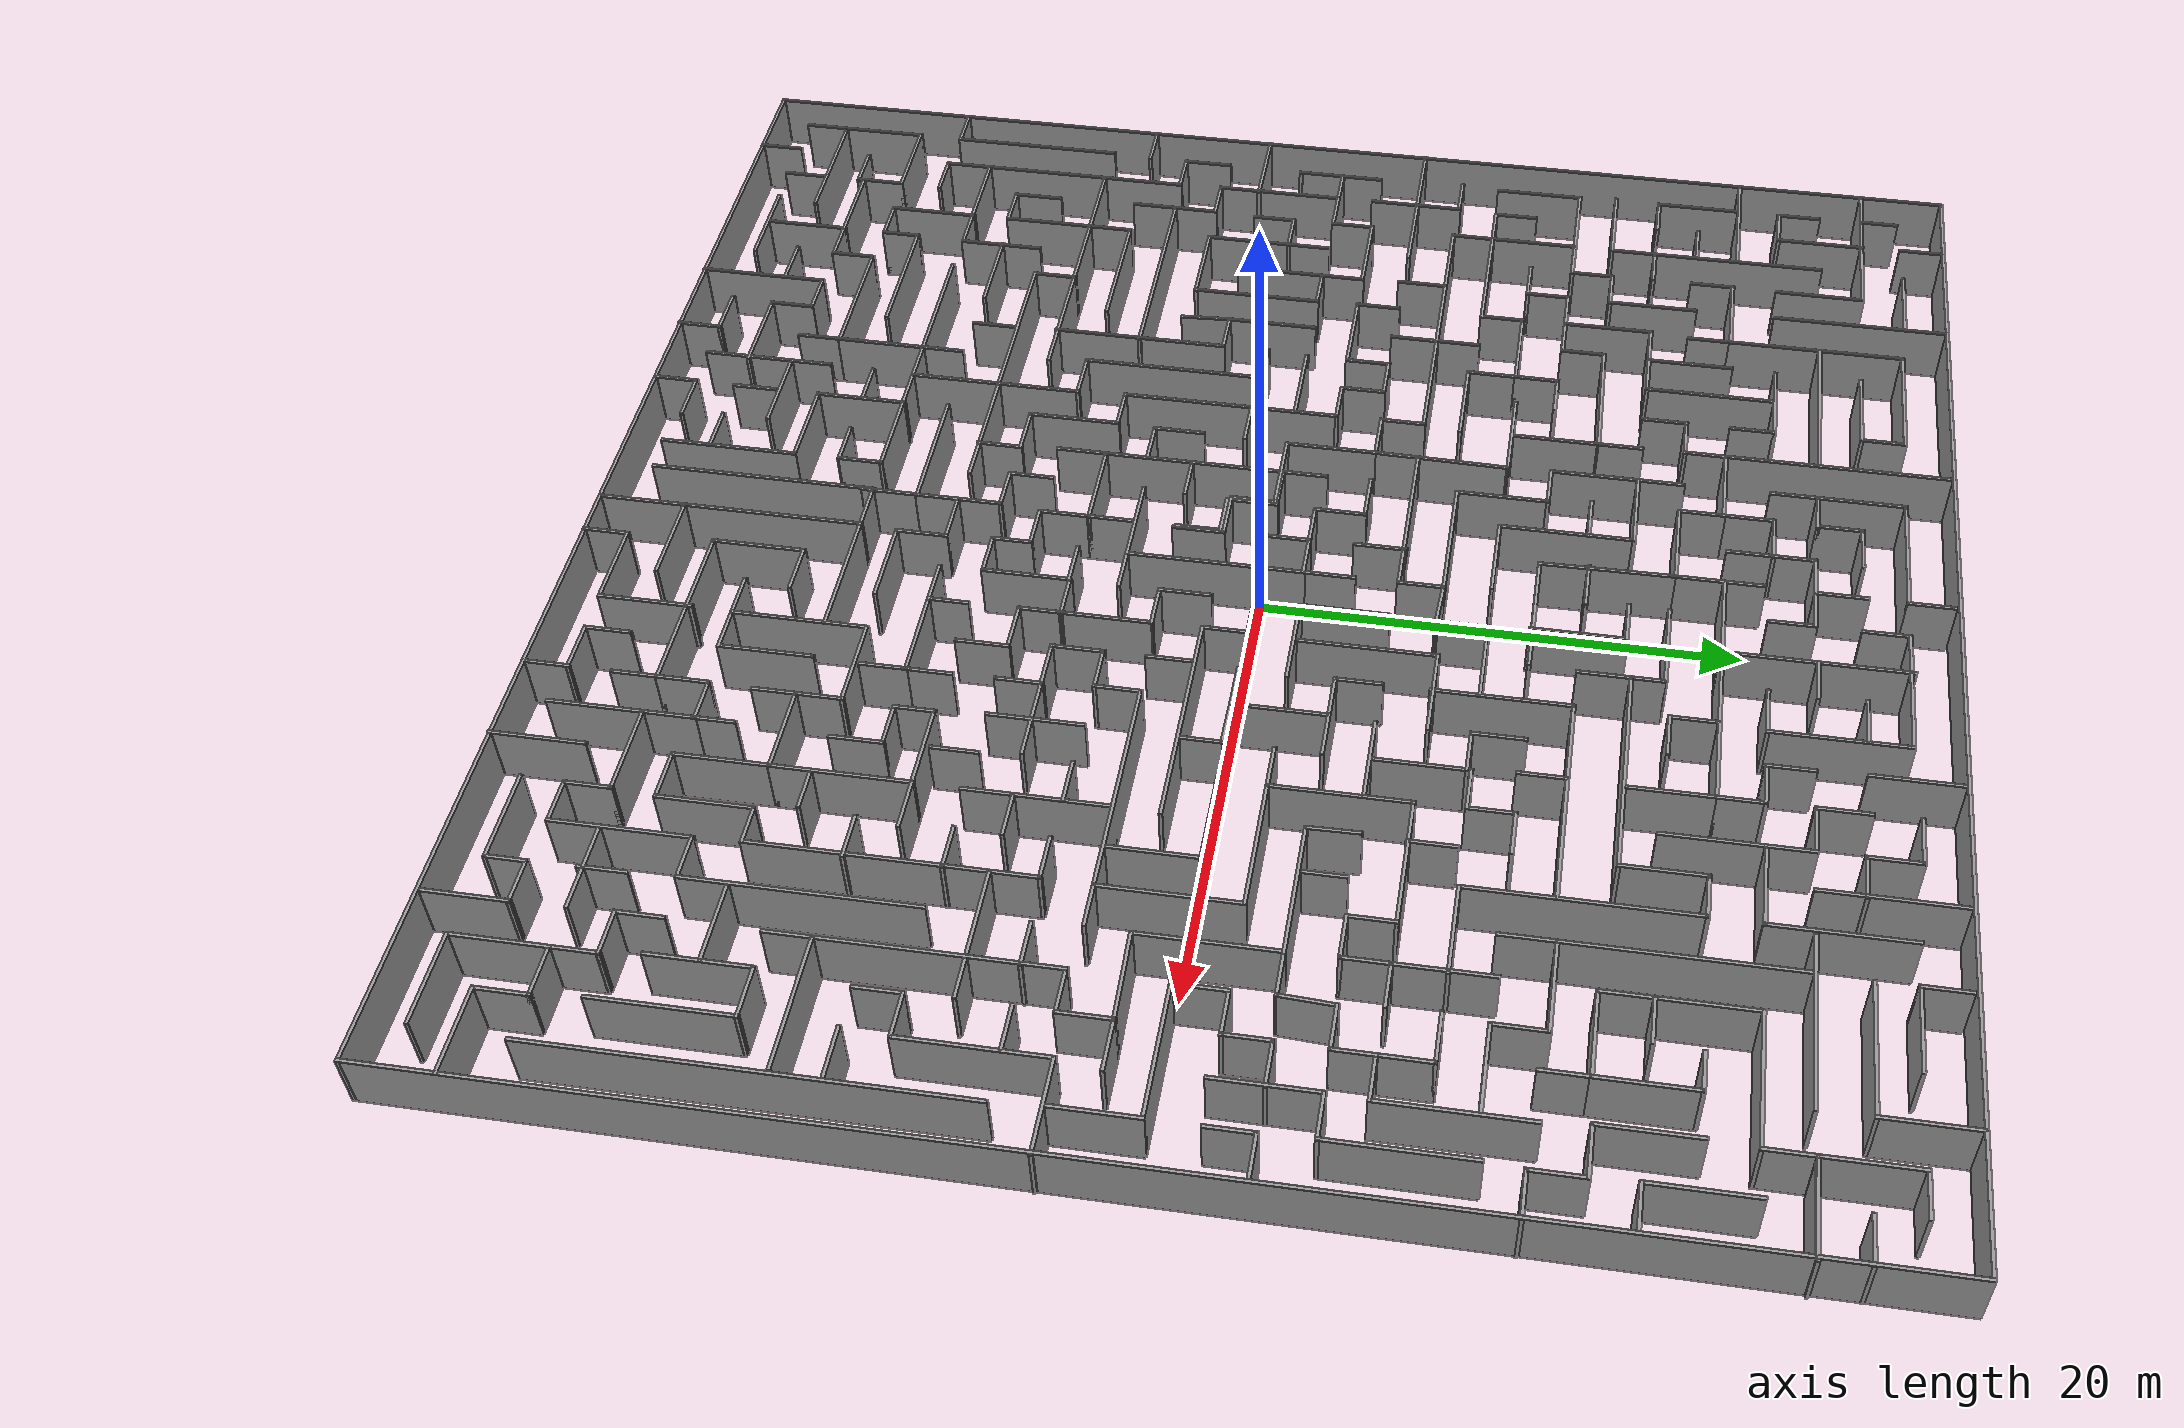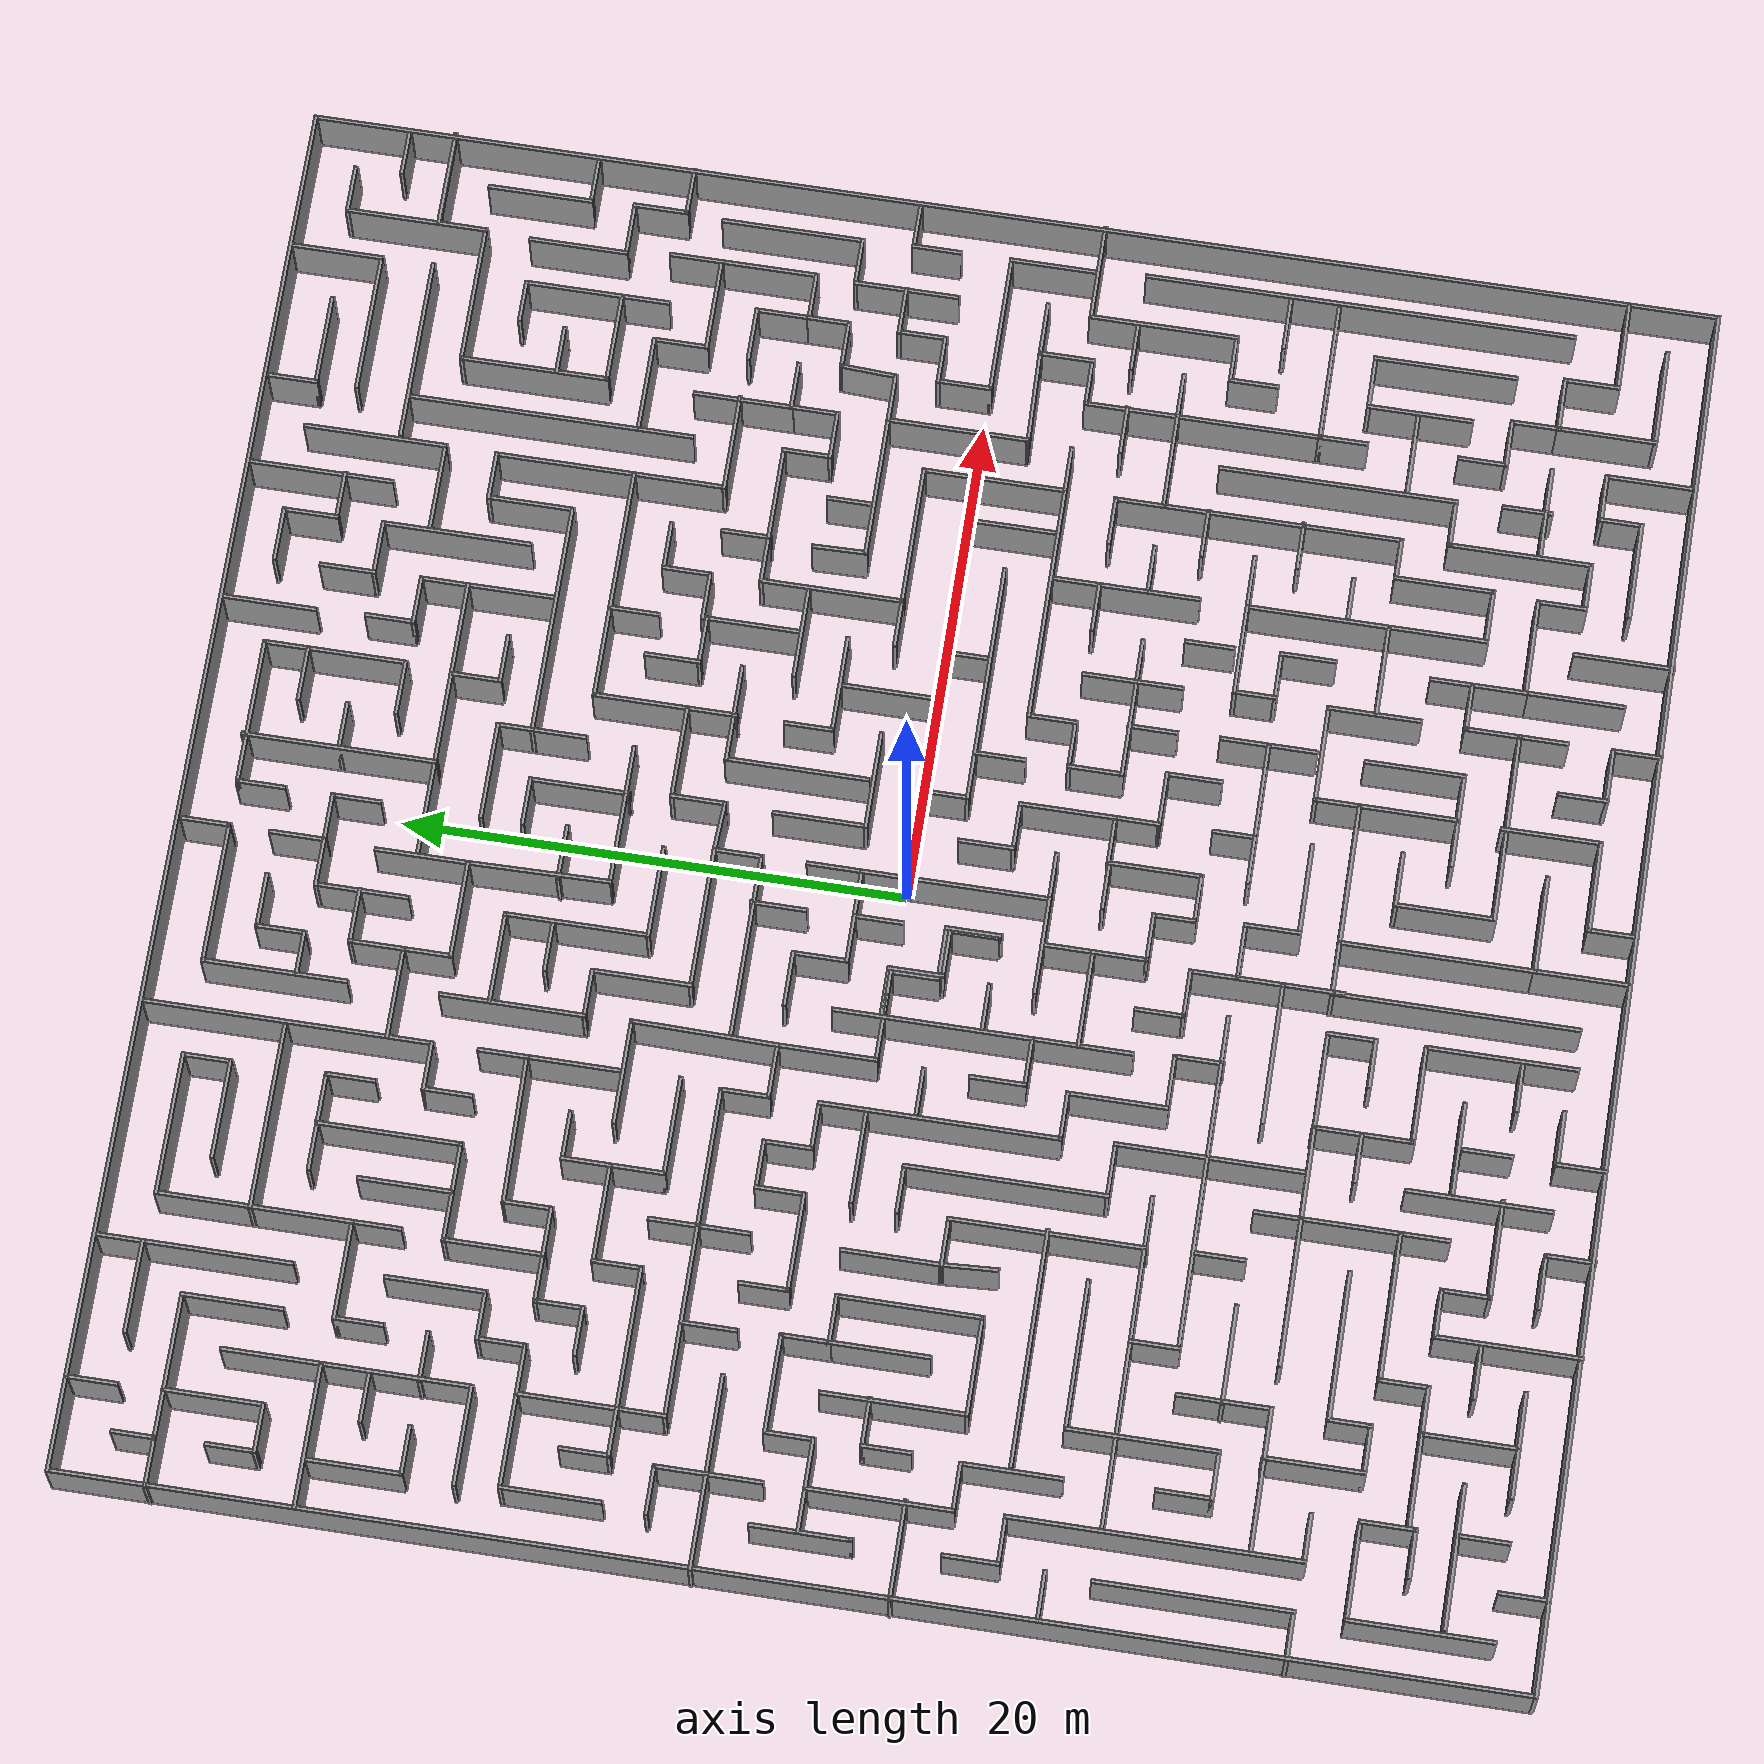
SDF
<?xml version='1.0'?>
<sdf version='1.7'>
  <model name='maze4'>
    <pose>-0.019787 0.082438 0 0 -0 0</pose>
    <link name='Wall_0'>
      <collision name='Wall_0_Collision'>
        <geometry>
          <box>
            <size>56.75 0.15 2.5</size>
          </box>
        </geometry>
        <pose>0 0 1.25 0 -0 0</pose>
      </collision>
      <visual name='Wall_0_Visual'>
        <pose>0 0 1.25 0 -0 0</pose>
        <geometry>
          <box>
            <size>56.75 0.15 2.5</size>
          </box>
        </geometry>
        <material>
          <script>
            <uri>file://media/materials/scripts/gazebo.material</uri>
            <name>Gazebo/Grey</name>
          </script>
          <ambient>1 1 1 1</ambient>
        </material>
        <meta>
          <layer>0</layer>
        </meta>
      </visual>
      <pose>-0.021699 28.3197 0 0 -0 0</pose>
    </link>
    <link name='Wall_1'>
      <collision name='Wall_1_Collision'>
        <geometry>
          <box>
            <size>56.75 0.15 2.5</size>
          </box>
        </geometry>
        <pose>0 0 1.25 0 -0 0</pose>
      </collision>
      <visual name='Wall_1_Visual'>
        <pose>0 0 1.25 0 -0 0</pose>
        <geometry>
          <box>
            <size>56.75 0.15 2.5</size>
          </box>
        </geometry>
        <material>
          <script>
            <uri>file://media/materials/scripts/gazebo.material</uri>
            <name>Gazebo/Grey</name>
          </script>
          <ambient>1 1 1 1</ambient>
        </material>
        <meta>
          <layer>0</layer>
        </meta>
      </visual>
      <pose>28.2783 0.019671 0 0 -0 -1.5708</pose>
    </link>
    <link name='Wall_100'>
      <collision name='Wall_100_Collision'>
        <geometry>
          <box>
            <size>5.75 0.15 2.5</size>
          </box>
        </geometry>
        <pose>0 0 1.25 0 -0 0</pose>
      </collision>
      <visual name='Wall_100_Visual'>
        <pose>0 0 1.25 0 -0 0</pose>
        <geometry>
          <box>
            <size>5.75 0.15 2.5</size>
          </box>
        </geometry>
        <material>
          <script>
            <uri>file://media/materials/scripts/gazebo.material</uri>
            <name>Gazebo/Grey</name>
          </script>
          <ambient>1 1 1 1</ambient>
        </material>
        <meta>
          <layer>0</layer>
        </meta>
      </visual>
      <pose>-20.839 -2.82935 0 0 -0 1.5708</pose>
    </link>
    <link name='Wall_102'>
      <collision name='Wall_102_Collision'>
        <geometry>
          <box>
            <size>4 0.15 2.5</size>
          </box>
        </geometry>
        <pose>0 0 1.25 0 -0 0</pose>
      </collision>
      <visual name='Wall_102_Visual'>
        <pose>0 0 1.25 0 -0 0</pose>
        <geometry>
          <box>
            <size>4 0.15 2.5</size>
          </box>
        </geometry>
        <material>
          <script>
            <uri>file://media/materials/scripts/gazebo.material</uri>
            <name>Gazebo/Grey</name>
          </script>
          <ambient>1 1 1 1</ambient>
        </material>
        <meta>
          <layer>0</layer>
        </meta>
      </visual>
      <pose>-18.839 -1.95435 0 0 -0 -1.5708</pose>
    </link>
    <link name='Wall_104'>
      <collision name='Wall_104_Collision'>
        <geometry>
          <box>
            <size>2 0.15 2.5</size>
          </box>
        </geometry>
        <pose>0 0 1.25 0 -0 0</pose>
      </collision>
      <visual name='Wall_104_Visual'>
        <pose>0 0 1.25 0 -0 0</pose>
        <geometry>
          <box>
            <size>2 0.15 2.5</size>
          </box>
        </geometry>
        <material>
          <script>
            <uri>file://media/materials/scripts/gazebo.material</uri>
            <name>Gazebo/Grey</name>
          </script>
          <ambient>1 1 1 1</ambient>
        </material>
        <meta>
          <layer>0</layer>
        </meta>
      </visual>
      <pose>-21.7242 -1.89031 0 0 -0 3.14159</pose>
    </link>
    <link name='Wall_105'>
      <collision name='Wall_105_Collision'>
        <geometry>
          <box>
            <size>2 0.15 2.5</size>
          </box>
        </geometry>
        <pose>0 0 1.25 0 -0 0</pose>
      </collision>
      <visual name='Wall_105_Visual'>
        <pose>0 0 1.25 0 -0 0</pose>
        <geometry>
          <box>
            <size>2 0.15 2.5</size>
          </box>
        </geometry>
        <material>
          <script>
            <uri>file://media/materials/scripts/gazebo.material</uri>
            <name>Gazebo/Grey</name>
          </script>
          <ambient>1 1 1 1</ambient>
        </material>
        <meta>
          <layer>0</layer>
        </meta>
      </visual>
      <pose>-22.6492 -2.81531 0 0 -0 -1.5708</pose>
    </link>
    <link name='Wall_107'>
      <collision name='Wall_107_Collision'>
        <geometry>
          <box>
            <size>5.75 0.15 2.5</size>
          </box>
        </geometry>
        <pose>0 0 1.25 0 -0 0</pose>
      </collision>
      <visual name='Wall_107_Visual'>
        <pose>0 0 1.25 0 -0 0</pose>
        <geometry>
          <box>
            <size>5.75 0.15 2.5</size>
          </box>
        </geometry>
        <material>
          <script>
            <uri>file://media/materials/scripts/gazebo.material</uri>
            <name>Gazebo/Grey</name>
          </script>
          <ambient>1 1 1 1</ambient>
        </material>
        <meta>
          <layer>0</layer>
        </meta>
      </visual>
      <pose>-24.6141 -2.87587 0 0 -0 -1.5708</pose>
    </link>
    <link name='Wall_108'>
      <collision name='Wall_108_Collision'>
        <geometry>
          <box>
            <size>2 0.15 2.5</size>
          </box>
        </geometry>
        <pose>0 0 1.25 0 -0 0</pose>
      </collision>
      <visual name='Wall_108_Visual'>
        <pose>0 0 1.25 0 -0 0</pose>
        <geometry>
          <box>
            <size>2 0.15 2.5</size>
          </box>
        </geometry>
        <material>
          <script>
            <uri>file://media/materials/scripts/gazebo.material</uri>
            <name>Gazebo/Grey</name>
          </script>
          <ambient>1 1 1 1</ambient>
        </material>
        <meta>
          <layer>0</layer>
        </meta>
      </visual>
      <pose>-23.6891 -5.67587 0 0 -0 0</pose>
    </link>
    <link name='Wall_109'>
      <collision name='Wall_109_Collision'>
        <geometry>
          <box>
            <size>4 0.15 2.5</size>
          </box>
        </geometry>
        <pose>0 0 1.25 0 -0 0</pose>
      </collision>
      <visual name='Wall_109_Visual'>
        <pose>0 0 1.25 0 -0 0</pose>
        <geometry>
          <box>
            <size>4 0.15 2.5</size>
          </box>
        </geometry>
        <material>
          <script>
            <uri>file://media/materials/scripts/gazebo.material</uri>
            <name>Gazebo/Grey</name>
          </script>
          <ambient>1 1 1 1</ambient>
        </material>
        <meta>
          <layer>0</layer>
        </meta>
      </visual>
      <pose>-22.7641 -7.60087 0 0 -0 -1.5708</pose>
    </link>
    <link name='Wall_111'>
      <collision name='Wall_111_Collision'>
        <geometry>
          <box>
            <size>4 0.15 2.5</size>
          </box>
        </geometry>
        <pose>0 0 1.25 0 -0 0</pose>
      </collision>
      <visual name='Wall_111_Visual'>
        <pose>0 0 1.25 0 -0 0</pose>
        <geometry>
          <box>
            <size>4 0.15 2.5</size>
          </box>
        </geometry>
        <material>
          <script>
            <uri>file://media/materials/scripts/gazebo.material</uri>
            <name>Gazebo/Grey</name>
          </script>
          <ambient>1 1 1 1</ambient>
        </material>
        <meta>
          <layer>0</layer>
        </meta>
      </visual>
      <pose>-26.4576 -3.84431 0 0 -0 0</pose>
    </link>
    <link name='Wall_113'>
      <collision name='Wall_113_Collision'>
        <geometry>
          <box>
            <size>2.25 0.15 2.5</size>
          </box>
        </geometry>
        <pose>0 0 1.25 0 -0 0</pose>
      </collision>
      <visual name='Wall_113_Visual'>
        <pose>0 0 1.25 0 -0 0</pose>
        <geometry>
          <box>
            <size>2.25 0.15 2.5</size>
          </box>
        </geometry>
        <material>
          <script>
            <uri>file://media/materials/scripts/gazebo.material</uri>
            <name>Gazebo/Grey</name>
          </script>
          <ambient>1 1 1 1</ambient>
        </material>
        <meta>
          <layer>0</layer>
        </meta>
      </visual>
      <pose>-26.382 -6.61569 0 0 -0 -1.5708</pose>
    </link>
    <link name='Wall_114'>
      <collision name='Wall_114_Collision'>
        <geometry>
          <box>
            <size>2 0.15 2.5</size>
          </box>
        </geometry>
        <pose>0 0 1.25 0 -0 0</pose>
      </collision>
      <visual name='Wall_114_Visual'>
        <pose>0 0 1.25 0 -0 0</pose>
        <geometry>
          <box>
            <size>2 0.15 2.5</size>
          </box>
        </geometry>
        <material>
          <script>
            <uri>file://media/materials/scripts/gazebo.material</uri>
            <name>Gazebo/Grey</name>
          </script>
          <ambient>1 1 1 1</ambient>
        </material>
        <meta>
          <layer>0</layer>
        </meta>
      </visual>
      <pose>-25.457 -7.6657 0 0 -0 0</pose>
    </link>
    <link name='Wall_115'>
      <collision name='Wall_115_Collision'>
        <geometry>
          <box>
            <size>11.5 0.15 2.5</size>
          </box>
        </geometry>
        <pose>0 0 1.25 0 -0 0</pose>
      </collision>
      <visual name='Wall_115_Visual'>
        <pose>0 0 1.25 0 -0 0</pose>
        <geometry>
          <box>
            <size>11.5 0.15 2.5</size>
          </box>
        </geometry>
        <material>
          <script>
            <uri>file://media/materials/scripts/gazebo.material</uri>
            <name>Gazebo/Grey</name>
          </script>
          <ambient>1 1 1 1</ambient>
        </material>
        <meta>
          <layer>0</layer>
        </meta>
      </visual>
      <pose>-24.532 -13.3407 0 0 -0 -1.5708</pose>
    </link>
    <link name='Wall_116'>
      <collision name='Wall_116_Collision'>
        <geometry>
          <box>
            <size>2 0.15 2.5</size>
          </box>
        </geometry>
        <pose>0 0 1.25 0 -0 0</pose>
      </collision>
      <visual name='Wall_116_Visual'>
        <pose>0 0 1.25 0 -0 0</pose>
        <geometry>
          <box>
            <size>2 0.15 2.5</size>
          </box>
        </geometry>
        <material>
          <script>
            <uri>file://media/materials/scripts/gazebo.material</uri>
            <name>Gazebo/Grey</name>
          </script>
          <ambient>1 1 1 1</ambient>
        </material>
        <meta>
          <layer>0</layer>
        </meta>
      </visual>
      <pose>-23.607 -19.0157 0 0 -0 0</pose>
    </link>
    <link name='Wall_118'>
      <collision name='Wall_118_Collision'>
        <geometry>
          <box>
            <size>2 0.15 2.5</size>
          </box>
        </geometry>
        <pose>0 0 1.25 0 -0 0</pose>
      </collision>
      <visual name='Wall_118_Visual'>
        <pose>0 0 1.25 0 -0 0</pose>
        <geometry>
          <box>
            <size>2 0.15 2.5</size>
          </box>
        </geometry>
        <material>
          <script>
            <uri>file://media/materials/scripts/gazebo.material</uri>
            <name>Gazebo/Grey</name>
          </script>
          <ambient>1 1 1 1</ambient>
        </material>
        <meta>
          <layer>0</layer>
        </meta>
      </visual>
      <pose>-27.3386 -9.43933 0 0 -0 0</pose>
    </link>
    <link name='Wall_12'>
      <collision name='Wall_12_Collision'>
        <geometry>
          <box>
            <size>4 0.15 2.5</size>
          </box>
        </geometry>
        <pose>0 0 1.25 0 -0 0</pose>
      </collision>
      <visual name='Wall_12_Visual'>
        <pose>0 0 1.25 0 -0 0</pose>
        <geometry>
          <box>
            <size>4 0.15 2.5</size>
          </box>
        </geometry>
        <material>
          <script>
            <uri>file://media/materials/scripts/gazebo.material</uri>
            <name>Gazebo/Grey</name>
          </script>
          <ambient>1 1 1 1</ambient>
        </material>
        <meta>
          <layer>0</layer>
        </meta>
      </visual>
      <pose>-24.5528 22.6582 0 0 -0 -1.5708</pose>
    </link>
    <link name='Wall_120'>
      <collision name='Wall_120_Collision'>
        <geometry>
          <box>
            <size>2 0.15 2.5</size>
          </box>
        </geometry>
        <pose>0 0 1.25 0 -0 0</pose>
      </collision>
      <visual name='Wall_120_Visual'>
        <pose>0 0 1.25 0 -0 0</pose>
        <geometry>
          <box>
            <size>2 0.15 2.5</size>
          </box>
        </geometry>
        <material>
          <script>
            <uri>file://media/materials/scripts/gazebo.material</uri>
            <name>Gazebo/Grey</name>
          </script>
          <ambient>1 1 1 1</ambient>
        </material>
        <meta>
          <layer>0</layer>
        </meta>
      </visual>
      <pose>-27.42 -18.8783 0 0 -0 0</pose>
    </link>
    <link name='Wall_121'>
      <collision name='Wall_121_Collision'>
        <geometry>
          <box>
            <size>7.75 0.15 2.5</size>
          </box>
        </geometry>
        <pose>0 0 1.25 0 -0 0</pose>
      </collision>
      <visual name='Wall_121_Visual'>
        <pose>0 0 1.25 0 -0 0</pose>
        <geometry>
          <box>
            <size>7.75 0.15 2.5</size>
          </box>
        </geometry>
        <material>
          <script>
            <uri>file://media/materials/scripts/gazebo.material</uri>
            <name>Gazebo/Grey</name>
          </script>
          <ambient>1 1 1 1</ambient>
        </material>
        <meta>
          <layer>0</layer>
        </meta>
      </visual>
      <pose>-26.495 -15.0783 0 0 -0 1.5708</pose>
    </link>
    <link name='Wall_123'>
      <collision name='Wall_123_Collision'>
        <geometry>
          <box>
            <size>2 0.15 2.5</size>
          </box>
        </geometry>
        <pose>0 0 1.25 0 -0 0</pose>
      </collision>
      <visual name='Wall_123_Visual'>
        <pose>0 0 1.25 0 -0 0</pose>
        <geometry>
          <box>
            <size>2 0.15 2.5</size>
          </box>
        </geometry>
        <material>
          <script>
            <uri>file://media/materials/scripts/gazebo.material</uri>
            <name>Gazebo/Grey</name>
          </script>
          <ambient>1 1 1 1</ambient>
        </material>
        <meta>
          <layer>0</layer>
        </meta>
      </visual>
      <pose>-24.6019 -27.3516 0 0 -0 1.5708</pose>
    </link>
    <link name='Wall_125'>
      <collision name='Wall_125_Collision'>
        <geometry>
          <box>
            <size>5.75 0.15 2.5</size>
          </box>
        </geometry>
        <pose>0 0 1.25 0 -0 0</pose>
      </collision>
      <visual name='Wall_125_Visual'>
        <pose>0 0 1.25 0 -0 0</pose>
        <geometry>
          <box>
            <size>5.75 0.15 2.5</size>
          </box>
        </geometry>
        <material>
          <script>
            <uri>file://media/materials/scripts/gazebo.material</uri>
            <name>Gazebo/Grey</name>
          </script>
          <ambient>1 1 1 1</ambient>
        </material>
        <meta>
          <layer>0</layer>
        </meta>
      </visual>
      <pose>-26.5141 -23.6865 0 0 -0 1.5708</pose>
    </link>
    <link name='Wall_126'>
      <collision name='Wall_126_Collision'>
        <geometry>
          <box>
            <size>4 0.15 2.5</size>
          </box>
        </geometry>
        <pose>0 0 1.25 0 -0 0</pose>
      </collision>
      <visual name='Wall_126_Visual'>
        <pose>0 0 1.25 0 -0 0</pose>
        <geometry>
          <box>
            <size>4 0.15 2.5</size>
          </box>
        </geometry>
        <material>
          <script>
            <uri>file://media/materials/scripts/gazebo.material</uri>
            <name>Gazebo/Grey</name>
          </script>
          <ambient>1 1 1 1</ambient>
        </material>
        <meta>
          <layer>0</layer>
        </meta>
      </visual>
      <pose>-24.5891 -20.8865 0 0 -0 0</pose>
    </link>
    <link name='Wall_127'>
      <collision name='Wall_127_Collision'>
        <geometry>
          <box>
            <size>2.25 0.15 2.5</size>
          </box>
        </geometry>
        <pose>0 0 1.25 0 -0 0</pose>
      </collision>
      <visual name='Wall_127_Visual'>
        <pose>0 0 1.25 0 -0 0</pose>
        <geometry>
          <box>
            <size>2.25 0.15 2.5</size>
          </box>
        </geometry>
        <material>
          <script>
            <uri>file://media/materials/scripts/gazebo.material</uri>
            <name>Gazebo/Grey</name>
          </script>
          <ambient>1 1 1 1</ambient>
        </material>
        <meta>
          <layer>0</layer>
        </meta>
      </visual>
      <pose>-22.6641 -21.9365 0 0 -0 -1.5708</pose>
    </link>
    <link name='Wall_128'>
      <collision name='Wall_128_Collision'>
        <geometry>
          <box>
            <size>2 0.15 2.5</size>
          </box>
        </geometry>
        <pose>0 0 1.25 0 -0 0</pose>
      </collision>
      <visual name='Wall_128_Visual'>
        <pose>0 0 1.25 0 -0 0</pose>
        <geometry>
          <box>
            <size>2 0.15 2.5</size>
          </box>
        </geometry>
        <material>
          <script>
            <uri>file://media/materials/scripts/gazebo.material</uri>
            <name>Gazebo/Grey</name>
          </script>
          <ambient>1 1 1 1</ambient>
        </material>
        <meta>
          <layer>0</layer>
        </meta>
      </visual>
      <pose>-23.5891 -22.9865 0 0 -0 3.14159</pose>
    </link>
    <link name='Wall_13'>
      <collision name='Wall_13_Collision'>
        <geometry>
          <box>
            <size>2 0.15 2.5</size>
          </box>
        </geometry>
        <pose>0 0 1.25 0 -0 0</pose>
      </collision>
      <visual name='Wall_13_Visual'>
        <pose>0 0 1.25 0 -0 0</pose>
        <geometry>
          <box>
            <size>2 0.15 2.5</size>
          </box>
        </geometry>
        <material>
          <script>
            <uri>file://media/materials/scripts/gazebo.material</uri>
            <name>Gazebo/Grey</name>
          </script>
          <ambient>1 1 1 1</ambient>
        </material>
        <meta>
          <layer>0</layer>
        </meta>
      </visual>
      <pose>-25.4778 20.7332 0 0 -0 3.14159</pose>
    </link>
    <link name='Wall_130'>
      <collision name='Wall_130_Collision'>
        <geometry>
          <box>
            <size>5.75 0.15 2.5</size>
          </box>
        </geometry>
        <pose>0 0 1.25 0 -0 0</pose>
      </collision>
      <visual name='Wall_130_Visual'>
        <pose>0 0 1.25 0 -0 0</pose>
        <geometry>
          <box>
            <size>5.75 0.15 2.5</size>
          </box>
        </geometry>
        <material>
          <script>
            <uri>file://media/materials/scripts/gazebo.material</uri>
            <name>Gazebo/Grey</name>
          </script>
          <ambient>1 1 1 1</ambient>
        </material>
        <meta>
          <layer>0</layer>
        </meta>
      </visual>
      <pose>-23.47 -24.5743 0 0 -0 0</pose>
    </link>
    <link name='Wall_132'>
      <collision name='Wall_132_Collision'>
        <geometry>
          <box>
            <size>2 0.15 2.5</size>
          </box>
        </geometry>
        <pose>0 0 1.25 0 -0 0</pose>
      </collision>
      <visual name='Wall_132_Visual'>
        <pose>0 0 1.25 0 -0 0</pose>
        <geometry>
          <box>
            <size>2 0.15 2.5</size>
          </box>
        </geometry>
        <material>
          <script>
            <uri>file://media/materials/scripts/gazebo.material</uri>
            <name>Gazebo/Grey</name>
          </script>
          <ambient>1 1 1 1</ambient>
        </material>
        <meta>
          <layer>0</layer>
        </meta>
      </visual>
      <pose>-22.649 -25.6022 0 0 -0 1.5708</pose>
    </link>
    <link name='Wall_134'>
      <collision name='Wall_134_Collision'>
        <geometry>
          <box>
            <size>4.25 0.15 2.5</size>
          </box>
        </geometry>
        <pose>0 0 1.25 0 -0 0</pose>
      </collision>
      <visual name='Wall_134_Visual'>
        <pose>0 0 1.25 0 -0 0</pose>
        <geometry>
          <box>
            <size>4.25 0.15 2.5</size>
          </box>
        </geometry>
        <material>
          <script>
            <uri>file://media/materials/scripts/gazebo.material</uri>
            <name>Gazebo/Grey</name>
          </script>
          <ambient>1 1 1 1</ambient>
        </material>
        <meta>
          <layer>0</layer>
        </meta>
      </visual>
      <pose>-18.8089 -26.4051 0 0 -0 0</pose>
    </link>
    <link name='Wall_136'>
      <collision name='Wall_136_Collision'>
        <geometry>
          <box>
            <size>3.75 0.15 2.5</size>
          </box>
        </geometry>
        <pose>0 0 1.25 0 -0 0</pose>
      </collision>
      <visual name='Wall_136_Visual'>
        <pose>0 0 1.25 0 -0 0</pose>
        <geometry>
          <box>
            <size>3.75 0.15 2.5</size>
          </box>
        </geometry>
        <material>
          <script>
            <uri>file://media/materials/scripts/gazebo.material</uri>
            <name>Gazebo/Grey</name>
          </script>
          <ambient>1 1 1 1</ambient>
        </material>
        <meta>
          <layer>0</layer>
        </meta>
      </visual>
      <pose>-18.9467 -24.5237 0 0 -0 1.5708</pose>
    </link>
    <link name='Wall_137'>
      <collision name='Wall_137_Collision'>
        <geometry>
          <box>
            <size>3.75 0.15 2.5</size>
          </box>
        </geometry>
        <pose>0 0 1.25 0 -0 0</pose>
      </collision>
      <visual name='Wall_137_Visual'>
        <pose>0 0 1.25 0 -0 0</pose>
        <geometry>
          <box>
            <size>3.75 0.15 2.5</size>
          </box>
        </geometry>
        <material>
          <script>
            <uri>file://media/materials/scripts/gazebo.material</uri>
            <name>Gazebo/Grey</name>
          </script>
          <ambient>1 1 1 1</ambient>
        </material>
        <meta>
          <layer>0</layer>
        </meta>
      </visual>
      <pose>-20.7467 -22.7237 0 0 -0 3.14159</pose>
    </link>
    <link name='Wall_139'>
      <collision name='Wall_139_Collision'>
        <geometry>
          <box>
            <size>2 0.15 2.5</size>
          </box>
        </geometry>
        <pose>0 0 1.25 0 -0 0</pose>
      </collision>
      <visual name='Wall_139_Visual'>
        <pose>0 0 1.25 0 -0 0</pose>
        <geometry>
          <box>
            <size>2 0.15 2.5</size>
          </box>
        </geometry>
        <material>
          <script>
            <uri>file://media/materials/scripts/gazebo.material</uri>
            <name>Gazebo/Grey</name>
          </script>
          <ambient>1 1 1 1</ambient>
        </material>
        <meta>
          <layer>0</layer>
        </meta>
      </visual>
      <pose>-18.0217 -22.7237 0 0 -0 0</pose>
    </link>
    <link name='Wall_14'>
      <collision name='Wall_14_Collision'>
        <geometry>
          <box>
            <size>2 0.15 2.5</size>
          </box>
        </geometry>
        <pose>0 0 1.25 0 -0 0</pose>
      </collision>
      <visual name='Wall_14_Visual'>
        <pose>0 0 1.25 0 -0 0</pose>
        <geometry>
          <box>
            <size>2 0.15 2.5</size>
          </box>
        </geometry>
        <material>
          <script>
            <uri>file://media/materials/scripts/gazebo.material</uri>
            <name>Gazebo/Grey</name>
          </script>
          <ambient>1 1 1 1</ambient>
        </material>
        <meta>
          <layer>0</layer>
        </meta>
      </visual>
      <pose>-26.4028 21.6582 0 0 -0 1.5708</pose>
    </link>
    <link name='Wall_140'>
      <collision name='Wall_140_Collision'>
        <geometry>
          <box>
            <size>2 0.15 2.5</size>
          </box>
        </geometry>
        <pose>0 0 1.25 0 -0 0</pose>
      </collision>
      <visual name='Wall_140_Visual'>
        <pose>0 0 1.25 0 -0 0</pose>
        <geometry>
          <box>
            <size>2 0.15 2.5</size>
          </box>
        </geometry>
        <material>
          <script>
            <uri>file://media/materials/scripts/gazebo.material</uri>
            <name>Gazebo/Grey</name>
          </script>
          <ambient>1 1 1 1</ambient>
        </material>
        <meta>
          <layer>0</layer>
        </meta>
      </visual>
      <pose>-17.0967 -21.7987 0 0 -0 1.5708</pose>
    </link>
    <link name='Wall_141'>
      <collision name='Wall_141_Collision'>
        <geometry>
          <box>
            <size>6 0.15 2.5</size>
          </box>
        </geometry>
        <pose>0 0 1.25 0 -0 0</pose>
      </collision>
      <visual name='Wall_141_Visual'>
        <pose>0 0 1.25 0 -0 0</pose>
        <geometry>
          <box>
            <size>6 0.15 2.5</size>
          </box>
        </geometry>
        <material>
          <script>
            <uri>file://media/materials/scripts/gazebo.material</uri>
            <name>Gazebo/Grey</name>
          </script>
          <ambient>1 1 1 1</ambient>
        </material>
        <meta>
          <layer>0</layer>
        </meta>
      </visual>
      <pose>-14.1717 -20.8737 0 0 -0 0</pose>
    </link>
    <link name='Wall_142'>
      <collision name='Wall_142_Collision'>
        <geometry>
          <box>
            <size>2 0.15 2.5</size>
          </box>
        </geometry>
        <pose>0 0 1.25 0 -0 0</pose>
      </collision>
      <visual name='Wall_142_Visual'>
        <pose>0 0 1.25 0 -0 0</pose>
        <geometry>
          <box>
            <size>2 0.15 2.5</size>
          </box>
        </geometry>
        <material>
          <script>
            <uri>file://media/materials/scripts/gazebo.material</uri>
            <name>Gazebo/Grey</name>
          </script>
          <ambient>1 1 1 1</ambient>
        </material>
        <meta>
          <layer>0</layer>
        </meta>
      </visual>
      <pose>-11.2467 -21.7987 0 0 -0 -1.5708</pose>
    </link>
    <link name='Wall_144'>
      <collision name='Wall_144_Collision'>
        <geometry>
          <box>
            <size>5.75 0.15 2.5</size>
          </box>
        </geometry>
        <pose>0 0 1.25 0 -0 0</pose>
      </collision>
      <visual name='Wall_144_Visual'>
        <pose>0 0 1.25 0 -0 0</pose>
        <geometry>
          <box>
            <size>5.75 0.15 2.5</size>
          </box>
        </geometry>
        <material>
          <script>
            <uri>file://media/materials/scripts/gazebo.material</uri>
            <name>Gazebo/Grey</name>
          </script>
          <ambient>1 1 1 1</ambient>
        </material>
        <meta>
          <layer>0</layer>
        </meta>
      </visual>
      <pose>-11.2467 -18.0737 0 0 -0 1.5708</pose>
    </link>
    <link name='Wall_146'>
      <collision name='Wall_146_Collision'>
        <geometry>
          <box>
            <size>13.5 0.15 2.5</size>
          </box>
        </geometry>
        <pose>0 0 1.25 0 -0 0</pose>
      </collision>
      <visual name='Wall_146_Visual'>
        <pose>0 0 1.25 0 -0 0</pose>
        <geometry>
          <box>
            <size>13.5 0.15 2.5</size>
          </box>
        </geometry>
        <material>
          <script>
            <uri>file://media/materials/scripts/gazebo.material</uri>
            <name>Gazebo/Grey</name>
          </script>
          <ambient>1 1 1 1</ambient>
        </material>
        <meta>
          <layer>0</layer>
        </meta>
      </visual>
      <pose>-10.4001 -17.0475 0 0 -0 0</pose>
    </link>
    <link name='Wall_147'>
      <collision name='Wall_147_Collision'>
        <geometry>
          <box>
            <size>2 0.15 2.5</size>
          </box>
        </geometry>
        <pose>0 0 1.25 0 -0 0</pose>
      </collision>
      <visual name='Wall_147_Visual'>
        <pose>0 0 1.25 0 -0 0</pose>
        <geometry>
          <box>
            <size>2 0.15 2.5</size>
          </box>
        </geometry>
        <material>
          <script>
            <uri>file://media/materials/scripts/gazebo.material</uri>
            <name>Gazebo/Grey</name>
          </script>
          <ambient>1 1 1 1</ambient>
        </material>
        <meta>
          <layer>0</layer>
        </meta>
      </visual>
      <pose>-3.72513 -17.9725 0 0 -0 -1.5708</pose>
    </link>
    <link name='Wall_148'>
      <collision name='Wall_148_Collision'>
        <geometry>
          <box>
            <size>2 0.15 2.5</size>
          </box>
        </geometry>
        <pose>0 0 1.25 0 -0 0</pose>
      </collision>
      <visual name='Wall_148_Visual'>
        <pose>0 0 1.25 0 -0 0</pose>
        <geometry>
          <box>
            <size>2 0.15 2.5</size>
          </box>
        </geometry>
        <material>
          <script>
            <uri>file://media/materials/scripts/gazebo.material</uri>
            <name>Gazebo/Grey</name>
          </script>
          <ambient>1 1 1 1</ambient>
        </material>
        <meta>
          <layer>0</layer>
        </meta>
      </visual>
      <pose>-4.65013 -18.8975 0 0 -0 3.14159</pose>
    </link>
    <link name='Wall_150'>
      <collision name='Wall_150_Collision'>
        <geometry>
          <box>
            <size>4 0.15 2.5</size>
          </box>
        </geometry>
        <pose>0 0 1.25 0 -0 0</pose>
      </collision>
      <visual name='Wall_150_Visual'>
        <pose>0 0 1.25 0 -0 0</pose>
        <geometry>
          <box>
            <size>4 0.15 2.5</size>
          </box>
        </geometry>
        <material>
          <script>
            <uri>file://media/materials/scripts/gazebo.material</uri>
            <name>Gazebo/Grey</name>
          </script>
          <ambient>1 1 1 1</ambient>
        </material>
        <meta>
          <layer>0</layer>
        </meta>
      </visual>
      <pose>-7.55477 -18.9318 0 0 -0 -1.5708</pose>
    </link>
    <link name='Wall_151'>
      <collision name='Wall_151_Collision'>
        <geometry>
          <box>
            <size>4 0.15 2.5</size>
          </box>
        </geometry>
        <pose>0 0 1.25 0 -0 0</pose>
      </collision>
      <visual name='Wall_151_Visual'>
        <pose>0 0 1.25 0 -0 0</pose>
        <geometry>
          <box>
            <size>4 0.15 2.5</size>
          </box>
        </geometry>
        <material>
          <script>
            <uri>file://media/materials/scripts/gazebo.material</uri>
            <name>Gazebo/Grey</name>
          </script>
          <ambient>1 1 1 1</ambient>
        </material>
        <meta>
          <layer>0</layer>
        </meta>
      </visual>
      <pose>-5.62977 -20.8568 0 0 -0 0</pose>
    </link>
    <link name='Wall_152'>
      <collision name='Wall_152_Collision'>
        <geometry>
          <box>
            <size>6 0.15 2.5</size>
          </box>
        </geometry>
        <pose>0 0 1.25 0 -0 0</pose>
      </collision>
      <visual name='Wall_152_Visual'>
        <pose>0 0 1.25 0 -0 0</pose>
        <geometry>
          <box>
            <size>6 0.15 2.5</size>
          </box>
        </geometry>
        <material>
          <script>
            <uri>file://media/materials/scripts/gazebo.material</uri>
            <name>Gazebo/Grey</name>
          </script>
          <ambient>1 1 1 1</ambient>
        </material>
        <meta>
          <layer>0</layer>
        </meta>
      </visual>
      <pose>-3.70477 -23.7818 0 0 -0 -1.5708</pose>
    </link>
    <link name='Wall_154'>
      <collision name='Wall_154_Collision'>
        <geometry>
          <box>
            <size>2 0.15 2.5</size>
          </box>
        </geometry>
        <pose>0 0 1.25 0 -0 0</pose>
      </collision>
      <visual name='Wall_154_Visual'>
        <pose>0 0 1.25 0 -0 0</pose>
        <geometry>
          <box>
            <size>2 0.15 2.5</size>
          </box>
        </geometry>
        <material>
          <script>
            <uri>file://media/materials/scripts/gazebo.material</uri>
            <name>Gazebo/Grey</name>
          </script>
          <ambient>1 1 1 1</ambient>
        </material>
        <meta>
          <layer>0</layer>
        </meta>
      </visual>
      <pose>-4.75825 -24.615 0 0 -0 0</pose>
    </link>
    <link name='Wall_156'>
      <collision name='Wall_156_Collision'>
        <geometry>
          <box>
            <size>5.75 0.15 2.5</size>
          </box>
        </geometry>
        <pose>0 0 1.25 0 -0 0</pose>
      </collision>
      <visual name='Wall_156_Visual'>
        <pose>0 0 1.25 0 -0 0</pose>
        <geometry>
          <box>
            <size>5.75 0.15 2.5</size>
          </box>
        </geometry>
        <material>
          <script>
            <uri>file://media/materials/scripts/gazebo.material</uri>
            <name>Gazebo/Grey</name>
          </script>
          <ambient>1 1 1 1</ambient>
        </material>
        <meta>
          <layer>0</layer>
        </meta>
      </visual>
      <pose>-9.50767 -23.6719 0 0 -0 -1.5708</pose>
    </link>
    <link name='Wall_158'>
      <collision name='Wall_158_Collision'>
        <geometry>
          <box>
            <size>3.75 0.15 2.5</size>
          </box>
        </geometry>
        <pose>0 0 1.25 0 -0 0</pose>
      </collision>
      <visual name='Wall_158_Visual'>
        <pose>0 0 1.25 0 -0 0</pose>
        <geometry>
          <box>
            <size>3.75 0.15 2.5</size>
          </box>
        </geometry>
        <material>
          <script>
            <uri>file://media/materials/scripts/gazebo.material</uri>
            <name>Gazebo/Grey</name>
          </script>
          <ambient>1 1 1 1</ambient>
        </material>
        <meta>
          <layer>0</layer>
        </meta>
      </visual>
      <pose>-7.54493 -22.6214 0 0 -0 0</pose>
    </link>
    <link name='Wall_16'>
      <collision name='Wall_16_Collision'>
        <geometry>
          <box>
            <size>7.75 0.15 2.5</size>
          </box>
        </geometry>
        <pose>0 0 1.25 0 -0 0</pose>
      </collision>
      <visual name='Wall_16_Visual'>
        <pose>0 0 1.25 0 -0 0</pose>
        <geometry>
          <box>
            <size>7.75 0.15 2.5</size>
          </box>
        </geometry>
        <material>
          <script>
            <uri>file://media/materials/scripts/gazebo.material</uri>
            <name>Gazebo/Grey</name>
          </script>
          <ambient>1 1 1 1</ambient>
        </material>
        <meta>
          <layer>0</layer>
        </meta>
      </visual>
      <pose>-18.9232 24.4586 0 0 -0 -1.5708</pose>
    </link>
    <link name='Wall_160'>
      <collision name='Wall_160_Collision'>
        <geometry>
          <box>
            <size>2 0.15 2.5</size>
          </box>
        </geometry>
        <pose>0 0 1.25 0 -0 0</pose>
      </collision>
      <visual name='Wall_160_Visual'>
        <pose>0 0 1.25 0 -0 0</pose>
        <geometry>
          <box>
            <size>2 0.15 2.5</size>
          </box>
        </geometry>
        <material>
          <script>
            <uri>file://media/materials/scripts/gazebo.material</uri>
            <name>Gazebo/Grey</name>
          </script>
          <ambient>1 1 1 1</ambient>
        </material>
        <meta>
          <layer>0</layer>
        </meta>
      </visual>
      <pose>-7.55477 -23.7306 0 0 -0 1.5708</pose>
    </link>
    <link name='Wall_162'>
      <collision name='Wall_162_Collision'>
        <geometry>
          <box>
            <size>2 0.15 2.5</size>
          </box>
        </geometry>
        <pose>0 0 1.25 0 -0 0</pose>
      </collision>
      <visual name='Wall_162_Visual'>
        <pose>0 0 1.25 0 -0 0</pose>
        <geometry>
          <box>
            <size>2 0.15 2.5</size>
          </box>
        </geometry>
        <material>
          <script>
            <uri>file://media/materials/scripts/gazebo.material</uri>
            <name>Gazebo/Grey</name>
          </script>
          <ambient>1 1 1 1</ambient>
        </material>
        <meta>
          <layer>0</layer>
        </meta>
      </visual>
      <pose>-7.59546 -27.3516 0 0 -0 1.5708</pose>
    </link>
    <link name='Wall_163'>
      <collision name='Wall_163_Collision'>
        <geometry>
          <box>
            <size>2.25 0.15 2.5</size>
          </box>
        </geometry>
        <pose>0 0 1.25 0 -0 0</pose>
      </collision>
      <visual name='Wall_163_Visual'>
        <pose>0 0 1.25 0 -0 0</pose>
        <geometry>
          <box>
            <size>2.25 0.15 2.5</size>
          </box>
        </geometry>
        <material>
          <script>
            <uri>file://media/materials/scripts/gazebo.material</uri>
            <name>Gazebo/Grey</name>
          </script>
          <ambient>1 1 1 1</ambient>
        </material>
        <meta>
          <layer>0</layer>
        </meta>
      </visual>
      <pose>-6.54546 -26.4266 0 0 -0 0</pose>
    </link>
    <link name='Wall_165'>
      <collision name='Wall_165_Collision'>
        <geometry>
          <box>
            <size>2 0.15 2.5</size>
          </box>
        </geometry>
        <pose>0 0 1.25 0 -0 0</pose>
      </collision>
      <visual name='Wall_165_Visual'>
        <pose>0 0 1.25 0 -0 0</pose>
        <geometry>
          <box>
            <size>2 0.15 2.5</size>
          </box>
        </geometry>
        <material>
          <script>
            <uri>file://media/materials/scripts/gazebo.material</uri>
            <name>Gazebo/Grey</name>
          </script>
          <ambient>1 1 1 1</ambient>
        </material>
        <meta>
          <layer>0</layer>
        </meta>
      </visual>
      <pose>-11.2571 -27.3923 0 0 -0 1.5708</pose>
    </link>
    <link name='Wall_166'>
      <collision name='Wall_166_Collision'>
        <geometry>
          <box>
            <size>2.25 0.15 2.5</size>
          </box>
        </geometry>
        <pose>0 0 1.25 0 -0 0</pose>
      </collision>
      <visual name='Wall_166_Visual'>
        <pose>0 0 1.25 0 -0 0</pose>
        <geometry>
          <box>
            <size>2.25 0.15 2.5</size>
          </box>
        </geometry>
        <material>
          <script>
            <uri>file://media/materials/scripts/gazebo.material</uri>
            <name>Gazebo/Grey</name>
          </script>
          <ambient>1 1 1 1</ambient>
        </material>
        <meta>
          <layer>0</layer>
        </meta>
      </visual>
      <pose>-12.3071 -26.4673 0 0 -0 3.14159</pose>
    </link>
    <link name='Wall_168'>
      <collision name='Wall_168_Collision'>
        <geometry>
          <box>
            <size>5.75 0.15 2.5</size>
          </box>
        </geometry>
        <pose>0 0 1.25 0 -0 0</pose>
      </collision>
      <visual name='Wall_168_Visual'>
        <pose>0 0 1.25 0 -0 0</pose>
        <geometry>
          <box>
            <size>5.75 0.15 2.5</size>
          </box>
        </geometry>
        <material>
          <script>
            <uri>file://media/materials/scripts/gazebo.material</uri>
            <name>Gazebo/Grey</name>
          </script>
          <ambient>1 1 1 1</ambient>
        </material>
        <meta>
          <layer>0</layer>
        </meta>
      </visual>
      <pose>-15.0816 -25.5173 0 0 -0 1.5708</pose>
    </link>
    <link name='Wall_169'>
      <collision name='Wall_169_Collision'>
        <geometry>
          <box>
            <size>2 0.15 2.5</size>
          </box>
        </geometry>
        <pose>0 0 1.25 0 -0 0</pose>
      </collision>
      <visual name='Wall_169_Visual'>
        <pose>0 0 1.25 0 -0 0</pose>
        <geometry>
          <box>
            <size>2 0.15 2.5</size>
          </box>
        </geometry>
        <material>
          <script>
            <uri>file://media/materials/scripts/gazebo.material</uri>
            <name>Gazebo/Grey</name>
          </script>
          <ambient>1 1 1 1</ambient>
        </material>
        <meta>
          <layer>0</layer>
        </meta>
      </visual>
      <pose>-14.1566 -22.7173 0 0 -0 0</pose>
    </link>
    <link name='Wall_170'>
      <collision name='Wall_170_Collision'>
        <geometry>
          <box>
            <size>2 0.15 2.5</size>
          </box>
        </geometry>
        <pose>0 0 1.25 0 -0 0</pose>
      </collision>
      <visual name='Wall_170_Visual'>
        <pose>0 0 1.25 0 -0 0</pose>
        <geometry>
          <box>
            <size>2 0.15 2.5</size>
          </box>
        </geometry>
        <material>
          <script>
            <uri>file://media/materials/scripts/gazebo.material</uri>
            <name>Gazebo/Grey</name>
          </script>
          <ambient>1 1 1 1</ambient>
        </material>
        <meta>
          <layer>0</layer>
        </meta>
      </visual>
      <pose>-13.2316 -23.6423 0 0 -0 -1.5708</pose>
    </link>
    <link name='Wall_171'>
      <collision name='Wall_171_Collision'>
        <geometry>
          <box>
            <size>4 0.15 2.5</size>
          </box>
        </geometry>
        <pose>0 0 1.25 0 -0 0</pose>
      </collision>
      <visual name='Wall_171_Visual'>
        <pose>0 0 1.25 0 -0 0</pose>
        <geometry>
          <box>
            <size>4 0.15 2.5</size>
          </box>
        </geometry>
        <material>
          <script>
            <uri>file://media/materials/scripts/gazebo.material</uri>
            <name>Gazebo/Grey</name>
          </script>
          <ambient>1 1 1 1</ambient>
        </material>
        <meta>
          <layer>0</layer>
        </meta>
      </visual>
      <pose>-11.3066 -24.5673 0 0 -0 0</pose>
    </link>
    <link name='Wall_173'>
      <collision name='Wall_173_Collision'>
        <geometry>
          <box>
            <size>2.25 0.15 2.5</size>
          </box>
        </geometry>
        <pose>0 0 1.25 0 -0 0</pose>
      </collision>
      <visual name='Wall_173_Visual'>
        <pose>0 0 1.25 0 -0 0</pose>
        <geometry>
          <box>
            <size>2.25 0.15 2.5</size>
          </box>
        </geometry>
        <material>
          <script>
            <uri>file://media/materials/scripts/gazebo.material</uri>
            <name>Gazebo/Grey</name>
          </script>
          <ambient>1 1 1 1</ambient>
        </material>
        <meta>
          <layer>0</layer>
        </meta>
      </visual>
      <pose>-16.1722 -24.4929 0 0 -0 3.14159</pose>
    </link>
    <link name='Wall_175'>
      <collision name='Wall_175_Collision'>
        <geometry>
          <box>
            <size>2 0.15 2.5</size>
          </box>
        </geometry>
        <pose>0 0 1.25 0 -0 0</pose>
      </collision>
      <visual name='Wall_175_Visual'>
        <pose>0 0 1.25 0 -0 0</pose>
        <geometry>
          <box>
            <size>2 0.15 2.5</size>
          </box>
        </geometry>
        <material>
          <script>
            <uri>file://media/materials/scripts/gazebo.material</uri>
            <name>Gazebo/Grey</name>
          </script>
          <ambient>1 1 1 1</ambient>
        </material>
        <meta>
          <layer>0</layer>
        </meta>
      </visual>
      <pose>-8.52046 -18.8783 0 0 -0 3.14159</pose>
    </link>
    <link name='Wall_177'>
      <collision name='Wall_177_Collision'>
        <geometry>
          <box>
            <size>4 0.15 2.5</size>
          </box>
        </geometry>
        <pose>0 0 1.25 0 -0 0</pose>
      </collision>
      <visual name='Wall_177_Visual'>
        <pose>0 0 1.25 0 -0 0</pose>
        <geometry>
          <box>
            <size>4 0.15 2.5</size>
          </box>
        </geometry>
        <material>
          <script>
            <uri>file://media/materials/scripts/gazebo.material</uri>
            <name>Gazebo/Grey</name>
          </script>
          <ambient>1 1 1 1</ambient>
        </material>
        <meta>
          <layer>0</layer>
        </meta>
      </visual>
      <pose>-20.7775 -18.8504 0 0 -0 -1.5708</pose>
    </link>
    <link name='Wall_178'>
      <collision name='Wall_178_Collision'>
        <geometry>
          <box>
            <size>2 0.15 2.5</size>
          </box>
        </geometry>
        <pose>0 0 1.25 0 -0 0</pose>
      </collision>
      <visual name='Wall_178_Visual'>
        <pose>0 0 1.25 0 -0 0</pose>
        <geometry>
          <box>
            <size>2 0.15 2.5</size>
          </box>
        </geometry>
        <material>
          <script>
            <uri>file://media/materials/scripts/gazebo.material</uri>
            <name>Gazebo/Grey</name>
          </script>
          <ambient>1 1 1 1</ambient>
        </material>
        <meta>
          <layer>0</layer>
        </meta>
      </visual>
      <pose>-19.8525 -20.7754 0 0 -0 0</pose>
    </link>
    <link name='Wall_179'>
      <collision name='Wall_179_Collision'>
        <geometry>
          <box>
            <size>1.75 0.15 2.5</size>
          </box>
        </geometry>
        <pose>0 0 1.25 0 -0 0</pose>
      </collision>
      <visual name='Wall_179_Visual'>
        <pose>0 0 1.25 0 -0 0</pose>
        <geometry>
          <box>
            <size>1.75 0.15 2.5</size>
          </box>
        </geometry>
        <material>
          <script>
            <uri>file://media/materials/scripts/gazebo.material</uri>
            <name>Gazebo/Grey</name>
          </script>
          <ambient>1 1 1 1</ambient>
        </material>
        <meta>
          <layer>0</layer>
        </meta>
      </visual>
      <pose>-18.9275 -19.9754 0 0 -0 1.5708</pose>
    </link>
    <link name='Wall_180'>
      <collision name='Wall_180_Collision'>
        <geometry>
          <box>
            <size>6 0.15 2.5</size>
          </box>
        </geometry>
        <pose>0 0 1.25 0 -0 0</pose>
      </collision>
      <visual name='Wall_180_Visual'>
        <pose>0 0 1.25 0 -0 0</pose>
        <geometry>
          <box>
            <size>6 0.15 2.5</size>
          </box>
        </geometry>
        <material>
          <script>
            <uri>file://media/materials/scripts/gazebo.material</uri>
            <name>Gazebo/Grey</name>
          </script>
          <ambient>1 1 1 1</ambient>
        </material>
        <meta>
          <layer>0</layer>
        </meta>
      </visual>
      <pose>-16.0025 -19.1754 0 0 -0 0</pose>
    </link>
    <link name='Wall_182'>
      <collision name='Wall_182_Collision'>
        <geometry>
          <box>
            <size>5.75 0.15 2.5</size>
          </box>
        </geometry>
        <pose>0 0 1.25 0 -0 0</pose>
      </collision>
      <visual name='Wall_182_Visual'>
        <pose>0 0 1.25 0 -0 0</pose>
        <geometry>
          <box>
            <size>5.75 0.15 2.5</size>
          </box>
        </geometry>
        <material>
          <script>
            <uri>file://media/materials/scripts/gazebo.material</uri>
            <name>Gazebo/Grey</name>
          </script>
          <ambient>1 1 1 1</ambient>
        </material>
        <meta>
          <layer>0</layer>
        </meta>
      </visual>
      <pose>-21.6392 -16.9661 0 0 -0 0</pose>
    </link>
    <link name='Wall_183'>
      <collision name='Wall_183_Collision'>
        <geometry>
          <box>
            <size>3.75 0.15 2.5</size>
          </box>
        </geometry>
        <pose>0 0 1.25 0 -0 0</pose>
      </collision>
      <visual name='Wall_183_Visual'>
        <pose>0 0 1.25 0 -0 0</pose>
        <geometry>
          <box>
            <size>3.75 0.15 2.5</size>
          </box>
        </geometry>
        <material>
          <script>
            <uri>file://media/materials/scripts/gazebo.material</uri>
            <name>Gazebo/Grey</name>
          </script>
          <ambient>1 1 1 1</ambient>
        </material>
        <meta>
          <layer>0</layer>
        </meta>
      </visual>
      <pose>-18.8392 -15.1661 0 0 -0 1.5708</pose>
    </link>
    <link name='Wall_185'>
      <collision name='Wall_185_Collision'>
        <geometry>
          <box>
            <size>4 0.15 2.5</size>
          </box>
        </geometry>
        <pose>0 0 1.25 0 -0 0</pose>
      </collision>
      <visual name='Wall_185_Visual'>
        <pose>0 0 1.25 0 -0 0</pose>
        <geometry>
          <box>
            <size>4 0.15 2.5</size>
          </box>
        </geometry>
        <material>
          <script>
            <uri>file://media/materials/scripts/gazebo.material</uri>
            <name>Gazebo/Grey</name>
          </script>
          <ambient>1 1 1 1</ambient>
        </material>
        <meta>
          <layer>0</layer>
        </meta>
      </visual>
      <pose>-16.981 -15.0946 0 0 -0 0</pose>
    </link>
    <link name='Wall_187'>
      <collision name='Wall_187_Collision'>
        <geometry>
          <box>
            <size>2.25 0.15 2.5</size>
          </box>
        </geometry>
        <pose>0 0 1.25 0 -0 0</pose>
      </collision>
      <visual name='Wall_187_Visual'>
        <pose>0 0 1.25 0 -0 0</pose>
        <geometry>
          <box>
            <size>2.25 0.15 2.5</size>
          </box>
        </geometry>
        <material>
          <script>
            <uri>file://media/materials/scripts/gazebo.material</uri>
            <name>Gazebo/Grey</name>
          </script>
          <ambient>1 1 1 1</ambient>
        </material>
        <meta>
          <layer>0</layer>
        </meta>
      </visual>
      <pose>-22.649 -14.1917 0 0 -0 -1.5708</pose>
    </link>
    <link name='Wall_188'>
      <collision name='Wall_188_Collision'>
        <geometry>
          <box>
            <size>2 0.15 2.5</size>
          </box>
        </geometry>
        <pose>0 0 1.25 0 -0 0</pose>
      </collision>
      <visual name='Wall_188_Visual'>
        <pose>0 0 1.25 0 -0 0</pose>
        <geometry>
          <box>
            <size>2 0.15 2.5</size>
          </box>
        </geometry>
        <material>
          <script>
            <uri>file://media/materials/scripts/gazebo.material</uri>
            <name>Gazebo/Grey</name>
          </script>
          <ambient>1 1 1 1</ambient>
        </material>
        <meta>
          <layer>0</layer>
        </meta>
      </visual>
      <pose>-21.724 -15.2417 0 0 -0 0</pose>
    </link>
    <link name='Wall_189'>
      <collision name='Wall_189_Collision'>
        <geometry>
          <box>
            <size>6 0.15 2.5</size>
          </box>
        </geometry>
        <pose>0 0 1.25 0 -0 0</pose>
      </collision>
      <visual name='Wall_189_Visual'>
        <pose>0 0 1.25 0 -0 0</pose>
        <geometry>
          <box>
            <size>6 0.15 2.5</size>
          </box>
        </geometry>
        <material>
          <script>
            <uri>file://media/materials/scripts/gazebo.material</uri>
            <name>Gazebo/Grey</name>
          </script>
          <ambient>1 1 1 1</ambient>
        </material>
        <meta>
          <layer>0</layer>
        </meta>
      </visual>
      <pose>-20.799 -12.3167 0 0 -0 1.5708</pose>
    </link>
    <link name='Wall_190'>
      <collision name='Wall_190_Collision'>
        <geometry>
          <box>
            <size>6 0.15 2.5</size>
          </box>
        </geometry>
        <pose>0 0 1.25 0 -0 0</pose>
      </collision>
      <visual name='Wall_190_Visual'>
        <pose>0 0 1.25 0 -0 0</pose>
        <geometry>
          <box>
            <size>6 0.15 2.5</size>
          </box>
        </geometry>
        <material>
          <script>
            <uri>file://media/materials/scripts/gazebo.material</uri>
            <name>Gazebo/Grey</name>
          </script>
          <ambient>1 1 1 1</ambient>
        </material>
        <meta>
          <layer>0</layer>
        </meta>
      </visual>
      <pose>-17.874 -9.3917 0 0 -0 0</pose>
    </link>
    <link name='Wall_192'>
      <collision name='Wall_192_Collision'>
        <geometry>
          <box>
            <size>13.25 0.15 2.5</size>
          </box>
        </geometry>
        <pose>0 0 1.25 0 -0 0</pose>
      </collision>
      <visual name='Wall_192_Visual'>
        <pose>0 0 1.25 0 -0 0</pose>
        <geometry>
          <box>
            <size>13.25 0.15 2.5</size>
          </box>
        </geometry>
        <material>
          <script>
            <uri>file://media/materials/scripts/gazebo.material</uri>
            <name>Gazebo/Grey</name>
          </script>
          <ambient>1 1 1 1</ambient>
        </material>
        <meta>
          <layer>0</layer>
        </meta>
      </visual>
      <pose>-17.8485 -11.3109 0 0 -0 0</pose>
    </link>
    <link name='Wall_194'>
      <collision name='Wall_194_Collision'>
        <geometry>
          <box>
            <size>2 0.15 2.5</size>
          </box>
        </geometry>
        <pose>0 0 1.25 0 -0 0</pose>
      </collision>
      <visual name='Wall_194_Visual'>
        <pose>0 0 1.25 0 -0 0</pose>
        <geometry>
          <box>
            <size>2 0.15 2.5</size>
          </box>
        </geometry>
        <material>
          <script>
            <uri>file://media/materials/scripts/gazebo.material</uri>
            <name>Gazebo/Grey</name>
          </script>
          <ambient>1 1 1 1</ambient>
        </material>
        <meta>
          <layer>0</layer>
        </meta>
      </visual>
      <pose>-17.0344 -12.2359 0 0 -0 -1.5708</pose>
    </link>
    <link name='Wall_195'>
      <collision name='Wall_195_Collision'>
        <geometry>
          <box>
            <size>13.5 0.15 2.5</size>
          </box>
        </geometry>
        <pose>0 0 1.25 0 -0 0</pose>
      </collision>
      <visual name='Wall_195_Visual'>
        <pose>0 0 1.25 0 -0 0</pose>
        <geometry>
          <box>
            <size>13.5 0.15 2.5</size>
          </box>
        </geometry>
        <material>
          <script>
            <uri>file://media/materials/scripts/gazebo.material</uri>
            <name>Gazebo/Grey</name>
          </script>
          <ambient>1 1 1 1</ambient>
        </material>
        <meta>
          <layer>0</layer>
        </meta>
      </visual>
      <pose>-10.3594 -13.1609 0 0 -0 0</pose>
    </link>
    <link name='Wall_197'>
      <collision name='Wall_197_Collision'>
        <geometry>
          <box>
            <size>2 0.15 2.5</size>
          </box>
        </geometry>
        <pose>0 0 1.25 0 -0 0</pose>
      </collision>
      <visual name='Wall_197_Visual'>
        <pose>0 0 1.25 0 -0 0</pose>
        <geometry>
          <box>
            <size>2 0.15 2.5</size>
          </box>
        </geometry>
        <material>
          <script>
            <uri>file://media/materials/scripts/gazebo.material</uri>
            <name>Gazebo/Grey</name>
          </script>
          <ambient>1 1 1 1</ambient>
        </material>
        <meta>
          <layer>0</layer>
        </meta>
      </visual>
      <pose>-13.21 -14.2103 0 0 -0 1.5708</pose>
    </link>
    <link name='Wall_199'>
      <collision name='Wall_199_Collision'>
        <geometry>
          <box>
            <size>7.5 0.15 2.5</size>
          </box>
        </geometry>
        <pose>0 0 1.25 0 -0 0</pose>
      </collision>
      <visual name='Wall_199_Visual'>
        <pose>0 0 1.25 0 -0 0</pose>
        <geometry>
          <box>
            <size>7.5 0.15 2.5</size>
          </box>
        </geometry>
        <material>
          <script>
            <uri>file://media/materials/scripts/gazebo.material</uri>
            <name>Gazebo/Grey</name>
          </script>
          <ambient>1 1 1 1</ambient>
        </material>
        <meta>
          <layer>0</layer>
        </meta>
      </visual>
      <pose>-9.38561 -13.2911 0 0 -0 1.5708</pose>
    </link>
    <link name='Wall_2'>
      <collision name='Wall_2_Collision'>
        <geometry>
          <box>
            <size>56.75 0.15 2.5</size>
          </box>
        </geometry>
        <pose>0 0 1.25 0 -0 0</pose>
      </collision>
      <visual name='Wall_2_Visual'>
        <pose>0 0 1.25 0 -0 0</pose>
        <geometry>
          <box>
            <size>56.75 0.15 2.5</size>
          </box>
        </geometry>
        <material>
          <script>
            <uri>file://media/materials/scripts/gazebo.material</uri>
            <name>Gazebo/Grey</name>
          </script>
          <ambient>1 1 1 1</ambient>
        </material>
        <meta>
          <layer>0</layer>
        </meta>
      </visual>
      <pose>-0.021699 -28.2803 0 0 -0 3.14159</pose>
    </link>
    <link name='Wall_200'>
      <collision name='Wall_200_Collision'>
        <geometry>
          <box>
            <size>2.25 0.15 2.5</size>
          </box>
        </geometry>
        <pose>0 0 1.25 0 -0 0</pose>
      </collision>
      <visual name='Wall_200_Visual'>
        <pose>0 0 1.25 0 -0 0</pose>
        <geometry>
          <box>
            <size>2.25 0.15 2.5</size>
          </box>
        </geometry>
        <material>
          <script>
            <uri>file://media/materials/scripts/gazebo.material</uri>
            <name>Gazebo/Grey</name>
          </script>
          <ambient>1 1 1 1</ambient>
        </material>
        <meta>
          <layer>0</layer>
        </meta>
      </visual>
      <pose>-10.4356 -9.61612 0 0 -0 3.14159</pose>
    </link>
    <link name='Wall_201'>
      <collision name='Wall_201_Collision'>
        <geometry>
          <box>
            <size>8 0.15 2.5</size>
          </box>
        </geometry>
        <pose>0 0 1.25 0 -0 0</pose>
      </collision>
      <visual name='Wall_201_Visual'>
        <pose>0 0 1.25 0 -0 0</pose>
        <geometry>
          <box>
            <size>8 0.15 2.5</size>
          </box>
        </geometry>
        <material>
          <script>
            <uri>file://media/materials/scripts/gazebo.material</uri>
            <name>Gazebo/Grey</name>
          </script>
          <ambient>1 1 1 1</ambient>
        </material>
        <meta>
          <layer>0</layer>
        </meta>
      </visual>
      <pose>-11.4856 -5.69111 0 0 -0 1.5708</pose>
    </link>
    <link name='Wall_202'>
      <collision name='Wall_202_Collision'>
        <geometry>
          <box>
            <size>2 0.15 2.5</size>
          </box>
        </geometry>
        <pose>0 0 1.25 0 -0 0</pose>
      </collision>
      <visual name='Wall_202_Visual'>
        <pose>0 0 1.25 0 -0 0</pose>
        <geometry>
          <box>
            <size>2 0.15 2.5</size>
          </box>
        </geometry>
        <material>
          <script>
            <uri>file://media/materials/scripts/gazebo.material</uri>
            <name>Gazebo/Grey</name>
          </script>
          <ambient>1 1 1 1</ambient>
        </material>
        <meta>
          <layer>0</layer>
        </meta>
      </visual>
      <pose>-12.4106 -1.76612 0 0 -0 3.14159</pose>
    </link>
    <link name='Wall_204'>
      <collision name='Wall_204_Collision'>
        <geometry>
          <box>
            <size>4 0.15 2.5</size>
          </box>
        </geometry>
        <pose>0 0 1.25 0 -0 0</pose>
      </collision>
      <visual name='Wall_204_Visual'>
        <pose>0 0 1.25 0 -0 0</pose>
        <geometry>
          <box>
            <size>4 0.15 2.5</size>
          </box>
        </geometry>
        <material>
          <script>
            <uri>file://media/materials/scripts/gazebo.material</uri>
            <name>Gazebo/Grey</name>
          </script>
          <ambient>1 1 1 1</ambient>
        </material>
        <meta>
          <layer>0</layer>
        </meta>
      </visual>
      <pose>-15.1629 -1.84397 0 0 -0 -1.5708</pose>
    </link>
    <link name='Wall_205'>
      <collision name='Wall_205_Collision'>
        <geometry>
          <box>
            <size>2 0.15 2.5</size>
          </box>
        </geometry>
        <pose>0 0 1.25 0 -0 0</pose>
      </collision>
      <visual name='Wall_205_Visual'>
        <pose>0 0 1.25 0 -0 0</pose>
        <geometry>
          <box>
            <size>2 0.15 2.5</size>
          </box>
        </geometry>
        <material>
          <script>
            <uri>file://media/materials/scripts/gazebo.material</uri>
            <name>Gazebo/Grey</name>
          </script>
          <ambient>1 1 1 1</ambient>
        </material>
        <meta>
          <layer>0</layer>
        </meta>
      </visual>
      <pose>-14.2379 -3.76897 0 0 -0 0</pose>
    </link>
    <link name='Wall_206'>
      <collision name='Wall_206_Collision'>
        <geometry>
          <box>
            <size>7.75 0.15 2.5</size>
          </box>
        </geometry>
        <pose>0 0 1.25 0 -0 0</pose>
      </collision>
      <visual name='Wall_206_Visual'>
        <pose>0 0 1.25 0 -0 0</pose>
        <geometry>
          <box>
            <size>7.75 0.15 2.5</size>
          </box>
        </geometry>
        <material>
          <script>
            <uri>file://media/materials/scripts/gazebo.material</uri>
            <name>Gazebo/Grey</name>
          </script>
          <ambient>1 1 1 1</ambient>
        </material>
        <meta>
          <layer>0</layer>
        </meta>
      </visual>
      <pose>-13.3129 -7.56897 0 0 -0 -1.5708</pose>
    </link>
    <link name='Wall_208'>
      <collision name='Wall_208_Collision'>
        <geometry>
          <box>
            <size>2.28423 0.15 2.5</size>
          </box>
        </geometry>
        <pose>0 0 1.25 0 -0 0</pose>
      </collision>
      <visual name='Wall_208_Visual'>
        <pose>0 0 1.25 0 -0 0</pose>
        <geometry>
          <box>
            <size>2.28423 0.15 2.5</size>
          </box>
        </geometry>
        <material>
          <script>
            <uri>file://media/materials/scripts/gazebo.material</uri>
            <name>Gazebo/Grey</name>
          </script>
          <ambient>1 1 1 1</ambient>
        </material>
        <meta>
          <layer>0</layer>
        </meta>
      </visual>
      <pose>-15.1019 -4.83434 0 0 -0 1.62802</pose>
    </link>
    <link name='Wall_21'>
      <collision name='Wall_21_Collision'>
        <geometry>
          <box>
            <size>1.75 0.15 2.5</size>
          </box>
        </geometry>
        <pose>0 0 1.25 0 -0 0</pose>
      </collision>
      <visual name='Wall_21_Visual'>
        <pose>0 0 1.25 0 -0 0</pose>
        <geometry>
          <box>
            <size>1.75 0.15 2.5</size>
          </box>
        </geometry>
        <material>
          <script>
            <uri>file://media/materials/scripts/gazebo.material</uri>
            <name>Gazebo/Grey</name>
          </script>
          <ambient>1 1 1 1</ambient>
        </material>
        <meta>
          <layer>0</layer>
        </meta>
      </visual>
      <pose>-26.4603 25.3832 0 0 -0 1.5708</pose>
    </link>
    <link name='Wall_210'>
      <collision name='Wall_210_Collision'>
        <geometry>
          <box>
            <size>9.5 0.15 2.5</size>
          </box>
        </geometry>
        <pose>0 0 1.25 0 -0 0</pose>
      </collision>
      <visual name='Wall_210_Visual'>
        <pose>0 0 1.25 0 -0 0</pose>
        <geometry>
          <box>
            <size>9.5 0.15 2.5</size>
          </box>
        </geometry>
        <material>
          <script>
            <uri>file://media/materials/scripts/gazebo.material</uri>
            <name>Gazebo/Grey</name>
          </script>
          <ambient>1 1 1 1</ambient>
        </material>
        <meta>
          <layer>0</layer>
        </meta>
      </visual>
      <pose>-17.8927 -7.56781 0 0 -0 0</pose>
    </link>
    <link name='Wall_212'>
      <collision name='Wall_212_Collision'>
        <geometry>
          <box>
            <size>2 0.15 2.5</size>
          </box>
        </geometry>
        <pose>0 0 1.25 0 -0 0</pose>
      </collision>
      <visual name='Wall_212_Visual'>
        <pose>0 0 1.25 0 -0 0</pose>
        <geometry>
          <box>
            <size>2 0.15 2.5</size>
          </box>
        </geometry>
        <material>
          <script>
            <uri>file://media/materials/scripts/gazebo.material</uri>
            <name>Gazebo/Grey</name>
          </script>
          <ambient>1 1 1 1</ambient>
        </material>
        <meta>
          <layer>0</layer>
        </meta>
      </visual>
      <pose>-22.6528 6.57753 0 0 -0 -1.5708</pose>
    </link>
    <link name='Wall_213'>
      <collision name='Wall_213_Collision'>
        <geometry>
          <box>
            <size>13.25 0.15 2.5</size>
          </box>
        </geometry>
        <pose>0 0 1.25 0 -0 0</pose>
      </collision>
      <visual name='Wall_213_Visual'>
        <pose>0 0 1.25 0 -0 0</pose>
        <geometry>
          <box>
            <size>13.25 0.15 2.5</size>
          </box>
        </geometry>
        <material>
          <script>
            <uri>file://media/materials/scripts/gazebo.material</uri>
            <name>Gazebo/Grey</name>
          </script>
          <ambient>1 1 1 1</ambient>
        </material>
        <meta>
          <layer>0</layer>
        </meta>
      </visual>
      <pose>-16.1028 5.65253 0 0 -0 0</pose>
    </link>
    <link name='Wall_214'>
      <collision name='Wall_214_Collision'>
        <geometry>
          <box>
            <size>2 0.15 2.5</size>
          </box>
        </geometry>
        <pose>0 0 1.25 0 -0 0</pose>
      </collision>
      <visual name='Wall_214_Visual'>
        <pose>0 0 1.25 0 -0 0</pose>
        <geometry>
          <box>
            <size>2 0.15 2.5</size>
          </box>
        </geometry>
        <material>
          <script>
            <uri>file://media/materials/scripts/gazebo.material</uri>
            <name>Gazebo/Grey</name>
          </script>
          <ambient>1 1 1 1</ambient>
        </material>
        <meta>
          <layer>0</layer>
        </meta>
      </visual>
      <pose>-9.5528 4.72753 0 0 -0 -1.5708</pose>
    </link>
    <link name='Wall_215'>
      <collision name='Wall_215_Collision'>
        <geometry>
          <box>
            <size>2.25 0.15 2.5</size>
          </box>
        </geometry>
        <pose>0 0 1.25 0 -0 0</pose>
      </collision>
      <visual name='Wall_215_Visual'>
        <pose>0 0 1.25 0 -0 0</pose>
        <geometry>
          <box>
            <size>2.25 0.15 2.5</size>
          </box>
        </geometry>
        <material>
          <script>
            <uri>file://media/materials/scripts/gazebo.material</uri>
            <name>Gazebo/Grey</name>
          </script>
          <ambient>1 1 1 1</ambient>
        </material>
        <meta>
          <layer>0</layer>
        </meta>
      </visual>
      <pose>-8.5028 3.80253 0 0 -0 0</pose>
    </link>
    <link name='Wall_216'>
      <collision name='Wall_216_Collision'>
        <geometry>
          <box>
            <size>4 0.15 2.5</size>
          </box>
        </geometry>
        <pose>0 0 1.25 0 -0 0</pose>
      </collision>
      <visual name='Wall_216_Visual'>
        <pose>0 0 1.25 0 -0 0</pose>
        <geometry>
          <box>
            <size>4 0.15 2.5</size>
          </box>
        </geometry>
        <material>
          <script>
            <uri>file://media/materials/scripts/gazebo.material</uri>
            <name>Gazebo/Grey</name>
          </script>
          <ambient>1 1 1 1</ambient>
        </material>
        <meta>
          <layer>0</layer>
        </meta>
      </visual>
      <pose>-7.4528 1.87753 0 0 -0 -1.5708</pose>
    </link>
    <link name='Wall_217'>
      <collision name='Wall_217_Collision'>
        <geometry>
          <box>
            <size>3.75 0.15 2.5</size>
          </box>
        </geometry>
        <pose>0 0 1.25 0 -0 0</pose>
      </collision>
      <visual name='Wall_217_Visual'>
        <pose>0 0 1.25 0 -0 0</pose>
        <geometry>
          <box>
            <size>3.75 0.15 2.5</size>
          </box>
        </geometry>
        <material>
          <script>
            <uri>file://media/materials/scripts/gazebo.material</uri>
            <name>Gazebo/Grey</name>
          </script>
          <ambient>1 1 1 1</ambient>
        </material>
        <meta>
          <layer>0</layer>
        </meta>
      </visual>
      <pose>-5.6528 -0.04747 0 0 -0 0</pose>
    </link>
    <link name='Wall_218'>
      <collision name='Wall_218_Collision'>
        <geometry>
          <box>
            <size>2 0.15 2.5</size>
          </box>
        </geometry>
        <pose>0 0 1.25 0 -0 0</pose>
      </collision>
      <visual name='Wall_218_Visual'>
        <pose>0 0 1.25 0 -0 0</pose>
        <geometry>
          <box>
            <size>2 0.15 2.5</size>
          </box>
        </geometry>
        <material>
          <script>
            <uri>file://media/materials/scripts/gazebo.material</uri>
            <name>Gazebo/Grey</name>
          </script>
          <ambient>1 1 1 1</ambient>
        </material>
        <meta>
          <layer>0</layer>
        </meta>
      </visual>
      <pose>-3.8528 -0.97247 0 0 -0 -1.5708</pose>
    </link>
    <link name='Wall_219'>
      <collision name='Wall_219_Collision'>
        <geometry>
          <box>
            <size>2.25 0.15 2.5</size>
          </box>
        </geometry>
        <pose>0 0 1.25 0 -0 0</pose>
      </collision>
      <visual name='Wall_219_Visual'>
        <pose>0 0 1.25 0 -0 0</pose>
        <geometry>
          <box>
            <size>2.25 0.15 2.5</size>
          </box>
        </geometry>
        <material>
          <script>
            <uri>file://media/materials/scripts/gazebo.material</uri>
            <name>Gazebo/Grey</name>
          </script>
          <ambient>1 1 1 1</ambient>
        </material>
        <meta>
          <layer>0</layer>
        </meta>
      </visual>
      <pose>-2.8028 -1.89747 0 0 -0 0</pose>
    </link>
    <link name='Wall_220'>
      <collision name='Wall_220_Collision'>
        <geometry>
          <box>
            <size>2.25 0.15 2.5</size>
          </box>
        </geometry>
        <pose>0 0 1.25 0 -0 0</pose>
      </collision>
      <visual name='Wall_220_Visual'>
        <pose>0 0 1.25 0 -0 0</pose>
        <geometry>
          <box>
            <size>2.25 0.15 2.5</size>
          </box>
        </geometry>
        <material>
          <script>
            <uri>file://media/materials/scripts/gazebo.material</uri>
            <name>Gazebo/Grey</name>
          </script>
          <ambient>1 1 1 1</ambient>
        </material>
        <meta>
          <layer>0</layer>
        </meta>
      </visual>
      <pose>-1.7528 -2.94747 0 0 -0 -1.5708</pose>
    </link>
    <link name='Wall_222'>
      <collision name='Wall_222_Collision'>
        <geometry>
          <box>
            <size>2.25 0.15 2.5</size>
          </box>
        </geometry>
        <pose>0 0 1.25 0 -0 0</pose>
      </collision>
      <visual name='Wall_222_Visual'>
        <pose>0 0 1.25 0 -0 0</pose>
        <geometry>
          <box>
            <size>2.25 0.15 2.5</size>
          </box>
        </geometry>
        <material>
          <script>
            <uri>file://media/materials/scripts/gazebo.material</uri>
            <name>Gazebo/Grey</name>
          </script>
          <ambient>1 1 1 1</ambient>
        </material>
        <meta>
          <layer>0</layer>
        </meta>
      </visual>
      <pose>-18.9274 4.58745 0 0 -0 -1.5708</pose>
    </link>
    <link name='Wall_224'>
      <collision name='Wall_224_Collision'>
        <geometry>
          <box>
            <size>4 0.15 2.5</size>
          </box>
        </geometry>
        <pose>0 0 1.25 0 -0 0</pose>
      </collision>
      <visual name='Wall_224_Visual'>
        <pose>0 0 1.25 0 -0 0</pose>
        <geometry>
          <box>
            <size>4 0.15 2.5</size>
          </box>
        </geometry>
        <material>
          <script>
            <uri>file://media/materials/scripts/gazebo.material</uri>
            <name>Gazebo/Grey</name>
          </script>
          <ambient>1 1 1 1</ambient>
        </material>
        <meta>
          <layer>0</layer>
        </meta>
      </visual>
      <pose>-15.0711 5.58752 0 0 -0 -1.5708</pose>
    </link>
    <link name='Wall_226'>
      <collision name='Wall_226_Collision'>
        <geometry>
          <box>
            <size>5.75 0.15 2.5</size>
          </box>
        </geometry>
        <pose>0 0 1.25 0 -0 0</pose>
      </collision>
      <visual name='Wall_226_Visual'>
        <pose>0 0 1.25 0 -0 0</pose>
        <geometry>
          <box>
            <size>5.75 0.15 2.5</size>
          </box>
        </geometry>
        <material>
          <script>
            <uri>file://media/materials/scripts/gazebo.material</uri>
            <name>Gazebo/Grey</name>
          </script>
          <ambient>1 1 1 1</ambient>
        </material>
        <meta>
          <layer>0</layer>
        </meta>
      </visual>
      <pose>-19.8528 7.50253 0 0 -0 0</pose>
    </link>
    <link name='Wall_227'>
      <collision name='Wall_227_Collision'>
        <geometry>
          <box>
            <size>2 0.15 2.5</size>
          </box>
        </geometry>
        <pose>0 0 1.25 0 -0 0</pose>
      </collision>
      <visual name='Wall_227_Visual'>
        <pose>0 0 1.25 0 -0 0</pose>
        <geometry>
          <box>
            <size>2 0.15 2.5</size>
          </box>
        </geometry>
        <material>
          <script>
            <uri>file://media/materials/scripts/gazebo.material</uri>
            <name>Gazebo/Grey</name>
          </script>
          <ambient>1 1 1 1</ambient>
        </material>
        <meta>
          <layer>0</layer>
        </meta>
      </visual>
      <pose>-17.0528 8.42753 0 0 -0 1.5708</pose>
    </link>
    <link name='Wall_228'>
      <collision name='Wall_228_Collision'>
        <geometry>
          <box>
            <size>4 0.15 2.5</size>
          </box>
        </geometry>
        <pose>0 0 1.25 0 -0 0</pose>
      </collision>
      <visual name='Wall_228_Visual'>
        <pose>0 0 1.25 0 -0 0</pose>
        <geometry>
          <box>
            <size>4 0.15 2.5</size>
          </box>
        </geometry>
        <material>
          <script>
            <uri>file://media/materials/scripts/gazebo.material</uri>
            <name>Gazebo/Grey</name>
          </script>
          <ambient>1 1 1 1</ambient>
        </material>
        <meta>
          <layer>0</layer>
        </meta>
      </visual>
      <pose>-15.1278 9.35253 0 0 -0 0</pose>
    </link>
    <link name='Wall_229'>
      <collision name='Wall_229_Collision'>
        <geometry>
          <box>
            <size>2 0.15 2.5</size>
          </box>
        </geometry>
        <pose>0 0 1.25 0 -0 0</pose>
      </collision>
      <visual name='Wall_229_Visual'>
        <pose>0 0 1.25 0 -0 0</pose>
        <geometry>
          <box>
            <size>2 0.15 2.5</size>
          </box>
        </geometry>
        <material>
          <script>
            <uri>file://media/materials/scripts/gazebo.material</uri>
            <name>Gazebo/Grey</name>
          </script>
          <ambient>1 1 1 1</ambient>
        </material>
        <meta>
          <layer>0</layer>
        </meta>
      </visual>
      <pose>-13.2028 10.2775 0 0 -0 1.5708</pose>
    </link>
    <link name='Wall_23'>
      <collision name='Wall_23_Collision'>
        <geometry>
          <box>
            <size>3.75 0.15 2.5</size>
          </box>
        </geometry>
        <pose>0 0 1.25 0 -0 0</pose>
      </collision>
      <visual name='Wall_23_Visual'>
        <pose>0 0 1.25 0 -0 0</pose>
        <geometry>
          <box>
            <size>3.75 0.15 2.5</size>
          </box>
        </geometry>
        <material>
          <script>
            <uri>file://media/materials/scripts/gazebo.material</uri>
            <name>Gazebo/Grey</name>
          </script>
          <ambient>1 1 1 1</ambient>
        </material>
        <meta>
          <layer>0</layer>
        </meta>
      </visual>
      <pose>-20.7234 26.4442 0 0 -0 3.14159</pose>
    </link>
    <link name='Wall_230'>
      <collision name='Wall_230_Collision'>
        <geometry>
          <box>
            <size>2 0.15 2.5</size>
          </box>
        </geometry>
        <pose>0 0 1.25 0 -0 0</pose>
      </collision>
      <visual name='Wall_230_Visual'>
        <pose>0 0 1.25 0 -0 0</pose>
        <geometry>
          <box>
            <size>2 0.15 2.5</size>
          </box>
        </geometry>
        <material>
          <script>
            <uri>file://media/materials/scripts/gazebo.material</uri>
            <name>Gazebo/Grey</name>
          </script>
          <ambient>1 1 1 1</ambient>
        </material>
        <meta>
          <layer>0</layer>
        </meta>
      </visual>
      <pose>-12.2778 11.2025 0 0 -0 0</pose>
    </link>
    <link name='Wall_232'>
      <collision name='Wall_232_Collision'>
        <geometry>
          <box>
            <size>2.25 0.15 2.5</size>
          </box>
        </geometry>
        <pose>0 0 1.25 0 -0 0</pose>
      </collision>
      <visual name='Wall_232_Visual'>
        <pose>0 0 1.25 0 -0 0</pose>
        <geometry>
          <box>
            <size>2.25 0.15 2.5</size>
          </box>
        </geometry>
        <material>
          <script>
            <uri>file://media/materials/scripts/gazebo.material</uri>
            <name>Gazebo/Grey</name>
          </script>
          <ambient>1 1 1 1</ambient>
        </material>
        <meta>
          <layer>0</layer>
        </meta>
      </visual>
      <pose>-13.2028 8.30253 0 0 -0 -1.5708</pose>
    </link>
    <link name='Wall_233'>
      <collision name='Wall_233_Collision'>
        <geometry>
          <box>
            <size>4 0.15 2.5</size>
          </box>
        </geometry>
        <pose>0 0 1.25 0 -0 0</pose>
      </collision>
      <visual name='Wall_233_Visual'>
        <pose>0 0 1.25 0 -0 0</pose>
        <geometry>
          <box>
            <size>4 0.15 2.5</size>
          </box>
        </geometry>
        <material>
          <script>
            <uri>file://media/materials/scripts/gazebo.material</uri>
            <name>Gazebo/Grey</name>
          </script>
          <ambient>1 1 1 1</ambient>
        </material>
        <meta>
          <layer>0</layer>
        </meta>
      </visual>
      <pose>-11.2778 7.25253 0 0 -0 0</pose>
    </link>
    <link name='Wall_235'>
      <collision name='Wall_235_Collision'>
        <geometry>
          <box>
            <size>4.25 0.15 2.5</size>
          </box>
        </geometry>
        <pose>0 0 1.25 0 -0 0</pose>
      </collision>
      <visual name='Wall_235_Visual'>
        <pose>0 0 1.25 0 -0 0</pose>
        <geometry>
          <box>
            <size>4.25 0.15 2.5</size>
          </box>
        </geometry>
        <material>
          <script>
            <uri>file://media/materials/scripts/gazebo.material</uri>
            <name>Gazebo/Grey</name>
          </script>
          <ambient>1 1 1 1</ambient>
        </material>
        <meta>
          <layer>0</layer>
        </meta>
      </visual>
      <pose>-9.41254 9.49371 0 0 -0 0</pose>
    </link>
    <link name='Wall_236'>
      <collision name='Wall_236_Collision'>
        <geometry>
          <box>
            <size>5.8419 0.15 2.5</size>
          </box>
        </geometry>
        <pose>0 0 1.25 0 -0 0</pose>
      </collision>
      <visual name='Wall_236_Visual'>
        <pose>0 0 1.25 0 -0 0</pose>
        <geometry>
          <box>
            <size>5.8419 0.15 2.5</size>
          </box>
        </geometry>
        <material>
          <script>
            <uri>file://media/materials/scripts/gazebo.material</uri>
            <name>Gazebo/Grey</name>
          </script>
          <ambient>1 1 1 1</ambient>
        </material>
        <meta>
          <layer>0</layer>
        </meta>
      </visual>
      <pose>-7.40767 6.64812 0 0 -0 -1.58666</pose>
    </link>
    <link name='Wall_238'>
      <collision name='Wall_238_Collision'>
        <geometry>
          <box>
            <size>7.5 0.15 2.5</size>
          </box>
        </geometry>
        <pose>0 0 1.25 0 -0 0</pose>
      </collision>
      <visual name='Wall_238_Visual'>
        <pose>0 0 1.25 0 -0 0</pose>
        <geometry>
          <box>
            <size>7.5 0.15 2.5</size>
          </box>
        </geometry>
        <material>
          <script>
            <uri>file://media/materials/scripts/gazebo.material</uri>
            <name>Gazebo/Grey</name>
          </script>
          <ambient>1 1 1 1</ambient>
        </material>
        <meta>
          <layer>0</layer>
        </meta>
      </visual>
      <pose>-3.64825 5.63745 0 0 -0 0</pose>
    </link>
    <link name='Wall_239'>
      <collision name='Wall_239_Collision'>
        <geometry>
          <box>
            <size>2 0.15 2.5</size>
          </box>
        </geometry>
        <pose>0 0 1.25 0 -0 0</pose>
      </collision>
      <visual name='Wall_239_Visual'>
        <pose>0 0 1.25 0 -0 0</pose>
        <geometry>
          <box>
            <size>2 0.15 2.5</size>
          </box>
        </geometry>
        <material>
          <script>
            <uri>file://media/materials/scripts/gazebo.material</uri>
            <name>Gazebo/Grey</name>
          </script>
          <ambient>1 1 1 1</ambient>
        </material>
        <meta>
          <layer>0</layer>
        </meta>
      </visual>
      <pose>0.026754 6.56245 0 0 -0 1.5708</pose>
    </link>
    <link name='Wall_240'>
      <collision name='Wall_240_Collision'>
        <geometry>
          <box>
            <size>5.75 0.15 2.5</size>
          </box>
        </geometry>
        <pose>0 0 1.25 0 -0 0</pose>
      </collision>
      <visual name='Wall_240_Visual'>
        <pose>0 0 1.25 0 -0 0</pose>
        <geometry>
          <box>
            <size>5.75 0.15 2.5</size>
          </box>
        </geometry>
        <material>
          <script>
            <uri>file://media/materials/scripts/gazebo.material</uri>
            <name>Gazebo/Grey</name>
          </script>
          <ambient>1 1 1 1</ambient>
        </material>
        <meta>
          <layer>0</layer>
        </meta>
      </visual>
      <pose>-2.77325 7.48745 0 0 -0 3.14159</pose>
    </link>
    <link name='Wall_241'>
      <collision name='Wall_241_Collision'>
        <geometry>
          <box>
            <size>4 0.15 2.5</size>
          </box>
        </geometry>
        <pose>0 0 1.25 0 -0 0</pose>
      </collision>
      <visual name='Wall_241_Visual'>
        <pose>0 0 1.25 0 -0 0</pose>
        <geometry>
          <box>
            <size>4 0.15 2.5</size>
          </box>
        </geometry>
        <material>
          <script>
            <uri>file://media/materials/scripts/gazebo.material</uri>
            <name>Gazebo/Grey</name>
          </script>
          <ambient>1 1 1 1</ambient>
        </material>
        <meta>
          <layer>0</layer>
        </meta>
      </visual>
      <pose>-5.57325 9.41245 0 0 -0 1.5708</pose>
    </link>
    <link name='Wall_242'>
      <collision name='Wall_242_Collision'>
        <geometry>
          <box>
            <size>2 0.15 2.5</size>
          </box>
        </geometry>
        <pose>0 0 1.25 0 -0 0</pose>
      </collision>
      <visual name='Wall_242_Visual'>
        <pose>0 0 1.25 0 -0 0</pose>
        <geometry>
          <box>
            <size>2 0.15 2.5</size>
          </box>
        </geometry>
        <material>
          <script>
            <uri>file://media/materials/scripts/gazebo.material</uri>
            <name>Gazebo/Grey</name>
          </script>
          <ambient>1 1 1 1</ambient>
        </material>
        <meta>
          <layer>0</layer>
        </meta>
      </visual>
      <pose>-6.49825 11.3375 0 0 -0 3.14159</pose>
    </link>
    <link name='Wall_243'>
      <collision name='Wall_243_Collision'>
        <geometry>
          <box>
            <size>5.75 0.15 2.5</size>
          </box>
        </geometry>
        <pose>0 0 1.25 0 -0 0</pose>
      </collision>
      <visual name='Wall_243_Visual'>
        <pose>0 0 1.25 0 -0 0</pose>
        <geometry>
          <box>
            <size>5.75 0.15 2.5</size>
          </box>
        </geometry>
        <material>
          <script>
            <uri>file://media/materials/scripts/gazebo.material</uri>
            <name>Gazebo/Grey</name>
          </script>
          <ambient>1 1 1 1</ambient>
        </material>
        <meta>
          <layer>0</layer>
        </meta>
      </visual>
      <pose>-7.42325 14.1375 0 0 -0 1.5708</pose>
    </link>
    <link name='Wall_245'>
      <collision name='Wall_245_Collision'>
        <geometry>
          <box>
            <size>3.75 0.15 2.5</size>
          </box>
        </geometry>
        <pose>0 0 1.25 0 -0 0</pose>
      </collision>
      <visual name='Wall_245_Visual'>
        <pose>0 0 1.25 0 -0 0</pose>
        <geometry>
          <box>
            <size>3.75 0.15 2.5</size>
          </box>
        </geometry>
        <material>
          <script>
            <uri>file://media/materials/scripts/gazebo.material</uri>
            <name>Gazebo/Grey</name>
          </script>
          <ambient>1 1 1 1</ambient>
        </material>
        <meta>
          <layer>0</layer>
        </meta>
      </visual>
      <pose>-9.40475 11.4377 0 0 -0 1.5708</pose>
    </link>
    <link name='Wall_247'>
      <collision name='Wall_247_Collision'>
        <geometry>
          <box>
            <size>2 0.15 2.5</size>
          </box>
        </geometry>
        <pose>0 0 1.25 0 -0 0</pose>
      </collision>
      <visual name='Wall_247_Visual'>
        <pose>0 0 1.25 0 -0 0</pose>
        <geometry>
          <box>
            <size>2 0.15 2.5</size>
          </box>
        </geometry>
        <material>
          <script>
            <uri>file://media/materials/scripts/gazebo.material</uri>
            <name>Gazebo/Grey</name>
          </script>
          <ambient>1 1 1 1</ambient>
        </material>
        <meta>
          <layer>0</layer>
        </meta>
      </visual>
      <pose>-17.0523 2.76663 0 0 -0 -1.5708</pose>
    </link>
    <link name='Wall_248'>
      <collision name='Wall_248_Collision'>
        <geometry>
          <box>
            <size>4 0.15 2.5</size>
          </box>
        </geometry>
        <pose>0 0 1.25 0 -0 0</pose>
      </collision>
      <visual name='Wall_248_Visual'>
        <pose>0 0 1.25 0 -0 0</pose>
        <geometry>
          <box>
            <size>4 0.15 2.5</size>
          </box>
        </geometry>
        <material>
          <script>
            <uri>file://media/materials/scripts/gazebo.material</uri>
            <name>Gazebo/Grey</name>
          </script>
          <ambient>1 1 1 1</ambient>
        </material>
        <meta>
          <layer>0</layer>
        </meta>
      </visual>
      <pose>-15.1273 1.84163 0 0 -0 0</pose>
    </link>
    <link name='Wall_249'>
      <collision name='Wall_249_Collision'>
        <geometry>
          <box>
            <size>2 0.15 2.5</size>
          </box>
        </geometry>
        <pose>0 0 1.25 0 -0 0</pose>
      </collision>
      <visual name='Wall_249_Visual'>
        <pose>0 0 1.25 0 -0 0</pose>
        <geometry>
          <box>
            <size>2 0.15 2.5</size>
          </box>
        </geometry>
        <material>
          <script>
            <uri>file://media/materials/scripts/gazebo.material</uri>
            <name>Gazebo/Grey</name>
          </script>
          <ambient>1 1 1 1</ambient>
        </material>
        <meta>
          <layer>0</layer>
        </meta>
      </visual>
      <pose>-13.2023 2.76663 0 0 -0 1.5708</pose>
    </link>
    <link name='Wall_25'>
      <collision name='Wall_25_Collision'>
        <geometry>
          <box>
            <size>9.75 0.15 2.5</size>
          </box>
        </geometry>
        <pose>0 0 1.25 0 -0 0</pose>
      </collision>
      <visual name='Wall_25_Visual'>
        <pose>0 0 1.25 0 -0 0</pose>
        <geometry>
          <box>
            <size>9.75 0.15 2.5</size>
          </box>
        </geometry>
        <material>
          <script>
            <uri>file://media/materials/scripts/gazebo.material</uri>
            <name>Gazebo/Grey</name>
          </script>
          <ambient>1 1 1 1</ambient>
        </material>
        <meta>
          <layer>0</layer>
        </meta>
      </visual>
      <pose>-22.6453 17.8757 0 0 -0 -1.5708</pose>
    </link>
    <link name='Wall_250'>
      <collision name='Wall_250_Collision'>
        <geometry>
          <box>
            <size>2 0.15 2.5</size>
          </box>
        </geometry>
        <pose>0 0 1.25 0 -0 0</pose>
      </collision>
      <visual name='Wall_250_Visual'>
        <pose>0 0 1.25 0 -0 0</pose>
        <geometry>
          <box>
            <size>2 0.15 2.5</size>
          </box>
        </geometry>
        <material>
          <script>
            <uri>file://media/materials/scripts/gazebo.material</uri>
            <name>Gazebo/Grey</name>
          </script>
          <ambient>1 1 1 1</ambient>
        </material>
        <meta>
          <layer>0</layer>
        </meta>
      </visual>
      <pose>-12.2773 3.69164 0 0 -0 0</pose>
    </link>
    <link name='Wall_251'>
      <collision name='Wall_251_Collision'>
        <geometry>
          <box>
            <size>2 0.15 2.5</size>
          </box>
        </geometry>
        <pose>0 0 1.25 0 -0 0</pose>
      </collision>
      <visual name='Wall_251_Visual'>
        <pose>0 0 1.25 0 -0 0</pose>
        <geometry>
          <box>
            <size>2 0.15 2.5</size>
          </box>
        </geometry>
        <material>
          <script>
            <uri>file://media/materials/scripts/gazebo.material</uri>
            <name>Gazebo/Grey</name>
          </script>
          <ambient>1 1 1 1</ambient>
        </material>
        <meta>
          <layer>0</layer>
        </meta>
      </visual>
      <pose>-11.3523 2.76663 0 0 -0 -1.5708</pose>
    </link>
    <link name='Wall_252'>
      <collision name='Wall_252_Collision'>
        <geometry>
          <box>
            <size>2 0.15 2.5</size>
          </box>
        </geometry>
        <pose>0 0 1.25 0 -0 0</pose>
      </collision>
      <visual name='Wall_252_Visual'>
        <pose>0 0 1.25 0 -0 0</pose>
        <geometry>
          <box>
            <size>2 0.15 2.5</size>
          </box>
        </geometry>
        <material>
          <script>
            <uri>file://media/materials/scripts/gazebo.material</uri>
            <name>Gazebo/Grey</name>
          </script>
          <ambient>1 1 1 1</ambient>
        </material>
        <meta>
          <layer>0</layer>
        </meta>
      </visual>
      <pose>-10.4273 1.84163 0 0 -0 0</pose>
    </link>
    <link name='Wall_253'>
      <collision name='Wall_253_Collision'>
        <geometry>
          <box>
            <size>9.5 0.15 2.5</size>
          </box>
        </geometry>
        <pose>0 0 1.25 0 -0 0</pose>
      </collision>
      <visual name='Wall_253_Visual'>
        <pose>0 0 1.25 0 -0 0</pose>
        <geometry>
          <box>
            <size>9.5 0.15 2.5</size>
          </box>
        </geometry>
        <material>
          <script>
            <uri>file://media/materials/scripts/gazebo.material</uri>
            <name>Gazebo/Grey</name>
          </script>
          <ambient>1 1 1 1</ambient>
        </material>
        <meta>
          <layer>0</layer>
        </meta>
      </visual>
      <pose>-9.50234 -2.83337 0 0 -0 -1.5708</pose>
    </link>
    <link name='Wall_254'>
      <collision name='Wall_254_Collision'>
        <geometry>
          <box>
            <size>2 0.15 2.5</size>
          </box>
        </geometry>
        <pose>0 0 1.25 0 -0 0</pose>
      </collision>
      <visual name='Wall_254_Visual'>
        <pose>0 0 1.25 0 -0 0</pose>
        <geometry>
          <box>
            <size>2 0.15 2.5</size>
          </box>
        </geometry>
        <material>
          <script>
            <uri>file://media/materials/scripts/gazebo.material</uri>
            <name>Gazebo/Grey</name>
          </script>
          <ambient>1 1 1 1</ambient>
        </material>
        <meta>
          <layer>0</layer>
        </meta>
      </visual>
      <pose>-8.57734 -7.50837 0 0 -0 0</pose>
    </link>
    <link name='Wall_255'>
      <collision name='Wall_255_Collision'>
        <geometry>
          <box>
            <size>4 0.15 2.5</size>
          </box>
        </geometry>
        <pose>0 0 1.25 0 -0 0</pose>
      </collision>
      <visual name='Wall_255_Visual'>
        <pose>0 0 1.25 0 -0 0</pose>
        <geometry>
          <box>
            <size>4 0.15 2.5</size>
          </box>
        </geometry>
        <material>
          <script>
            <uri>file://media/materials/scripts/gazebo.material</uri>
            <name>Gazebo/Grey</name>
          </script>
          <ambient>1 1 1 1</ambient>
        </material>
        <meta>
          <layer>0</layer>
        </meta>
      </visual>
      <pose>-7.65234 -9.43337 0 0 -0 -1.5708</pose>
    </link>
    <link name='Wall_256'>
      <collision name='Wall_256_Collision'>
        <geometry>
          <box>
            <size>2.25 0.15 2.5</size>
          </box>
        </geometry>
        <pose>0 0 1.25 0 -0 0</pose>
      </collision>
      <visual name='Wall_256_Visual'>
        <pose>0 0 1.25 0 -0 0</pose>
        <geometry>
          <box>
            <size>2.25 0.15 2.5</size>
          </box>
        </geometry>
        <material>
          <script>
            <uri>file://media/materials/scripts/gazebo.material</uri>
            <name>Gazebo/Grey</name>
          </script>
          <ambient>1 1 1 1</ambient>
        </material>
        <meta>
          <layer>0</layer>
        </meta>
      </visual>
      <pose>-6.60234 -11.3584 0 0 -0 0</pose>
    </link>
    <link name='Wall_257'>
      <collision name='Wall_257_Collision'>
        <geometry>
          <box>
            <size>2 0.15 2.5</size>
          </box>
        </geometry>
        <pose>0 0 1.25 0 -0 0</pose>
      </collision>
      <visual name='Wall_257_Visual'>
        <pose>0 0 1.25 0 -0 0</pose>
        <geometry>
          <box>
            <size>2 0.15 2.5</size>
          </box>
        </geometry>
        <material>
          <script>
            <uri>file://media/materials/scripts/gazebo.material</uri>
            <name>Gazebo/Grey</name>
          </script>
          <ambient>1 1 1 1</ambient>
        </material>
        <meta>
          <layer>0</layer>
        </meta>
      </visual>
      <pose>-5.55234 -12.2834 0 0 -0 -1.5708</pose>
    </link>
    <link name='Wall_26'>
      <collision name='Wall_26_Collision'>
        <geometry>
          <box>
            <size>4 0.15 2.5</size>
          </box>
        </geometry>
        <pose>0 0 1.25 0 -0 0</pose>
      </collision>
      <visual name='Wall_26_Visual'>
        <pose>0 0 1.25 0 -0 0</pose>
        <geometry>
          <box>
            <size>4 0.15 2.5</size>
          </box>
        </geometry>
        <material>
          <script>
            <uri>file://media/materials/scripts/gazebo.material</uri>
            <name>Gazebo/Grey</name>
          </script>
          <ambient>1 1 1 1</ambient>
        </material>
        <meta>
          <layer>0</layer>
        </meta>
      </visual>
      <pose>-24.5703 13.0757 0 0 -0 3.14159</pose>
    </link>
    <link name='Wall_260'>
      <collision name='Wall_260_Collision'>
        <geometry>
          <box>
            <size>3.75 0.15 2.5</size>
          </box>
        </geometry>
        <pose>0 0 1.25 0 -0 0</pose>
      </collision>
      <visual name='Wall_260_Visual'>
        <pose>0 0 1.25 0 -0 0</pose>
        <geometry>
          <box>
            <size>3.75 0.15 2.5</size>
          </box>
        </geometry>
        <material>
          <script>
            <uri>file://media/materials/scripts/gazebo.material</uri>
            <name>Gazebo/Grey</name>
          </script>
          <ambient>1 1 1 1</ambient>
        </material>
        <meta>
          <layer>0</layer>
        </meta>
      </visual>
      <pose>-11.3961 0.012268 0 0 -0 0</pose>
    </link>
    <link name='Wall_262'>
      <collision name='Wall_262_Collision'>
        <geometry>
          <box>
            <size>11.75 0.15 2.5</size>
          </box>
        </geometry>
        <pose>0 0 1.25 0 -0 0</pose>
      </collision>
      <visual name='Wall_262_Visual'>
        <pose>0 0 1.25 0 -0 0</pose>
        <geometry>
          <box>
            <size>11.75 0.15 2.5</size>
          </box>
        </geometry>
        <material>
          <script>
            <uri>file://media/materials/scripts/gazebo.material</uri>
            <name>Gazebo/Grey</name>
          </script>
          <ambient>1 1 1 1</ambient>
        </material>
        <meta>
          <layer>0</layer>
        </meta>
      </visual>
      <pose>-5.69583 -3.91267 0 0 -0 -1.5708</pose>
    </link>
    <link name='Wall_264'>
      <collision name='Wall_264_Collision'>
        <geometry>
          <box>
            <size>2 0.15 2.5</size>
          </box>
        </geometry>
        <pose>0 0 1.25 0 -0 0</pose>
      </collision>
      <visual name='Wall_264_Visual'>
        <pose>0 0 1.25 0 -0 0</pose>
        <geometry>
          <box>
            <size>2 0.15 2.5</size>
          </box>
        </geometry>
        <material>
          <script>
            <uri>file://media/materials/scripts/gazebo.material</uri>
            <name>Gazebo/Grey</name>
          </script>
          <ambient>1 1 1 1</ambient>
        </material>
        <meta>
          <layer>0</layer>
        </meta>
      </visual>
      <pose>-8.48558 -1.89817 0 0 -0 0</pose>
    </link>
    <link name='Wall_266'>
      <collision name='Wall_266_Collision'>
        <geometry>
          <box>
            <size>2.25 0.15 2.5</size>
          </box>
        </geometry>
        <pose>0 0 1.25 0 -0 0</pose>
      </collision>
      <visual name='Wall_266_Visual'>
        <pose>0 0 1.25 0 -0 0</pose>
        <geometry>
          <box>
            <size>2.25 0.15 2.5</size>
          </box>
        </geometry>
        <material>
          <script>
            <uri>file://media/materials/scripts/gazebo.material</uri>
            <name>Gazebo/Grey</name>
          </script>
          <ambient>1 1 1 1</ambient>
        </material>
        <meta>
          <layer>0</layer>
        </meta>
      </visual>
      <pose>-7.5709 -4.78786 0 0 -0 -1.5708</pose>
    </link>
    <link name='Wall_267'>
      <collision name='Wall_267_Collision'>
        <geometry>
          <box>
            <size>2 0.15 2.5</size>
          </box>
        </geometry>
        <pose>0 0 1.25 0 -0 0</pose>
      </collision>
      <visual name='Wall_267_Visual'>
        <pose>0 0 1.25 0 -0 0</pose>
        <geometry>
          <box>
            <size>2 0.15 2.5</size>
          </box>
        </geometry>
        <material>
          <script>
            <uri>file://media/materials/scripts/gazebo.material</uri>
            <name>Gazebo/Grey</name>
          </script>
          <ambient>1 1 1 1</ambient>
        </material>
        <meta>
          <layer>0</layer>
        </meta>
      </visual>
      <pose>-6.6459 -5.83786 0 0 -0 0</pose>
    </link>
    <link name='Wall_269'>
      <collision name='Wall_269_Collision'>
        <geometry>
          <box>
            <size>2 0.15 2.5</size>
          </box>
        </geometry>
        <pose>0 0 1.25 0 -0 0</pose>
      </collision>
      <visual name='Wall_269_Visual'>
        <pose>0 0 1.25 0 -0 0</pose>
        <geometry>
          <box>
            <size>2 0.15 2.5</size>
          </box>
        </geometry>
        <material>
          <script>
            <uri>file://media/materials/scripts/gazebo.material</uri>
            <name>Gazebo/Grey</name>
          </script>
          <ambient>1 1 1 1</ambient>
        </material>
        <meta>
          <layer>0</layer>
        </meta>
      </visual>
      <pose>-4.62932 0.047646 0 0 -0 0</pose>
    </link>
    <link name='Wall_270'>
      <collision name='Wall_270_Collision'>
        <geometry>
          <box>
            <size>2.25 0.15 2.5</size>
          </box>
        </geometry>
        <pose>0 0 1.25 0 -0 0</pose>
      </collision>
      <visual name='Wall_270_Visual'>
        <pose>0 0 1.25 0 -0 0</pose>
        <geometry>
          <box>
            <size>2.25 0.15 2.5</size>
          </box>
        </geometry>
        <material>
          <script>
            <uri>file://media/materials/scripts/gazebo.material</uri>
            <name>Gazebo/Grey</name>
          </script>
          <ambient>1 1 1 1</ambient>
        </material>
        <meta>
          <layer>0</layer>
        </meta>
      </visual>
      <pose>-3.70432 -1.00235 0 0 -0 -1.5708</pose>
    </link>
    <link name='Wall_271'>
      <collision name='Wall_271_Collision'>
        <geometry>
          <box>
            <size>2 0.15 2.5</size>
          </box>
        </geometry>
        <pose>0 0 1.25 0 -0 0</pose>
      </collision>
      <visual name='Wall_271_Visual'>
        <pose>0 0 1.25 0 -0 0</pose>
        <geometry>
          <box>
            <size>2 0.15 2.5</size>
          </box>
        </geometry>
        <material>
          <script>
            <uri>file://media/materials/scripts/gazebo.material</uri>
            <name>Gazebo/Grey</name>
          </script>
          <ambient>1 1 1 1</ambient>
        </material>
        <meta>
          <layer>0</layer>
        </meta>
      </visual>
      <pose>-2.77932 -2.05235 0 0 -0 0</pose>
    </link>
    <link name='Wall_272'>
      <collision name='Wall_272_Collision'>
        <geometry>
          <box>
            <size>2 0.15 2.5</size>
          </box>
        </geometry>
        <pose>0 0 1.25 0 -0 0</pose>
      </collision>
      <visual name='Wall_272_Visual'>
        <pose>0 0 1.25 0 -0 0</pose>
        <geometry>
          <box>
            <size>2 0.15 2.5</size>
          </box>
        </geometry>
        <material>
          <script>
            <uri>file://media/materials/scripts/gazebo.material</uri>
            <name>Gazebo/Grey</name>
          </script>
          <ambient>1 1 1 1</ambient>
        </material>
        <meta>
          <layer>0</layer>
        </meta>
      </visual>
      <pose>-1.85432 -2.97735 0 0 -0 -1.5708</pose>
    </link>
    <link name='Wall_274'>
      <collision name='Wall_274_Collision'>
        <geometry>
          <box>
            <size>2 0.15 2.5</size>
          </box>
        </geometry>
        <pose>0 0 1.25 0 -0 0</pose>
      </collision>
      <visual name='Wall_274_Visual'>
        <pose>0 0 1.25 0 -0 0</pose>
        <geometry>
          <box>
            <size>2 0.15 2.5</size>
          </box>
        </geometry>
        <material>
          <script>
            <uri>file://media/materials/scripts/gazebo.material</uri>
            <name>Gazebo/Grey</name>
          </script>
          <ambient>1 1 1 1</ambient>
        </material>
        <meta>
          <layer>0</layer>
        </meta>
      </visual>
      <pose>-4.73546 -3.87937 0 0 -0 0</pose>
    </link>
    <link name='Wall_276'>
      <collision name='Wall_276_Collision'>
        <geometry>
          <box>
            <size>2.25 0.15 2.5</size>
          </box>
        </geometry>
        <pose>0 0 1.25 0 -0 0</pose>
      </collision>
      <visual name='Wall_276_Visual'>
        <pose>0 0 1.25 0 -0 0</pose>
        <geometry>
          <box>
            <size>2.25 0.15 2.5</size>
          </box>
        </geometry>
        <material>
          <script>
            <uri>file://media/materials/scripts/gazebo.material</uri>
            <name>Gazebo/Grey</name>
          </script>
          <ambient>1 1 1 1</ambient>
        </material>
        <meta>
          <layer>0</layer>
        </meta>
      </visual>
      <pose>-4.71659 3.79777 0 0 -0 0</pose>
    </link>
    <link name='Wall_277'>
      <collision name='Wall_277_Collision'>
        <geometry>
          <box>
            <size>2.25 0.15 2.5</size>
          </box>
        </geometry>
        <pose>0 0 1.25 0 -0 0</pose>
      </collision>
      <visual name='Wall_277_Visual'>
        <pose>0 0 1.25 0 -0 0</pose>
        <geometry>
          <box>
            <size>2.25 0.15 2.5</size>
          </box>
        </geometry>
        <material>
          <script>
            <uri>file://media/materials/scripts/gazebo.material</uri>
            <name>Gazebo/Grey</name>
          </script>
          <ambient>1 1 1 1</ambient>
        </material>
        <meta>
          <layer>0</layer>
        </meta>
      </visual>
      <pose>-3.66659 2.74777 0 0 -0 -1.5708</pose>
    </link>
    <link name='Wall_278'>
      <collision name='Wall_278_Collision'>
        <geometry>
          <box>
            <size>2 0.15 2.5</size>
          </box>
        </geometry>
        <pose>0 0 1.25 0 -0 0</pose>
      </collision>
      <visual name='Wall_278_Visual'>
        <pose>0 0 1.25 0 -0 0</pose>
        <geometry>
          <box>
            <size>2 0.15 2.5</size>
          </box>
        </geometry>
        <material>
          <script>
            <uri>file://media/materials/scripts/gazebo.material</uri>
            <name>Gazebo/Grey</name>
          </script>
          <ambient>1 1 1 1</ambient>
        </material>
        <meta>
          <layer>0</layer>
        </meta>
      </visual>
      <pose>-2.74159 1.69777 0 0 -0 0</pose>
    </link>
    <link name='Wall_279'>
      <collision name='Wall_279_Collision'>
        <geometry>
          <box>
            <size>2 0.15 2.5</size>
          </box>
        </geometry>
        <pose>0 0 1.25 0 -0 0</pose>
      </collision>
      <visual name='Wall_279_Visual'>
        <pose>0 0 1.25 0 -0 0</pose>
        <geometry>
          <box>
            <size>2 0.15 2.5</size>
          </box>
        </geometry>
        <material>
          <script>
            <uri>file://media/materials/scripts/gazebo.material</uri>
            <name>Gazebo/Grey</name>
          </script>
          <ambient>1 1 1 1</ambient>
        </material>
        <meta>
          <layer>0</layer>
        </meta>
      </visual>
      <pose>-1.81659 0.77277 0 0 -0 -1.5708</pose>
    </link>
    <link name='Wall_28'>
      <collision name='Wall_28_Collision'>
        <geometry>
          <box>
            <size>5.75 0.15 2.5</size>
          </box>
        </geometry>
        <pose>0 0 1.25 0 -0 0</pose>
      </collision>
      <visual name='Wall_28_Visual'>
        <pose>0 0 1.25 0 -0 0</pose>
        <geometry>
          <box>
            <size>5.75 0.15 2.5</size>
          </box>
        </geometry>
        <material>
          <script>
            <uri>file://media/materials/scripts/gazebo.material</uri>
            <name>Gazebo/Grey</name>
          </script>
          <ambient>1 1 1 1</ambient>
        </material>
        <meta>
          <layer>0</layer>
        </meta>
      </visual>
      <pose>-25.5212 18.8608 0 0 -0 0</pose>
    </link>
    <link name='Wall_281'>
      <collision name='Wall_281_Collision'>
        <geometry>
          <box>
            <size>2 0.15 2.5</size>
          </box>
        </geometry>
        <pose>0 0 1.25 0 -0 0</pose>
      </collision>
      <visual name='Wall_281_Visual'>
        <pose>0 0 1.25 0 -0 0</pose>
        <geometry>
          <box>
            <size>2 0.15 2.5</size>
          </box>
        </geometry>
        <material>
          <script>
            <uri>file://media/materials/scripts/gazebo.material</uri>
            <name>Gazebo/Grey</name>
          </script>
          <ambient>1 1 1 1</ambient>
        </material>
        <meta>
          <layer>0</layer>
        </meta>
      </visual>
      <pose>-0.891591 1.69777 0 0 -0 0</pose>
    </link>
    <link name='Wall_282'>
      <collision name='Wall_282_Collision'>
        <geometry>
          <box>
            <size>2.25 0.15 2.5</size>
          </box>
        </geometry>
        <pose>0 0 1.25 0 -0 0</pose>
      </collision>
      <visual name='Wall_282_Visual'>
        <pose>0 0 1.25 0 -0 0</pose>
        <geometry>
          <box>
            <size>2.25 0.15 2.5</size>
          </box>
        </geometry>
        <material>
          <script>
            <uri>file://media/materials/scripts/gazebo.material</uri>
            <name>Gazebo/Grey</name>
          </script>
          <ambient>1 1 1 1</ambient>
        </material>
        <meta>
          <layer>0</layer>
        </meta>
      </visual>
      <pose>0.033409 2.74777 0 0 -0 1.5708</pose>
    </link>
    <link name='Wall_284'>
      <collision name='Wall_284_Collision'>
        <geometry>
          <box>
            <size>7.5 0.15 2.5</size>
          </box>
        </geometry>
        <pose>0 0 1.25 0 -0 0</pose>
      </collision>
      <visual name='Wall_284_Visual'>
        <pose>0 0 1.25 0 -0 0</pose>
        <geometry>
          <box>
            <size>7.5 0.15 2.5</size>
          </box>
        </geometry>
        <material>
          <script>
            <uri>file://media/materials/scripts/gazebo.material</uri>
            <name>Gazebo/Grey</name>
          </script>
          <ambient>1 1 1 1</ambient>
        </material>
        <meta>
          <layer>0</layer>
        </meta>
      </visual>
      <pose>0.033409 -1.97723 0 0 -0 -1.5708</pose>
    </link>
    <link name='Wall_285'>
      <collision name='Wall_285_Collision'>
        <geometry>
          <box>
            <size>4 0.15 2.5</size>
          </box>
        </geometry>
        <pose>0 0 1.25 0 -0 0</pose>
      </collision>
      <visual name='Wall_285_Visual'>
        <pose>0 0 1.25 0 -0 0</pose>
        <geometry>
          <box>
            <size>4 0.15 2.5</size>
          </box>
        </geometry>
        <material>
          <script>
            <uri>file://media/materials/scripts/gazebo.material</uri>
            <name>Gazebo/Grey</name>
          </script>
          <ambient>1 1 1 1</ambient>
        </material>
        <meta>
          <layer>0</layer>
        </meta>
      </visual>
      <pose>-1.89159 -5.65223 0 0 -0 3.14159</pose>
    </link>
    <link name='Wall_287'>
      <collision name='Wall_287_Collision'>
        <geometry>
          <box>
            <size>2 0.15 2.5</size>
          </box>
        </geometry>
        <pose>0 0 1.25 0 -0 0</pose>
      </collision>
      <visual name='Wall_287_Visual'>
        <pose>0 0 1.25 0 -0 0</pose>
        <geometry>
          <box>
            <size>2 0.15 2.5</size>
          </box>
        </geometry>
        <material>
          <script>
            <uri>file://media/materials/scripts/gazebo.material</uri>
            <name>Gazebo/Grey</name>
          </script>
          <ambient>1 1 1 1</ambient>
        </material>
        <meta>
          <layer>0</layer>
        </meta>
      </visual>
      <pose>0.958409 -5.65223 0 0 -0 0</pose>
    </link>
    <link name='Wall_289'>
      <collision name='Wall_289_Collision'>
        <geometry>
          <box>
            <size>2.25 0.15 2.5</size>
          </box>
        </geometry>
        <pose>0 0 1.25 0 -0 0</pose>
      </collision>
      <visual name='Wall_289_Visual'>
        <pose>0 0 1.25 0 -0 0</pose>
        <geometry>
          <box>
            <size>2.25 0.15 2.5</size>
          </box>
        </geometry>
        <material>
          <script>
            <uri>file://media/materials/scripts/gazebo.material</uri>
            <name>Gazebo/Grey</name>
          </script>
          <ambient>1 1 1 1</ambient>
        </material>
        <meta>
          <layer>0</layer>
        </meta>
      </visual>
      <pose>-1.87495 4.65821 0 0 -0 -1.5708</pose>
    </link>
    <link name='Wall_291'>
      <collision name='Wall_291_Collision'>
        <geometry>
          <box>
            <size>4 0.15 2.5</size>
          </box>
        </geometry>
        <pose>0 0 1.25 0 -0 0</pose>
      </collision>
      <visual name='Wall_291_Visual'>
        <pose>0 0 1.25 0 -0 0</pose>
        <geometry>
          <box>
            <size>4 0.15 2.5</size>
          </box>
        </geometry>
        <material>
          <script>
            <uri>file://media/materials/scripts/gazebo.material</uri>
            <name>Gazebo/Grey</name>
          </script>
          <ambient>1 1 1 1</ambient>
        </material>
        <meta>
          <layer>0</layer>
        </meta>
      </visual>
      <pose>-3.77083 -7.6295 0 0 -0 0</pose>
    </link>
    <link name='Wall_292'>
      <collision name='Wall_292_Collision'>
        <geometry>
          <box>
            <size>2 0.15 2.5</size>
          </box>
        </geometry>
        <pose>0 0 1.25 0 -0 0</pose>
      </collision>
      <visual name='Wall_292_Visual'>
        <pose>0 0 1.25 0 -0 0</pose>
        <geometry>
          <box>
            <size>2 0.15 2.5</size>
          </box>
        </geometry>
        <material>
          <script>
            <uri>file://media/materials/scripts/gazebo.material</uri>
            <name>Gazebo/Grey</name>
          </script>
          <ambient>1 1 1 1</ambient>
        </material>
        <meta>
          <layer>0</layer>
        </meta>
      </visual>
      <pose>-1.84583 -6.70449 0 0 -0 1.5708</pose>
    </link>
    <link name='Wall_294'>
      <collision name='Wall_294_Collision'>
        <geometry>
          <box>
            <size>2.25 0.15 2.5</size>
          </box>
        </geometry>
        <pose>0 0 1.25 0 -0 0</pose>
      </collision>
      <visual name='Wall_294_Visual'>
        <pose>0 0 1.25 0 -0 0</pose>
        <geometry>
          <box>
            <size>2.25 0.15 2.5</size>
          </box>
        </geometry>
        <material>
          <script>
            <uri>file://media/materials/scripts/gazebo.material</uri>
            <name>Gazebo/Grey</name>
          </script>
          <ambient>1 1 1 1</ambient>
        </material>
        <meta>
          <layer>0</layer>
        </meta>
      </visual>
      <pose>-1.84583 -8.67949 0 0 -0 -1.5708</pose>
    </link>
    <link name='Wall_295'>
      <collision name='Wall_295_Collision'>
        <geometry>
          <box>
            <size>2 0.15 2.5</size>
          </box>
        </geometry>
        <pose>0 0 1.25 0 -0 0</pose>
      </collision>
      <visual name='Wall_295_Visual'>
        <pose>0 0 1.25 0 -0 0</pose>
        <geometry>
          <box>
            <size>2 0.15 2.5</size>
          </box>
        </geometry>
        <material>
          <script>
            <uri>file://media/materials/scripts/gazebo.material</uri>
            <name>Gazebo/Grey</name>
          </script>
          <ambient>1 1 1 1</ambient>
        </material>
        <meta>
          <layer>0</layer>
        </meta>
      </visual>
      <pose>-0.920834 -9.7295 0 0 -0 0</pose>
    </link>
    <link name='Wall_296'>
      <collision name='Wall_296_Collision'>
        <geometry>
          <box>
            <size>1.75 0.15 2.5</size>
          </box>
        </geometry>
        <pose>0 0 1.25 0 -0 0</pose>
      </collision>
      <visual name='Wall_296_Visual'>
        <pose>0 0 1.25 0 -0 0</pose>
        <geometry>
          <box>
            <size>1.75 0.15 2.5</size>
          </box>
        </geometry>
        <material>
          <script>
            <uri>file://media/materials/scripts/gazebo.material</uri>
            <name>Gazebo/Grey</name>
          </script>
          <ambient>1 1 1 1</ambient>
        </material>
        <meta>
          <layer>0</layer>
        </meta>
      </visual>
      <pose>0.004166 -10.5295 0 0 -0 -1.5708</pose>
    </link>
    <link name='Wall_297'>
      <collision name='Wall_297_Collision'>
        <geometry>
          <box>
            <size>2 0.15 2.5</size>
          </box>
        </geometry>
        <pose>0 0 1.25 0 -0 0</pose>
      </collision>
      <visual name='Wall_297_Visual'>
        <pose>0 0 1.25 0 -0 0</pose>
        <geometry>
          <box>
            <size>2 0.15 2.5</size>
          </box>
        </geometry>
        <material>
          <script>
            <uri>file://media/materials/scripts/gazebo.material</uri>
            <name>Gazebo/Grey</name>
          </script>
          <ambient>1 1 1 1</ambient>
        </material>
        <meta>
          <layer>0</layer>
        </meta>
      </visual>
      <pose>0.929166 -11.3295 0 0 -0 0</pose>
    </link>
    <link name='Wall_298'>
      <collision name='Wall_298_Collision'>
        <geometry>
          <box>
            <size>3.75 0.15 2.5</size>
          </box>
        </geometry>
        <pose>0 0 1.25 0 -0 0</pose>
      </collision>
      <visual name='Wall_298_Visual'>
        <pose>0 0 1.25 0 -0 0</pose>
        <geometry>
          <box>
            <size>3.75 0.15 2.5</size>
          </box>
        </geometry>
        <material>
          <script>
            <uri>file://media/materials/scripts/gazebo.material</uri>
            <name>Gazebo/Grey</name>
          </script>
          <ambient>1 1 1 1</ambient>
        </material>
        <meta>
          <layer>0</layer>
        </meta>
      </visual>
      <pose>1.85417 -9.52949 0 0 -0 1.5708</pose>
    </link>
    <link name='Wall_299'>
      <collision name='Wall_299_Collision'>
        <geometry>
          <box>
            <size>2 0.15 2.5</size>
          </box>
        </geometry>
        <pose>0 0 1.25 0 -0 0</pose>
      </collision>
      <visual name='Wall_299_Visual'>
        <pose>0 0 1.25 0 -0 0</pose>
        <geometry>
          <box>
            <size>2 0.15 2.5</size>
          </box>
        </geometry>
        <material>
          <script>
            <uri>file://media/materials/scripts/gazebo.material</uri>
            <name>Gazebo/Grey</name>
          </script>
          <ambient>1 1 1 1</ambient>
        </material>
        <meta>
          <layer>0</layer>
        </meta>
      </visual>
      <pose>0.929166 -7.7295 0 0 -0 3.14159</pose>
    </link>
    <link name='Wall_3'>
      <collision name='Wall_3_Collision'>
        <geometry>
          <box>
            <size>56.75 0.15 2.5</size>
          </box>
        </geometry>
        <pose>0 0 1.25 0 -0 0</pose>
      </collision>
      <visual name='Wall_3_Visual'>
        <pose>0 0 1.25 0 -0 0</pose>
        <geometry>
          <box>
            <size>56.75 0.15 2.5</size>
          </box>
        </geometry>
        <material>
          <script>
            <uri>file://media/materials/scripts/gazebo.material</uri>
            <name>Gazebo/Grey</name>
          </script>
          <ambient>1 1 1 1</ambient>
        </material>
        <meta>
          <layer>0</layer>
        </meta>
      </visual>
      <pose>-28.3217 0.019671 0 0 -0 1.5708</pose>
    </link>
    <link name='Wall_301'>
      <collision name='Wall_301_Collision'>
        <geometry>
          <box>
            <size>2 0.15 2.5</size>
          </box>
        </geometry>
        <pose>0 0 1.25 0 -0 0</pose>
      </collision>
      <visual name='Wall_301_Visual'>
        <pose>0 0 1.25 0 -0 0</pose>
        <geometry>
          <box>
            <size>2 0.15 2.5</size>
          </box>
        </geometry>
        <material>
          <script>
            <uri>file://media/materials/scripts/gazebo.material</uri>
            <name>Gazebo/Grey</name>
          </script>
          <ambient>1 1 1 1</ambient>
        </material>
        <meta>
          <layer>0</layer>
        </meta>
      </visual>
      <pose>2.80371 -7.68079 0 0 -0 0</pose>
    </link>
    <link name='Wall_302'>
      <collision name='Wall_302_Collision'>
        <geometry>
          <box>
            <size>3.87206 0.15 2.5</size>
          </box>
        </geometry>
        <pose>0 0 1.25 0 -0 0</pose>
      </collision>
      <visual name='Wall_302_Visual'>
        <pose>0 0 1.25 0 -0 0</pose>
        <geometry>
          <box>
            <size>3.87206 0.15 2.5</size>
          </box>
        </geometry>
        <material>
          <script>
            <uri>file://media/materials/scripts/gazebo.material</uri>
            <name>Gazebo/Grey</name>
          </script>
          <ambient>1 1 1 1</ambient>
        </material>
        <meta>
          <layer>0</layer>
        </meta>
      </visual>
      <pose>3.72576 -5.81977 0 0 -0 1.57238</pose>
    </link>
    <link name='Wall_303'>
      <collision name='Wall_303_Collision'>
        <geometry>
          <box>
            <size>2 0.15 2.5</size>
          </box>
        </geometry>
        <pose>0 0 1.25 0 -0 0</pose>
      </collision>
      <visual name='Wall_303_Visual'>
        <pose>0 0 1.25 0 -0 0</pose>
        <geometry>
          <box>
            <size>2 0.15 2.5</size>
          </box>
        </geometry>
        <material>
          <script>
            <uri>file://media/materials/scripts/gazebo.material</uri>
            <name>Gazebo/Grey</name>
          </script>
          <ambient>1 1 1 1</ambient>
        </material>
        <meta>
          <layer>0</layer>
        </meta>
      </visual>
      <pose>2.79782 -3.95874 0 0 -0 3.14159</pose>
    </link>
    <link name='Wall_304'>
      <collision name='Wall_304_Collision'>
        <geometry>
          <box>
            <size>2.25 0.15 2.5</size>
          </box>
        </geometry>
        <pose>0 0 1.25 0 -0 0</pose>
      </collision>
      <visual name='Wall_304_Visual'>
        <pose>0 0 1.25 0 -0 0</pose>
        <geometry>
          <box>
            <size>2.25 0.15 2.5</size>
          </box>
        </geometry>
        <material>
          <script>
            <uri>file://media/materials/scripts/gazebo.material</uri>
            <name>Gazebo/Grey</name>
          </script>
          <ambient>1 1 1 1</ambient>
        </material>
        <meta>
          <layer>0</layer>
        </meta>
      </visual>
      <pose>1.87282 -2.90874 0 0 -0 1.5708</pose>
    </link>
    <link name='Wall_306'>
      <collision name='Wall_306_Collision'>
        <geometry>
          <box>
            <size>1.87795 0.15 2.5</size>
          </box>
        </geometry>
        <pose>0 0 1.25 0 -0 0</pose>
      </collision>
      <visual name='Wall_306_Visual'>
        <pose>0 0 1.25 0 -0 0</pose>
        <geometry>
          <box>
            <size>1.87795 0.15 2.5</size>
          </box>
        </geometry>
        <material>
          <script>
            <uri>file://media/materials/scripts/gazebo.material</uri>
            <name>Gazebo/Grey</name>
          </script>
          <ambient>1 1 1 1</ambient>
        </material>
        <meta>
          <layer>0</layer>
        </meta>
      </visual>
      <pose>3.72576 -8.54476 0 0 -0 -1.5742</pose>
    </link>
    <link name='Wall_307'>
      <collision name='Wall_307_Collision'>
        <geometry>
          <box>
            <size>2.25 0.15 2.5</size>
          </box>
        </geometry>
        <pose>0 0 1.25 0 -0 0</pose>
      </collision>
      <visual name='Wall_307_Visual'>
        <pose>0 0 1.25 0 -0 0</pose>
        <geometry>
          <box>
            <size>2.25 0.15 2.5</size>
          </box>
        </geometry>
        <material>
          <script>
            <uri>file://media/materials/scripts/gazebo.material</uri>
            <name>Gazebo/Grey</name>
          </script>
          <ambient>1 1 1 1</ambient>
        </material>
        <meta>
          <layer>0</layer>
        </meta>
      </visual>
      <pose>4.77282 -9.40874 0 0 -0 0</pose>
    </link>
    <link name='Wall_308'>
      <collision name='Wall_308_Collision'>
        <geometry>
          <box>
            <size>2.25 0.15 2.5</size>
          </box>
        </geometry>
        <pose>0 0 1.25 0 -0 0</pose>
      </collision>
      <visual name='Wall_308_Visual'>
        <pose>0 0 1.25 0 -0 0</pose>
        <geometry>
          <box>
            <size>2.25 0.15 2.5</size>
          </box>
        </geometry>
        <material>
          <script>
            <uri>file://media/materials/scripts/gazebo.material</uri>
            <name>Gazebo/Grey</name>
          </script>
          <ambient>1 1 1 1</ambient>
        </material>
        <meta>
          <layer>0</layer>
        </meta>
      </visual>
      <pose>5.82282 -10.4587 0 0 -0 -1.5708</pose>
    </link>
    <link name='Wall_31'>
      <collision name='Wall_31_Collision'>
        <geometry>
          <box>
            <size>2 0.15 2.5</size>
          </box>
        </geometry>
        <pose>0 0 1.25 0 -0 0</pose>
      </collision>
      <visual name='Wall_31_Visual'>
        <pose>0 0 1.25 0 -0 0</pose>
        <geometry>
          <box>
            <size>2 0.15 2.5</size>
          </box>
        </geometry>
        <material>
          <script>
            <uri>file://media/materials/scripts/gazebo.material</uri>
            <name>Gazebo/Grey</name>
          </script>
          <ambient>1 1 1 1</ambient>
        </material>
        <meta>
          <layer>0</layer>
        </meta>
      </visual>
      <pose>-25.4888 15.1038 0 0 -0 0</pose>
    </link>
    <link name='Wall_310'>
      <collision name='Wall_310_Collision'>
        <geometry>
          <box>
            <size>2 0.15 2.5</size>
          </box>
        </geometry>
        <pose>0 0 1.25 0 -0 0</pose>
      </collision>
      <visual name='Wall_310_Visual'>
        <pose>0 0 1.25 0 -0 0</pose>
        <geometry>
          <box>
            <size>2 0.15 2.5</size>
          </box>
        </geometry>
        <material>
          <script>
            <uri>file://media/materials/scripts/gazebo.material</uri>
            <name>Gazebo/Grey</name>
          </script>
          <ambient>1 1 1 1</ambient>
        </material>
        <meta>
          <layer>0</layer>
        </meta>
      </visual>
      <pose>2.83555 -13.1485 0 0 -0 0</pose>
    </link>
    <link name='Wall_311'>
      <collision name='Wall_311_Collision'>
        <geometry>
          <box>
            <size>1.75 0.15 2.5</size>
          </box>
        </geometry>
        <pose>0 0 1.25 0 -0 0</pose>
      </collision>
      <visual name='Wall_311_Visual'>
        <pose>0 0 1.25 0 -0 0</pose>
        <geometry>
          <box>
            <size>1.75 0.15 2.5</size>
          </box>
        </geometry>
        <material>
          <script>
            <uri>file://media/materials/scripts/gazebo.material</uri>
            <name>Gazebo/Grey</name>
          </script>
          <ambient>1 1 1 1</ambient>
        </material>
        <meta>
          <layer>0</layer>
        </meta>
      </visual>
      <pose>3.76055 -12.3485 0 0 -0 1.5708</pose>
    </link>
    <link name='Wall_313'>
      <collision name='Wall_313_Collision'>
        <geometry>
          <box>
            <size>4 0.15 2.5</size>
          </box>
        </geometry>
        <pose>0 0 1.25 0 -0 0</pose>
      </collision>
      <visual name='Wall_313_Visual'>
        <pose>0 0 1.25 0 -0 0</pose>
        <geometry>
          <box>
            <size>4 0.15 2.5</size>
          </box>
        </geometry>
        <material>
          <script>
            <uri>file://media/materials/scripts/gazebo.material</uri>
            <name>Gazebo/Grey</name>
          </script>
          <ambient>1 1 1 1</ambient>
        </material>
        <meta>
          <layer>0</layer>
        </meta>
      </visual>
      <pose>5.68555 -13.1485 0 0 -0 0</pose>
    </link>
    <link name='Wall_314'>
      <collision name='Wall_314_Collision'>
        <geometry>
          <box>
            <size>2 0.15 2.5</size>
          </box>
        </geometry>
        <pose>0 0 1.25 0 -0 0</pose>
      </collision>
      <visual name='Wall_314_Visual'>
        <pose>0 0 1.25 0 -0 0</pose>
        <geometry>
          <box>
            <size>2 0.15 2.5</size>
          </box>
        </geometry>
        <material>
          <script>
            <uri>file://media/materials/scripts/gazebo.material</uri>
            <name>Gazebo/Grey</name>
          </script>
          <ambient>1 1 1 1</ambient>
        </material>
        <meta>
          <layer>0</layer>
        </meta>
      </visual>
      <pose>7.61055 -12.2235 0 0 -0 1.5708</pose>
    </link>
    <link name='Wall_316'>
      <collision name='Wall_316_Collision'>
        <geometry>
          <box>
            <size>3.75 0.15 2.5</size>
          </box>
        </geometry>
        <pose>0 0 1.25 0 -0 0</pose>
      </collision>
      <visual name='Wall_316_Visual'>
        <pose>0 0 1.25 0 -0 0</pose>
        <geometry>
          <box>
            <size>3.75 0.15 2.5</size>
          </box>
        </geometry>
        <material>
          <script>
            <uri>file://media/materials/scripts/gazebo.material</uri>
            <name>Gazebo/Grey</name>
          </script>
          <ambient>1 1 1 1</ambient>
        </material>
        <meta>
          <layer>0</layer>
        </meta>
      </visual>
      <pose>9.51693 -17.0445 0 0 -0 1.5708</pose>
    </link>
    <link name='Wall_317'>
      <collision name='Wall_317_Collision'>
        <geometry>
          <box>
            <size>4 0.15 2.5</size>
          </box>
        </geometry>
        <pose>0 0 1.25 0 -0 0</pose>
      </collision>
      <visual name='Wall_317_Visual'>
        <pose>0 0 1.25 0 -0 0</pose>
        <geometry>
          <box>
            <size>4 0.15 2.5</size>
          </box>
        </geometry>
        <material>
          <script>
            <uri>file://media/materials/scripts/gazebo.material</uri>
            <name>Gazebo/Grey</name>
          </script>
          <ambient>1 1 1 1</ambient>
        </material>
        <meta>
          <layer>0</layer>
        </meta>
      </visual>
      <pose>7.59193 -15.2445 0 0 -0 3.14159</pose>
    </link>
    <link name='Wall_318'>
      <collision name='Wall_318_Collision'>
        <geometry>
          <box>
            <size>5.75 0.15 2.5</size>
          </box>
        </geometry>
        <pose>0 0 1.25 0 -0 0</pose>
      </collision>
      <visual name='Wall_318_Visual'>
        <pose>0 0 1.25 0 -0 0</pose>
        <geometry>
          <box>
            <size>5.75 0.15 2.5</size>
          </box>
        </geometry>
        <material>
          <script>
            <uri>file://media/materials/scripts/gazebo.material</uri>
            <name>Gazebo/Grey</name>
          </script>
          <ambient>1 1 1 1</ambient>
        </material>
        <meta>
          <layer>0</layer>
        </meta>
      </visual>
      <pose>5.66693 -18.0445 0 0 -0 -1.5708</pose>
    </link>
    <link name='Wall_319'>
      <collision name='Wall_319_Collision'>
        <geometry>
          <box>
            <size>2 0.15 2.5</size>
          </box>
        </geometry>
        <pose>0 0 1.25 0 -0 0</pose>
      </collision>
      <visual name='Wall_319_Visual'>
        <pose>0 0 1.25 0 -0 0</pose>
        <geometry>
          <box>
            <size>2 0.15 2.5</size>
          </box>
        </geometry>
        <material>
          <script>
            <uri>file://media/materials/scripts/gazebo.material</uri>
            <name>Gazebo/Grey</name>
          </script>
          <ambient>1 1 1 1</ambient>
        </material>
        <meta>
          <layer>0</layer>
        </meta>
      </visual>
      <pose>6.59193 -20.8445 0 0 -0 0</pose>
    </link>
    <link name='Wall_320'>
      <collision name='Wall_320_Collision'>
        <geometry>
          <box>
            <size>4 0.15 2.5</size>
          </box>
        </geometry>
        <pose>0 0 1.25 0 -0 0</pose>
      </collision>
      <visual name='Wall_320_Visual'>
        <pose>0 0 1.25 0 -0 0</pose>
        <geometry>
          <box>
            <size>4 0.15 2.5</size>
          </box>
        </geometry>
        <material>
          <script>
            <uri>file://media/materials/scripts/gazebo.material</uri>
            <name>Gazebo/Grey</name>
          </script>
          <ambient>1 1 1 1</ambient>
        </material>
        <meta>
          <layer>0</layer>
        </meta>
      </visual>
      <pose>7.51693 -18.9195 0 0 -0 1.5708</pose>
    </link>
    <link name='Wall_322'>
      <collision name='Wall_322_Collision'>
        <geometry>
          <box>
            <size>2 0.15 2.5</size>
          </box>
        </geometry>
        <pose>0 0 1.25 0 -0 0</pose>
      </collision>
      <visual name='Wall_322_Visual'>
        <pose>0 0 1.25 0 -0 0</pose>
        <geometry>
          <box>
            <size>2 0.15 2.5</size>
          </box>
        </geometry>
        <material>
          <script>
            <uri>file://media/materials/scripts/gazebo.material</uri>
            <name>Gazebo/Grey</name>
          </script>
          <ambient>1 1 1 1</ambient>
        </material>
        <meta>
          <layer>0</layer>
        </meta>
      </visual>
      <pose>4.74193 -20.8445 0 0 -0 3.14159</pose>
    </link>
    <link name='Wall_324'>
      <collision name='Wall_324_Collision'>
        <geometry>
          <box>
            <size>2.25 0.15 2.5</size>
          </box>
        </geometry>
        <pose>0 0 1.25 0 -0 0</pose>
      </collision>
      <visual name='Wall_324_Visual'>
        <pose>0 0 1.25 0 -0 0</pose>
        <geometry>
          <box>
            <size>2.25 0.15 2.5</size>
          </box>
        </geometry>
        <material>
          <script>
            <uri>file://media/materials/scripts/gazebo.material</uri>
            <name>Gazebo/Grey</name>
          </script>
          <ambient>1 1 1 1</ambient>
        </material>
        <meta>
          <layer>0</layer>
        </meta>
      </visual>
      <pose>2.9125 -18.9152 0 0 -0 3.14159</pose>
    </link>
    <link name='Wall_325'>
      <collision name='Wall_325_Collision'>
        <geometry>
          <box>
            <size>4 0.15 2.5</size>
          </box>
        </geometry>
        <pose>0 0 1.25 0 -0 0</pose>
      </collision>
      <visual name='Wall_325_Visual'>
        <pose>0 0 1.25 0 -0 0</pose>
        <geometry>
          <box>
            <size>4 0.15 2.5</size>
          </box>
        </geometry>
        <material>
          <script>
            <uri>file://media/materials/scripts/gazebo.material</uri>
            <name>Gazebo/Grey</name>
          </script>
          <ambient>1 1 1 1</ambient>
        </material>
        <meta>
          <layer>0</layer>
        </meta>
      </visual>
      <pose>1.8625 -20.8402 0 0 -0 -1.5708</pose>
    </link>
    <link name='Wall_326'>
      <collision name='Wall_326_Collision'>
        <geometry>
          <box>
            <size>7.75 0.15 2.5</size>
          </box>
        </geometry>
        <pose>0 0 1.25 0 -0 0</pose>
      </collision>
      <visual name='Wall_326_Visual'>
        <pose>0 0 1.25 0 -0 0</pose>
        <geometry>
          <box>
            <size>7.75 0.15 2.5</size>
          </box>
        </geometry>
        <material>
          <script>
            <uri>file://media/materials/scripts/gazebo.material</uri>
            <name>Gazebo/Grey</name>
          </script>
          <ambient>1 1 1 1</ambient>
        </material>
        <meta>
          <layer>0</layer>
        </meta>
      </visual>
      <pose>5.6625 -22.7652 0 0 -0 0</pose>
    </link>
    <link name='Wall_327'>
      <collision name='Wall_327_Collision'>
        <geometry>
          <box>
            <size>2.25 0.15 2.5</size>
          </box>
        </geometry>
        <pose>0 0 1.25 0 -0 0</pose>
      </collision>
      <visual name='Wall_327_Visual'>
        <pose>0 0 1.25 0 -0 0</pose>
        <geometry>
          <box>
            <size>2.25 0.15 2.5</size>
          </box>
        </geometry>
        <material>
          <script>
            <uri>file://media/materials/scripts/gazebo.material</uri>
            <name>Gazebo/Grey</name>
          </script>
          <ambient>1 1 1 1</ambient>
        </material>
        <meta>
          <layer>0</layer>
        </meta>
      </visual>
      <pose>9.4625 -21.7152 0 0 -0 1.5708</pose>
    </link>
    <link name='Wall_328'>
      <collision name='Wall_328_Collision'>
        <geometry>
          <box>
            <size>2 0.15 2.5</size>
          </box>
        </geometry>
        <pose>0 0 1.25 0 -0 0</pose>
      </collision>
      <visual name='Wall_328_Visual'>
        <pose>0 0 1.25 0 -0 0</pose>
        <geometry>
          <box>
            <size>2 0.15 2.5</size>
          </box>
        </geometry>
        <material>
          <script>
            <uri>file://media/materials/scripts/gazebo.material</uri>
            <name>Gazebo/Grey</name>
          </script>
          <ambient>1 1 1 1</ambient>
        </material>
        <meta>
          <layer>0</layer>
        </meta>
      </visual>
      <pose>10.3875 -20.6652 0 0 -0 0</pose>
    </link>
    <link name='Wall_329'>
      <collision name='Wall_329_Collision'>
        <geometry>
          <box>
            <size>2.25 0.15 2.5</size>
          </box>
        </geometry>
        <pose>0 0 1.25 0 -0 0</pose>
      </collision>
      <visual name='Wall_329_Visual'>
        <pose>0 0 1.25 0 -0 0</pose>
        <geometry>
          <box>
            <size>2.25 0.15 2.5</size>
          </box>
        </geometry>
        <material>
          <script>
            <uri>file://media/materials/scripts/gazebo.material</uri>
            <name>Gazebo/Grey</name>
          </script>
          <ambient>1 1 1 1</ambient>
        </material>
        <meta>
          <layer>0</layer>
        </meta>
      </visual>
      <pose>11.3125 -21.7152 0 0 -0 -1.5708</pose>
    </link>
    <link name='Wall_33'>
      <collision name='Wall_33_Collision'>
        <geometry>
          <box>
            <size>3.75 0.15 2.5</size>
          </box>
        </geometry>
        <pose>0 0 1.25 0 -0 0</pose>
      </collision>
      <visual name='Wall_33_Visual'>
        <pose>0 0 1.25 0 -0 0</pose>
        <geometry>
          <box>
            <size>3.75 0.15 2.5</size>
          </box>
        </geometry>
        <material>
          <script>
            <uri>file://media/materials/scripts/gazebo.material</uri>
            <name>Gazebo/Grey</name>
          </script>
          <ambient>1 1 1 1</ambient>
        </material>
        <meta>
          <layer>0</layer>
        </meta>
      </visual>
      <pose>-26.4138 16.9038 0 0 -0 -1.5708</pose>
    </link>
    <link name='Wall_330'>
      <collision name='Wall_330_Collision'>
        <geometry>
          <box>
            <size>4 0.15 2.5</size>
          </box>
        </geometry>
        <pose>0 0 1.25 0 -0 0</pose>
      </collision>
      <visual name='Wall_330_Visual'>
        <pose>0 0 1.25 0 -0 0</pose>
        <geometry>
          <box>
            <size>4 0.15 2.5</size>
          </box>
        </geometry>
        <material>
          <script>
            <uri>file://media/materials/scripts/gazebo.material</uri>
            <name>Gazebo/Grey</name>
          </script>
          <ambient>1 1 1 1</ambient>
        </material>
        <meta>
          <layer>0</layer>
        </meta>
      </visual>
      <pose>13.2375 -22.7652 0 0 -0 0</pose>
    </link>
    <link name='Wall_331'>
      <collision name='Wall_331_Collision'>
        <geometry>
          <box>
            <size>2 0.15 2.5</size>
          </box>
        </geometry>
        <pose>0 0 1.25 0 -0 0</pose>
      </collision>
      <visual name='Wall_331_Visual'>
        <pose>0 0 1.25 0 -0 0</pose>
        <geometry>
          <box>
            <size>2 0.15 2.5</size>
          </box>
        </geometry>
        <material>
          <script>
            <uri>file://media/materials/scripts/gazebo.material</uri>
            <name>Gazebo/Grey</name>
          </script>
          <ambient>1 1 1 1</ambient>
        </material>
        <meta>
          <layer>0</layer>
        </meta>
      </visual>
      <pose>15.1625 -23.6902 0 0 -0 -1.5708</pose>
    </link>
    <link name='Wall_332'>
      <collision name='Wall_332_Collision'>
        <geometry>
          <box>
            <size>2 0.15 2.5</size>
          </box>
        </geometry>
        <pose>0 0 1.25 0 -0 0</pose>
      </collision>
      <visual name='Wall_332_Visual'>
        <pose>0 0 1.25 0 -0 0</pose>
        <geometry>
          <box>
            <size>2 0.15 2.5</size>
          </box>
        </geometry>
        <material>
          <script>
            <uri>file://media/materials/scripts/gazebo.material</uri>
            <name>Gazebo/Grey</name>
          </script>
          <ambient>1 1 1 1</ambient>
        </material>
        <meta>
          <layer>0</layer>
        </meta>
      </visual>
      <pose>16.0875 -24.6152 0 0 -0 0</pose>
    </link>
    <link name='Wall_333'>
      <collision name='Wall_333_Collision'>
        <geometry>
          <box>
            <size>5.75 0.15 2.5</size>
          </box>
        </geometry>
        <pose>0 0 1.25 0 -0 0</pose>
      </collision>
      <visual name='Wall_333_Visual'>
        <pose>0 0 1.25 0 -0 0</pose>
        <geometry>
          <box>
            <size>5.75 0.15 2.5</size>
          </box>
        </geometry>
        <material>
          <script>
            <uri>file://media/materials/scripts/gazebo.material</uri>
            <name>Gazebo/Grey</name>
          </script>
          <ambient>1 1 1 1</ambient>
        </material>
        <meta>
          <layer>0</layer>
        </meta>
      </visual>
      <pose>17.0125 -21.8152 0 0 -0 1.5708</pose>
    </link>
    <link name='Wall_334'>
      <collision name='Wall_334_Collision'>
        <geometry>
          <box>
            <size>2 0.15 2.5</size>
          </box>
        </geometry>
        <pose>0 0 1.25 0 -0 0</pose>
      </collision>
      <visual name='Wall_334_Visual'>
        <pose>0 0 1.25 0 -0 0</pose>
        <geometry>
          <box>
            <size>2 0.15 2.5</size>
          </box>
        </geometry>
        <material>
          <script>
            <uri>file://media/materials/scripts/gazebo.material</uri>
            <name>Gazebo/Grey</name>
          </script>
          <ambient>1 1 1 1</ambient>
        </material>
        <meta>
          <layer>0</layer>
        </meta>
      </visual>
      <pose>17.9375 -19.0152 0 0 -0 0</pose>
    </link>
    <link name='Wall_335'>
      <collision name='Wall_335_Collision'>
        <geometry>
          <box>
            <size>9.5 0.15 2.5</size>
          </box>
        </geometry>
        <pose>0 0 1.25 0 -0 0</pose>
      </collision>
      <visual name='Wall_335_Visual'>
        <pose>0 0 1.25 0 -0 0</pose>
        <geometry>
          <box>
            <size>9.5 0.15 2.5</size>
          </box>
        </geometry>
        <material>
          <script>
            <uri>file://media/materials/scripts/gazebo.material</uri>
            <name>Gazebo/Grey</name>
          </script>
          <ambient>1 1 1 1</ambient>
        </material>
        <meta>
          <layer>0</layer>
        </meta>
      </visual>
      <pose>18.8625 -14.3402 0 0 -0 1.5708</pose>
    </link>
    <link name='Wall_337'>
      <collision name='Wall_337_Collision'>
        <geometry>
          <box>
            <size>3.5 0.15 2.5</size>
          </box>
        </geometry>
        <pose>0 0 1.25 0 -0 0</pose>
      </collision>
      <visual name='Wall_337_Visual'>
        <pose>0 0 1.25 0 -0 0</pose>
        <geometry>
          <box>
            <size>3.5 0.15 2.5</size>
          </box>
        </geometry>
        <material>
          <script>
            <uri>file://media/materials/scripts/gazebo.material</uri>
            <name>Gazebo/Grey</name>
          </script>
          <ambient>1 1 1 1</ambient>
        </material>
        <meta>
          <layer>0</layer>
        </meta>
      </visual>
      <pose>20.8381 -26.4387 0 0 -0 1.5708</pose>
    </link>
    <link name='Wall_338'>
      <collision name='Wall_338_Collision'>
        <geometry>
          <box>
            <size>2 0.15 2.5</size>
          </box>
        </geometry>
        <pose>0 0 1.25 0 -0 0</pose>
      </collision>
      <visual name='Wall_338_Visual'>
        <pose>0 0 1.25 0 -0 0</pose>
        <geometry>
          <box>
            <size>2 0.15 2.5</size>
          </box>
        </geometry>
        <material>
          <script>
            <uri>file://media/materials/scripts/gazebo.material</uri>
            <name>Gazebo/Grey</name>
          </script>
          <ambient>1 1 1 1</ambient>
        </material>
        <meta>
          <layer>0</layer>
        </meta>
      </visual>
      <pose>19.9131 -24.7637 0 0 -0 3.14159</pose>
    </link>
    <link name='Wall_339'>
      <collision name='Wall_339_Collision'>
        <geometry>
          <box>
            <size>1.75 0.15 2.5</size>
          </box>
        </geometry>
        <pose>0 0 1.25 0 -0 0</pose>
      </collision>
      <visual name='Wall_339_Visual'>
        <pose>0 0 1.25 0 -0 0</pose>
        <geometry>
          <box>
            <size>1.75 0.15 2.5</size>
          </box>
        </geometry>
        <material>
          <script>
            <uri>file://media/materials/scripts/gazebo.material</uri>
            <name>Gazebo/Grey</name>
          </script>
          <ambient>1 1 1 1</ambient>
        </material>
        <meta>
          <layer>0</layer>
        </meta>
      </visual>
      <pose>18.9881 -25.5637 0 0 -0 -1.5708</pose>
    </link>
    <link name='Wall_340'>
      <collision name='Wall_340_Collision'>
        <geometry>
          <box>
            <size>4 0.15 2.5</size>
          </box>
        </geometry>
        <pose>0 0 1.25 0 -0 0</pose>
      </collision>
      <visual name='Wall_340_Visual'>
        <pose>0 0 1.25 0 -0 0</pose>
        <geometry>
          <box>
            <size>4 0.15 2.5</size>
          </box>
        </geometry>
        <material>
          <script>
            <uri>file://media/materials/scripts/gazebo.material</uri>
            <name>Gazebo/Grey</name>
          </script>
          <ambient>1 1 1 1</ambient>
        </material>
        <meta>
          <layer>0</layer>
        </meta>
      </visual>
      <pose>17.0631 -26.3637 0 0 -0 3.14159</pose>
    </link>
    <link name='Wall_342'>
      <collision name='Wall_342_Collision'>
        <geometry>
          <box>
            <size>4 0.15 2.5</size>
          </box>
        </geometry>
        <pose>0 0 1.25 0 -0 0</pose>
      </collision>
      <visual name='Wall_342_Visual'>
        <pose>0 0 1.25 0 -0 0</pose>
        <geometry>
          <box>
            <size>4 0.15 2.5</size>
          </box>
        </geometry>
        <material>
          <script>
            <uri>file://media/materials/scripts/gazebo.material</uri>
            <name>Gazebo/Grey</name>
          </script>
          <ambient>1 1 1 1</ambient>
        </material>
        <meta>
          <layer>0</layer>
        </meta>
      </visual>
      <pose>13.1963 -26.3947 0 0 -0 -1.5708</pose>
    </link>
    <link name='Wall_344'>
      <collision name='Wall_344_Collision'>
        <geometry>
          <box>
            <size>2 0.15 2.5</size>
          </box>
        </geometry>
        <pose>0 0 1.25 0 -0 0</pose>
      </collision>
      <visual name='Wall_344_Visual'>
        <pose>0 0 1.25 0 -0 0</pose>
        <geometry>
          <box>
            <size>2 0.15 2.5</size>
          </box>
        </geometry>
        <material>
          <script>
            <uri>file://media/materials/scripts/gazebo.material</uri>
            <name>Gazebo/Grey</name>
          </script>
          <ambient>1 1 1 1</ambient>
        </material>
        <meta>
          <layer>0</layer>
        </meta>
      </visual>
      <pose>9.44618 -27.3656 0 0 -0 1.5708</pose>
    </link>
    <link name='Wall_345'>
      <collision name='Wall_345_Collision'>
        <geometry>
          <box>
            <size>2.25 0.15 2.5</size>
          </box>
        </geometry>
        <pose>0 0 1.25 0 -0 0</pose>
      </collision>
      <visual name='Wall_345_Visual'>
        <pose>0 0 1.25 0 -0 0</pose>
        <geometry>
          <box>
            <size>2.25 0.15 2.5</size>
          </box>
        </geometry>
        <material>
          <script>
            <uri>file://media/materials/scripts/gazebo.material</uri>
            <name>Gazebo/Grey</name>
          </script>
          <ambient>1 1 1 1</ambient>
        </material>
        <meta>
          <layer>0</layer>
        </meta>
      </visual>
      <pose>8.39618 -26.4406 0 0 -0 3.14159</pose>
    </link>
    <link name='Wall_346'>
      <collision name='Wall_346_Collision'>
        <geometry>
          <box>
            <size>2 0.15 2.5</size>
          </box>
        </geometry>
        <pose>0 0 1.25 0 -0 0</pose>
      </collision>
      <visual name='Wall_346_Visual'>
        <pose>0 0 1.25 0 -0 0</pose>
        <geometry>
          <box>
            <size>2 0.15 2.5</size>
          </box>
        </geometry>
        <material>
          <script>
            <uri>file://media/materials/scripts/gazebo.material</uri>
            <name>Gazebo/Grey</name>
          </script>
          <ambient>1 1 1 1</ambient>
        </material>
        <meta>
          <layer>0</layer>
        </meta>
      </visual>
      <pose>7.34618 -25.5156 0 0 -0 1.5708</pose>
    </link>
    <link name='Wall_348'>
      <collision name='Wall_348_Collision'>
        <geometry>
          <box>
            <size>2 0.15 2.5</size>
          </box>
        </geometry>
        <pose>0 0 1.25 0 -0 0</pose>
      </collision>
      <visual name='Wall_348_Visual'>
        <pose>0 0 1.25 0 -0 0</pose>
        <geometry>
          <box>
            <size>2 0.15 2.5</size>
          </box>
        </geometry>
        <material>
          <script>
            <uri>file://media/materials/scripts/gazebo.material</uri>
            <name>Gazebo/Grey</name>
          </script>
          <ambient>1 1 1 1</ambient>
        </material>
        <meta>
          <layer>0</layer>
        </meta>
      </visual>
      <pose>1.98131 -27.3656 0 0 -0 1.5708</pose>
    </link>
    <link name='Wall_349'>
      <collision name='Wall_349_Collision'>
        <geometry>
          <box>
            <size>3.75 0.15 2.5</size>
          </box>
        </geometry>
        <pose>0 0 1.25 0 -0 0</pose>
      </collision>
      <visual name='Wall_349_Visual'>
        <pose>0 0 1.25 0 -0 0</pose>
        <geometry>
          <box>
            <size>3.75 0.15 2.5</size>
          </box>
        </geometry>
        <material>
          <script>
            <uri>file://media/materials/scripts/gazebo.material</uri>
            <name>Gazebo/Grey</name>
          </script>
          <ambient>1 1 1 1</ambient>
        </material>
        <meta>
          <layer>0</layer>
        </meta>
      </visual>
      <pose>3.78131 -26.4406 0 0 -0 0</pose>
    </link>
    <link name='Wall_35'>
      <collision name='Wall_35_Collision'>
        <geometry>
          <box>
            <size>2 0.15 2.5</size>
          </box>
        </geometry>
        <pose>0 0 1.25 0 -0 0</pose>
      </collision>
      <visual name='Wall_35_Visual'>
        <pose>0 0 1.25 0 -0 0</pose>
        <geometry>
          <box>
            <size>2 0.15 2.5</size>
          </box>
        </geometry>
        <material>
          <script>
            <uri>file://media/materials/scripts/gazebo.material</uri>
            <name>Gazebo/Grey</name>
          </script>
          <ambient>1 1 1 1</ambient>
        </material>
        <meta>
          <layer>0</layer>
        </meta>
      </visual>
      <pose>-23.6891 16.9959 0 0 -0 0</pose>
    </link>
    <link name='Wall_350'>
      <collision name='Wall_350_Collision'>
        <geometry>
          <box>
            <size>4 0.15 2.5</size>
          </box>
        </geometry>
        <pose>0 0 1.25 0 -0 0</pose>
      </collision>
      <visual name='Wall_350_Visual'>
        <pose>0 0 1.25 0 -0 0</pose>
        <geometry>
          <box>
            <size>4 0.15 2.5</size>
          </box>
        </geometry>
        <material>
          <script>
            <uri>file://media/materials/scripts/gazebo.material</uri>
            <name>Gazebo/Grey</name>
          </script>
          <ambient>1 1 1 1</ambient>
        </material>
        <meta>
          <layer>0</layer>
        </meta>
      </visual>
      <pose>5.58131 -24.5156 0 0 -0 1.5708</pose>
    </link>
    <link name='Wall_353'>
      <collision name='Wall_353_Collision'>
        <geometry>
          <box>
            <size>3.75 0.15 2.5</size>
          </box>
        </geometry>
        <pose>0 0 1.25 0 -0 0</pose>
      </collision>
      <visual name='Wall_353_Visual'>
        <pose>0 0 1.25 0 -0 0</pose>
        <geometry>
          <box>
            <size>3.75 0.15 2.5</size>
          </box>
        </geometry>
        <material>
          <script>
            <uri>file://media/materials/scripts/gazebo.material</uri>
            <name>Gazebo/Grey</name>
          </script>
          <ambient>1 1 1 1</ambient>
        </material>
        <meta>
          <layer>0</layer>
        </meta>
      </visual>
      <pose>0.000109 -26.3844 0 0 -0 1.5708</pose>
    </link>
    <link name='Wall_354'>
      <collision name='Wall_354_Collision'>
        <geometry>
          <box>
            <size>4 0.15 2.5</size>
          </box>
        </geometry>
        <pose>0 0 1.25 0 -0 0</pose>
      </collision>
      <visual name='Wall_354_Visual'>
        <pose>0 0 1.25 0 -0 0</pose>
        <geometry>
          <box>
            <size>4 0.15 2.5</size>
          </box>
        </geometry>
        <material>
          <script>
            <uri>file://media/materials/scripts/gazebo.material</uri>
            <name>Gazebo/Grey</name>
          </script>
          <ambient>1 1 1 1</ambient>
        </material>
        <meta>
          <layer>0</layer>
        </meta>
      </visual>
      <pose>1.92511 -24.5844 0 0 -0 0</pose>
    </link>
    <link name='Wall_356'>
      <collision name='Wall_356_Collision'>
        <geometry>
          <box>
            <size>7.75 0.15 2.5</size>
          </box>
        </geometry>
        <pose>0 0 1.25 0 -0 0</pose>
      </collision>
      <visual name='Wall_356_Visual'>
        <pose>0 0 1.25 0 -0 0</pose>
        <geometry>
          <box>
            <size>7.75 0.15 2.5</size>
          </box>
        </geometry>
        <material>
          <script>
            <uri>file://media/materials/scripts/gazebo.material</uri>
            <name>Gazebo/Grey</name>
          </script>
          <ambient>1 1 1 1</ambient>
        </material>
        <meta>
          <layer>0</layer>
        </meta>
      </visual>
      <pose>0.000109 -20.7844 0 0 -0 1.5708</pose>
    </link>
    <link name='Wall_357'>
      <collision name='Wall_357_Collision'>
        <geometry>
          <box>
            <size>2.25 0.15 2.5</size>
          </box>
        </geometry>
        <pose>0 0 1.25 0 -0 0</pose>
      </collision>
      <visual name='Wall_357_Visual'>
        <pose>0 0 1.25 0 -0 0</pose>
        <geometry>
          <box>
            <size>2.25 0.15 2.5</size>
          </box>
        </geometry>
        <material>
          <script>
            <uri>file://media/materials/scripts/gazebo.material</uri>
            <name>Gazebo/Grey</name>
          </script>
          <ambient>1 1 1 1</ambient>
        </material>
        <meta>
          <layer>0</layer>
        </meta>
      </visual>
      <pose>-1.04989 -16.9844 0 0 -0 3.14159</pose>
    </link>
    <link name='Wall_358'>
      <collision name='Wall_358_Collision'>
        <geometry>
          <box>
            <size>9.75 0.15 2.5</size>
          </box>
        </geometry>
        <pose>0 0 1.25 0 -0 0</pose>
      </collision>
      <visual name='Wall_358_Visual'>
        <pose>0 0 1.25 0 -0 0</pose>
        <geometry>
          <box>
            <size>9.75 0.15 2.5</size>
          </box>
        </geometry>
        <material>
          <script>
            <uri>file://media/materials/scripts/gazebo.material</uri>
            <name>Gazebo/Grey</name>
          </script>
          <ambient>1 1 1 1</ambient>
        </material>
        <meta>
          <layer>0</layer>
        </meta>
      </visual>
      <pose>-2.09989 -21.7844 0 0 -0 -1.5708</pose>
    </link>
    <link name='Wall_361'>
      <collision name='Wall_361_Collision'>
        <geometry>
          <box>
            <size>5.75 0.15 2.5</size>
          </box>
        </geometry>
        <pose>0 0 1.25 0 -0 0</pose>
      </collision>
      <visual name='Wall_361_Visual'>
        <pose>0 0 1.25 0 -0 0</pose>
        <geometry>
          <box>
            <size>5.75 0.15 2.5</size>
          </box>
        </geometry>
        <material>
          <script>
            <uri>file://media/materials/scripts/gazebo.material</uri>
            <name>Gazebo/Grey</name>
          </script>
          <ambient>1 1 1 1</ambient>
        </material>
        <meta>
          <layer>0</layer>
        </meta>
      </visual>
      <pose>-4.84165 -15.059 0 0 -0 0</pose>
    </link>
    <link name='Wall_362'>
      <collision name='Wall_362_Collision'>
        <geometry>
          <box>
            <size>2.5 0.15 2.5</size>
          </box>
        </geometry>
        <pose>0 0 1.25 0 -0 0</pose>
      </collision>
      <visual name='Wall_362_Visual'>
        <pose>0 0 1.25 0 -0 0</pose>
        <geometry>
          <box>
            <size>2.5 0.15 2.5</size>
          </box>
        </geometry>
        <material>
          <script>
            <uri>file://media/materials/scripts/gazebo.material</uri>
            <name>Gazebo/Grey</name>
          </script>
          <ambient>1 1 1 1</ambient>
        </material>
        <meta>
          <layer>0</layer>
        </meta>
      </visual>
      <pose>-2.04165 -16.234 0 0 -0 -1.5708</pose>
    </link>
    <link name='Wall_364'>
      <collision name='Wall_364_Collision'>
        <geometry>
          <box>
            <size>3.75 0.15 2.5</size>
          </box>
        </geometry>
        <pose>0 0 1.25 0 -0 0</pose>
      </collision>
      <visual name='Wall_364_Visual'>
        <pose>0 0 1.25 0 -0 0</pose>
        <geometry>
          <box>
            <size>3.75 0.15 2.5</size>
          </box>
        </geometry>
        <material>
          <script>
            <uri>file://media/materials/scripts/gazebo.material</uri>
            <name>Gazebo/Grey</name>
          </script>
          <ambient>1 1 1 1</ambient>
        </material>
        <meta>
          <layer>0</layer>
        </meta>
      </visual>
      <pose>-2.04165 -13.259 0 0 -0 1.5708</pose>
    </link>
    <link name='Wall_365'>
      <collision name='Wall_365_Collision'>
        <geometry>
          <box>
            <size>2 0.15 2.5</size>
          </box>
        </geometry>
        <pose>0 0 1.25 0 -0 0</pose>
      </collision>
      <visual name='Wall_365_Visual'>
        <pose>0 0 1.25 0 -0 0</pose>
        <geometry>
          <box>
            <size>2 0.15 2.5</size>
          </box>
        </geometry>
        <material>
          <script>
            <uri>file://media/materials/scripts/gazebo.material</uri>
            <name>Gazebo/Grey</name>
          </script>
          <ambient>1 1 1 1</ambient>
        </material>
        <meta>
          <layer>0</layer>
        </meta>
      </visual>
      <pose>-2.96665 -11.459 0 0 -0 3.14159</pose>
    </link>
    <link name='Wall_366'>
      <collision name='Wall_366_Collision'>
        <geometry>
          <box>
            <size>2 0.15 2.5</size>
          </box>
        </geometry>
        <pose>0 0 1.25 0 -0 0</pose>
      </collision>
      <visual name='Wall_366_Visual'>
        <pose>0 0 1.25 0 -0 0</pose>
        <geometry>
          <box>
            <size>2 0.15 2.5</size>
          </box>
        </geometry>
        <material>
          <script>
            <uri>file://media/materials/scripts/gazebo.material</uri>
            <name>Gazebo/Grey</name>
          </script>
          <ambient>1 1 1 1</ambient>
        </material>
        <meta>
          <layer>0</layer>
        </meta>
      </visual>
      <pose>-3.89165 -10.534 0 0 -0 1.5708</pose>
    </link>
    <link name='Wall_369'>
      <collision name='Wall_369_Collision'>
        <geometry>
          <box>
            <size>2.25 0.15 2.5</size>
          </box>
        </geometry>
        <pose>0 0 1.25 0 -0 0</pose>
      </collision>
      <visual name='Wall_369_Visual'>
        <pose>0 0 1.25 0 -0 0</pose>
        <geometry>
          <box>
            <size>2.25 0.15 2.5</size>
          </box>
        </geometry>
        <material>
          <script>
            <uri>file://media/materials/scripts/gazebo.material</uri>
            <name>Gazebo/Grey</name>
          </script>
          <ambient>1 1 1 1</ambient>
        </material>
        <meta>
          <layer>0</layer>
        </meta>
      </visual>
      <pose>-0.89571 -13.2901 0 0 -0 0</pose>
    </link>
    <link name='Wall_370'>
      <collision name='Wall_370_Collision'>
        <geometry>
          <box>
            <size>2.25 0.15 2.5</size>
          </box>
        </geometry>
        <pose>0 0 1.25 0 -0 0</pose>
      </collision>
      <visual name='Wall_370_Visual'>
        <pose>0 0 1.25 0 -0 0</pose>
        <geometry>
          <box>
            <size>2.25 0.15 2.5</size>
          </box>
        </geometry>
        <material>
          <script>
            <uri>file://media/materials/scripts/gazebo.material</uri>
            <name>Gazebo/Grey</name>
          </script>
          <ambient>1 1 1 1</ambient>
        </material>
        <meta>
          <layer>0</layer>
        </meta>
      </visual>
      <pose>0.15429 -14.3401 0 0 -0 -1.5708</pose>
    </link>
    <link name='Wall_371'>
      <collision name='Wall_371_Collision'>
        <geometry>
          <box>
            <size>3.75 0.15 2.5</size>
          </box>
        </geometry>
        <pose>0 0 1.25 0 -0 0</pose>
      </collision>
      <visual name='Wall_371_Visual'>
        <pose>0 0 1.25 0 -0 0</pose>
        <geometry>
          <box>
            <size>3.75 0.15 2.5</size>
          </box>
        </geometry>
        <material>
          <script>
            <uri>file://media/materials/scripts/gazebo.material</uri>
            <name>Gazebo/Grey</name>
          </script>
          <ambient>1 1 1 1</ambient>
        </material>
        <meta>
          <layer>0</layer>
        </meta>
      </visual>
      <pose>1.95429 -15.3901 0 0 -0 0</pose>
    </link>
    <link name='Wall_373'>
      <collision name='Wall_373_Collision'>
        <geometry>
          <box>
            <size>5.75 0.15 2.5</size>
          </box>
        </geometry>
        <pose>0 0 1.25 0 -0 0</pose>
      </collision>
      <visual name='Wall_373_Visual'>
        <pose>0 0 1.25 0 -0 0</pose>
        <geometry>
          <box>
            <size>5.75 0.15 2.5</size>
          </box>
        </geometry>
        <material>
          <script>
            <uri>file://media/materials/scripts/gazebo.material</uri>
            <name>Gazebo/Grey</name>
          </script>
          <ambient>1 1 1 1</ambient>
        </material>
        <meta>
          <layer>0</layer>
        </meta>
      </visual>
      <pose>2.80011 -16.9844 0 0 -0 0</pose>
    </link>
    <link name='Wall_375'>
      <collision name='Wall_375_Collision'>
        <geometry>
          <box>
            <size>2 0.15 2.5</size>
          </box>
        </geometry>
        <pose>0 0 1.25 0 -0 0</pose>
      </collision>
      <visual name='Wall_375_Visual'>
        <pose>0 0 1.25 0 -0 0</pose>
        <geometry>
          <box>
            <size>2 0.15 2.5</size>
          </box>
        </geometry>
        <material>
          <script>
            <uri>file://media/materials/scripts/gazebo.material</uri>
            <name>Gazebo/Grey</name>
          </script>
          <ambient>1 1 1 1</ambient>
        </material>
        <meta>
          <layer>0</layer>
        </meta>
      </visual>
      <pose>9.4625 -23.6902 0 0 -0 -1.5708</pose>
    </link>
    <link name='Wall_377'>
      <collision name='Wall_377_Collision'>
        <geometry>
          <box>
            <size>4 0.15 2.5</size>
          </box>
        </geometry>
        <pose>0 0 1.25 0 -0 0</pose>
      </collision>
      <visual name='Wall_377_Visual'>
        <pose>0 0 1.25 0 -0 0</pose>
        <geometry>
          <box>
            <size>4 0.15 2.5</size>
          </box>
        </geometry>
        <material>
          <script>
            <uri>file://media/materials/scripts/gazebo.material</uri>
            <name>Gazebo/Grey</name>
          </script>
          <ambient>1 1 1 1</ambient>
        </material>
        <meta>
          <layer>0</layer>
        </meta>
      </visual>
      <pose>11.3125 -24.6902 0 0 -0 -1.5708</pose>
    </link>
    <link name='Wall_379'>
      <collision name='Wall_379_Collision'>
        <geometry>
          <box>
            <size>3.75 0.15 2.5</size>
          </box>
        </geometry>
        <pose>0 0 1.25 0 -0 0</pose>
      </collision>
      <visual name='Wall_379_Visual'>
        <pose>0 0 1.25 0 -0 0</pose>
        <geometry>
          <box>
            <size>3.75 0.15 2.5</size>
          </box>
        </geometry>
        <material>
          <script>
            <uri>file://media/materials/scripts/gazebo.material</uri>
            <name>Gazebo/Grey</name>
          </script>
          <ambient>1 1 1 1</ambient>
        </material>
        <meta>
          <layer>0</layer>
        </meta>
      </visual>
      <pose>11.4103 -17.1138 0 0 -0 0</pose>
    </link>
    <link name='Wall_380'>
      <collision name='Wall_380_Collision'>
        <geometry>
          <box>
            <size>4 0.15 2.5</size>
          </box>
        </geometry>
        <pose>0 0 1.25 0 -0 0</pose>
      </collision>
      <visual name='Wall_380_Visual'>
        <pose>0 0 1.25 0 -0 0</pose>
        <geometry>
          <box>
            <size>4 0.15 2.5</size>
          </box>
        </geometry>
        <material>
          <script>
            <uri>file://media/materials/scripts/gazebo.material</uri>
            <name>Gazebo/Grey</name>
          </script>
          <ambient>1 1 1 1</ambient>
        </material>
        <meta>
          <layer>0</layer>
        </meta>
      </visual>
      <pose>13.2103 -19.0388 0 0 -0 -1.5708</pose>
    </link>
    <link name='Wall_381'>
      <collision name='Wall_381_Collision'>
        <geometry>
          <box>
            <size>2.25 0.15 2.5</size>
          </box>
        </geometry>
        <pose>0 0 1.25 0 -0 0</pose>
      </collision>
      <visual name='Wall_381_Visual'>
        <pose>0 0 1.25 0 -0 0</pose>
        <geometry>
          <box>
            <size>2.25 0.15 2.5</size>
          </box>
        </geometry>
        <material>
          <script>
            <uri>file://media/materials/scripts/gazebo.material</uri>
            <name>Gazebo/Grey</name>
          </script>
          <ambient>1 1 1 1</ambient>
        </material>
        <meta>
          <layer>0</layer>
        </meta>
      </visual>
      <pose>14.2603 -20.9638 0 0 -0 0</pose>
    </link>
    <link name='Wall_382'>
      <collision name='Wall_382_Collision'>
        <geometry>
          <box>
            <size>4 0.15 2.5</size>
          </box>
        </geometry>
        <pose>0 0 1.25 0 -0 0</pose>
      </collision>
      <visual name='Wall_382_Visual'>
        <pose>0 0 1.25 0 -0 0</pose>
        <geometry>
          <box>
            <size>4 0.15 2.5</size>
          </box>
        </geometry>
        <material>
          <script>
            <uri>file://media/materials/scripts/gazebo.material</uri>
            <name>Gazebo/Grey</name>
          </script>
          <ambient>1 1 1 1</ambient>
        </material>
        <meta>
          <layer>0</layer>
        </meta>
      </visual>
      <pose>15.3103 -19.0388 0 0 -0 1.5708</pose>
    </link>
    <link name='Wall_383'>
      <collision name='Wall_383_Collision'>
        <geometry>
          <box>
            <size>1.75 0.15 2.5</size>
          </box>
        </geometry>
        <pose>0 0 1.25 0 -0 0</pose>
      </collision>
      <visual name='Wall_383_Visual'>
        <pose>0 0 1.25 0 -0 0</pose>
        <geometry>
          <box>
            <size>1.75 0.15 2.5</size>
          </box>
        </geometry>
        <material>
          <script>
            <uri>file://media/materials/scripts/gazebo.material</uri>
            <name>Gazebo/Grey</name>
          </script>
          <ambient>1 1 1 1</ambient>
        </material>
        <meta>
          <layer>0</layer>
        </meta>
      </visual>
      <pose>16.1103 -17.1138 0 0 -0 0</pose>
    </link>
    <link name='Wall_384'>
      <collision name='Wall_384_Collision'>
        <geometry>
          <box>
            <size>11.5 0.15 2.5</size>
          </box>
        </geometry>
        <pose>0 0 1.25 0 -0 0</pose>
      </collision>
      <visual name='Wall_384_Visual'>
        <pose>0 0 1.25 0 -0 0</pose>
        <geometry>
          <box>
            <size>11.5 0.15 2.5</size>
          </box>
        </geometry>
        <material>
          <script>
            <uri>file://media/materials/scripts/gazebo.material</uri>
            <name>Gazebo/Grey</name>
          </script>
          <ambient>1 1 1 1</ambient>
        </material>
        <meta>
          <layer>0</layer>
        </meta>
      </visual>
      <pose>16.9103 -11.4388 0 0 -0 1.5708</pose>
    </link>
    <link name='Wall_385'>
      <collision name='Wall_385_Collision'>
        <geometry>
          <box>
            <size>2 0.15 2.5</size>
          </box>
        </geometry>
        <pose>0 0 1.25 0 -0 0</pose>
      </collision>
      <visual name='Wall_385_Visual'>
        <pose>0 0 1.25 0 -0 0</pose>
        <geometry>
          <box>
            <size>2 0.15 2.5</size>
          </box>
        </geometry>
        <material>
          <script>
            <uri>file://media/materials/scripts/gazebo.material</uri>
            <name>Gazebo/Grey</name>
          </script>
          <ambient>1 1 1 1</ambient>
        </material>
        <meta>
          <layer>0</layer>
        </meta>
      </visual>
      <pose>15.9853 -5.76384 0 0 -0 3.14159</pose>
    </link>
    <link name='Wall_387'>
      <collision name='Wall_387_Collision'>
        <geometry>
          <box>
            <size>2 0.15 2.5</size>
          </box>
        </geometry>
        <pose>0 0 1.25 0 -0 0</pose>
      </collision>
      <visual name='Wall_387_Visual'>
        <pose>0 0 1.25 0 -0 0</pose>
        <geometry>
          <box>
            <size>2 0.15 2.5</size>
          </box>
        </geometry>
        <material>
          <script>
            <uri>file://media/materials/scripts/gazebo.material</uri>
            <name>Gazebo/Grey</name>
          </script>
          <ambient>1 1 1 1</ambient>
        </material>
        <meta>
          <layer>0</layer>
        </meta>
      </visual>
      <pose>16.0256 -9.44059 0 0 -0 0</pose>
    </link>
    <link name='Wall_389'>
      <collision name='Wall_389_Collision'>
        <geometry>
          <box>
            <size>2 0.15 2.5</size>
          </box>
        </geometry>
        <pose>0 0 1.25 0 -0 0</pose>
      </collision>
      <visual name='Wall_389_Visual'>
        <pose>0 0 1.25 0 -0 0</pose>
        <geometry>
          <box>
            <size>2 0.15 2.5</size>
          </box>
        </geometry>
        <material>
          <script>
            <uri>file://media/materials/scripts/gazebo.material</uri>
            <name>Gazebo/Grey</name>
          </script>
          <ambient>1 1 1 1</ambient>
        </material>
        <meta>
          <layer>0</layer>
        </meta>
      </visual>
      <pose>16.0724 -13.2304 0 0 -0 0</pose>
    </link>
    <link name='Wall_39'>
      <collision name='Wall_39_Collision'>
        <geometry>
          <box>
            <size>2 0.15 2.5</size>
          </box>
        </geometry>
        <pose>0 0 1.25 0 -0 0</pose>
      </collision>
      <visual name='Wall_39_Visual'>
        <pose>0 0 1.25 0 -0 0</pose>
        <geometry>
          <box>
            <size>2 0.15 2.5</size>
          </box>
        </geometry>
        <material>
          <script>
            <uri>file://media/materials/scripts/gazebo.material</uri>
            <name>Gazebo/Grey</name>
          </script>
          <ambient>1 1 1 1</ambient>
        </material>
        <meta>
          <layer>0</layer>
        </meta>
      </visual>
      <pose>-21.761 15.0709 0 0 -0 0</pose>
    </link>
    <link name='Wall_392'>
      <collision name='Wall_392_Collision'>
        <geometry>
          <box>
            <size>5.75 0.15 2.5</size>
          </box>
        </geometry>
        <pose>0 0 1.25 0 -0 0</pose>
      </collision>
      <visual name='Wall_392_Visual'>
        <pose>0 0 1.25 0 -0 0</pose>
        <geometry>
          <box>
            <size>5.75 0.15 2.5</size>
          </box>
        </geometry>
        <material>
          <script>
            <uri>file://media/materials/scripts/gazebo.material</uri>
            <name>Gazebo/Grey</name>
          </script>
          <ambient>1 1 1 1</ambient>
        </material>
        <meta>
          <layer>0</layer>
        </meta>
      </visual>
      <pose>13.2103 -14.3138 0 0 -0 1.5708</pose>
    </link>
    <link name='Wall_393'>
      <collision name='Wall_393_Collision'>
        <geometry>
          <box>
            <size>3.75 0.15 2.5</size>
          </box>
        </geometry>
        <pose>0 0 1.25 0 -0 0</pose>
      </collision>
      <visual name='Wall_393_Visual'>
        <pose>0 0 1.25 0 -0 0</pose>
        <geometry>
          <box>
            <size>3.75 0.15 2.5</size>
          </box>
        </geometry>
        <material>
          <script>
            <uri>file://media/materials/scripts/gazebo.material</uri>
            <name>Gazebo/Grey</name>
          </script>
          <ambient>1 1 1 1</ambient>
        </material>
        <meta>
          <layer>0</layer>
        </meta>
      </visual>
      <pose>11.4103 -11.5138 0 0 -0 3.14159</pose>
    </link>
    <link name='Wall_394'>
      <collision name='Wall_394_Collision'>
        <geometry>
          <box>
            <size>1.75 0.15 2.5</size>
          </box>
        </geometry>
        <pose>0 0 1.25 0 -0 0</pose>
      </collision>
      <visual name='Wall_394_Visual'>
        <pose>0 0 1.25 0 -0 0</pose>
        <geometry>
          <box>
            <size>1.75 0.15 2.5</size>
          </box>
        </geometry>
        <material>
          <script>
            <uri>file://media/materials/scripts/gazebo.material</uri>
            <name>Gazebo/Grey</name>
          </script>
          <ambient>1 1 1 1</ambient>
        </material>
        <meta>
          <layer>0</layer>
        </meta>
      </visual>
      <pose>9.61032 -12.3138 0 0 -0 -1.5708</pose>
    </link>
    <link name='Wall_395'>
      <collision name='Wall_395_Collision'>
        <geometry>
          <box>
            <size>2 0.15 2.5</size>
          </box>
        </geometry>
        <pose>0 0 1.25 0 -0 0</pose>
      </collision>
      <visual name='Wall_395_Visual'>
        <pose>0 0 1.25 0 -0 0</pose>
        <geometry>
          <box>
            <size>2 0.15 2.5</size>
          </box>
        </geometry>
        <material>
          <script>
            <uri>file://media/materials/scripts/gazebo.material</uri>
            <name>Gazebo/Grey</name>
          </script>
          <ambient>1 1 1 1</ambient>
        </material>
        <meta>
          <layer>0</layer>
        </meta>
      </visual>
      <pose>10.5353 -13.1138 0 0 -0 0</pose>
    </link>
    <link name='Wall_396'>
      <collision name='Wall_396_Collision'>
        <geometry>
          <box>
            <size>2.25 0.15 2.5</size>
          </box>
        </geometry>
        <pose>0 0 1.25 0 -0 0</pose>
      </collision>
      <visual name='Wall_396_Visual'>
        <pose>0 0 1.25 0 -0 0</pose>
        <geometry>
          <box>
            <size>2.25 0.15 2.5</size>
          </box>
        </geometry>
        <material>
          <script>
            <uri>file://media/materials/scripts/gazebo.material</uri>
            <name>Gazebo/Grey</name>
          </script>
          <ambient>1 1 1 1</ambient>
        </material>
        <meta>
          <layer>0</layer>
        </meta>
      </visual>
      <pose>11.4603 -14.1638 0 0 -0 -1.5708</pose>
    </link>
    <link name='Wall_398'>
      <collision name='Wall_398_Collision'>
        <geometry>
          <box>
            <size>2 0.15 2.5</size>
          </box>
        </geometry>
        <pose>0 0 1.25 0 -0 0</pose>
      </collision>
      <visual name='Wall_398_Visual'>
        <pose>0 0 1.25 0 -0 0</pose>
        <geometry>
          <box>
            <size>2 0.15 2.5</size>
          </box>
        </geometry>
        <material>
          <script>
            <uri>file://media/materials/scripts/gazebo.material</uri>
            <name>Gazebo/Grey</name>
          </script>
          <ambient>1 1 1 1</ambient>
        </material>
        <meta>
          <layer>0</layer>
        </meta>
      </visual>
      <pose>11.4043 -10.2935 0 0 -0 1.5708</pose>
    </link>
    <link name='Wall_400'>
      <collision name='Wall_400_Collision'>
        <geometry>
          <box>
            <size>1.75 0.15 2.5</size>
          </box>
        </geometry>
        <pose>0 0 1.25 0 -0 0</pose>
      </collision>
      <visual name='Wall_400_Visual'>
        <pose>0 0 1.25 0 -0 0</pose>
        <geometry>
          <box>
            <size>1.75 0.15 2.5</size>
          </box>
        </geometry>
        <material>
          <script>
            <uri>file://media/materials/scripts/gazebo.material</uri>
            <name>Gazebo/Grey</name>
          </script>
          <ambient>1 1 1 1</ambient>
        </material>
        <meta>
          <layer>0</layer>
        </meta>
      </visual>
      <pose>14.1694 -15.4763 0 0 -0 0</pose>
    </link>
    <link name='Wall_402'>
      <collision name='Wall_402_Collision'>
        <geometry>
          <box>
            <size>2.25 0.15 2.5</size>
          </box>
        </geometry>
        <pose>0 0 1.25 0 -0 0</pose>
      </collision>
      <visual name='Wall_402_Visual'>
        <pose>0 0 1.25 0 -0 0</pose>
        <geometry>
          <box>
            <size>2.25 0.15 2.5</size>
          </box>
        </geometry>
        <material>
          <script>
            <uri>file://media/materials/scripts/gazebo.material</uri>
            <name>Gazebo/Grey</name>
          </script>
          <ambient>1 1 1 1</ambient>
        </material>
        <meta>
          <layer>0</layer>
        </meta>
      </visual>
      <pose>14.2603 -11.5138 0 0 -0 0</pose>
    </link>
    <link name='Wall_404'>
      <collision name='Wall_404_Collision'>
        <geometry>
          <box>
            <size>4 0.15 2.5</size>
          </box>
        </geometry>
        <pose>0 0 1.25 0 -0 0</pose>
      </collision>
      <visual name='Wall_404_Visual'>
        <pose>0 0 1.25 0 -0 0</pose>
        <geometry>
          <box>
            <size>4 0.15 2.5</size>
          </box>
        </geometry>
        <material>
          <script>
            <uri>file://media/materials/scripts/gazebo.material</uri>
            <name>Gazebo/Grey</name>
          </script>
          <ambient>1 1 1 1</ambient>
        </material>
        <meta>
          <layer>0</layer>
        </meta>
      </visual>
      <pose>24.4983 -26.4715 0 0 -0 3.14159</pose>
    </link>
    <link name='Wall_405'>
      <collision name='Wall_405_Collision'>
        <geometry>
          <box>
            <size>4 0.15 2.5</size>
          </box>
        </geometry>
        <pose>0 0 1.25 0 -0 0</pose>
      </collision>
      <visual name='Wall_405_Visual'>
        <pose>0 0 1.25 0 -0 0</pose>
        <geometry>
          <box>
            <size>4 0.15 2.5</size>
          </box>
        </geometry>
        <material>
          <script>
            <uri>file://media/materials/scripts/gazebo.material</uri>
            <name>Gazebo/Grey</name>
          </script>
          <ambient>1 1 1 1</ambient>
        </material>
        <meta>
          <layer>0</layer>
        </meta>
      </visual>
      <pose>22.5733 -24.5465 0 0 -0 1.5708</pose>
    </link>
    <link name='Wall_406'>
      <collision name='Wall_406_Collision'>
        <geometry>
          <box>
            <size>2.25 0.15 2.5</size>
          </box>
        </geometry>
        <pose>0 0 1.25 0 -0 0</pose>
      </collision>
      <visual name='Wall_406_Visual'>
        <pose>0 0 1.25 0 -0 0</pose>
        <geometry>
          <box>
            <size>2.25 0.15 2.5</size>
          </box>
        </geometry>
        <material>
          <script>
            <uri>file://media/materials/scripts/gazebo.material</uri>
            <name>Gazebo/Grey</name>
          </script>
          <ambient>1 1 1 1</ambient>
        </material>
        <meta>
          <layer>0</layer>
        </meta>
      </visual>
      <pose>23.6233 -22.6215 0 0 -0 0</pose>
    </link>
    <link name='Wall_407'>
      <collision name='Wall_407_Collision'>
        <geometry>
          <box>
            <size>2.25 0.15 2.5</size>
          </box>
        </geometry>
        <pose>0 0 1.25 0 -0 0</pose>
      </collision>
      <visual name='Wall_407_Visual'>
        <pose>0 0 1.25 0 -0 0</pose>
        <geometry>
          <box>
            <size>2.25 0.15 2.5</size>
          </box>
        </geometry>
        <material>
          <script>
            <uri>file://media/materials/scripts/gazebo.material</uri>
            <name>Gazebo/Grey</name>
          </script>
          <ambient>1 1 1 1</ambient>
        </material>
        <meta>
          <layer>0</layer>
        </meta>
      </visual>
      <pose>24.6733 -23.6715 0 0 -0 -1.5708</pose>
    </link>
    <link name='Wall_408'>
      <collision name='Wall_408_Collision'>
        <geometry>
          <box>
            <size>3.75 0.15 2.5</size>
          </box>
        </geometry>
        <pose>0 0 1.25 0 -0 0</pose>
      </collision>
      <visual name='Wall_408_Visual'>
        <pose>0 0 1.25 0 -0 0</pose>
        <geometry>
          <box>
            <size>3.75 0.15 2.5</size>
          </box>
        </geometry>
        <material>
          <script>
            <uri>file://media/materials/scripts/gazebo.material</uri>
            <name>Gazebo/Grey</name>
          </script>
          <ambient>1 1 1 1</ambient>
        </material>
        <meta>
          <layer>0</layer>
        </meta>
      </visual>
      <pose>26.4733 -24.7215 0 0 -0 0</pose>
    </link>
    <link name='Wall_41'>
      <collision name='Wall_41_Collision'>
        <geometry>
          <box>
            <size>4 0.15 2.5</size>
          </box>
        </geometry>
        <pose>0 0 1.25 0 -0 0</pose>
      </collision>
      <visual name='Wall_41_Visual'>
        <pose>0 0 1.25 0 -0 0</pose>
        <geometry>
          <box>
            <size>4 0.15 2.5</size>
          </box>
        </geometry>
        <material>
          <script>
            <uri>file://media/materials/scripts/gazebo.material</uri>
            <name>Gazebo/Grey</name>
          </script>
          <ambient>1 1 1 1</ambient>
        </material>
        <meta>
          <layer>0</layer>
        </meta>
      </visual>
      <pose>-18.8971 15.1218 0 0 -0 -1.5708</pose>
    </link>
    <link name='Wall_410'>
      <collision name='Wall_410_Collision'>
        <geometry>
          <box>
            <size>2 0.15 2.5</size>
          </box>
        </geometry>
        <pose>0 0 1.25 0 -0 0</pose>
      </collision>
      <visual name='Wall_410_Visual'>
        <pose>0 0 1.25 0 -0 0</pose>
        <geometry>
          <box>
            <size>2 0.15 2.5</size>
          </box>
        </geometry>
        <material>
          <script>
            <uri>file://media/materials/scripts/gazebo.material</uri>
            <name>Gazebo/Grey</name>
          </script>
          <ambient>1 1 1 1</ambient>
        </material>
        <meta>
          <layer>0</layer>
        </meta>
      </visual>
      <pose>22.5733 -21.6965 0 0 -0 1.5708</pose>
    </link>
    <link name='Wall_411'>
      <collision name='Wall_411_Collision'>
        <geometry>
          <box>
            <size>2 0.15 2.5</size>
          </box>
        </geometry>
        <pose>0 0 1.25 0 -0 0</pose>
      </collision>
      <visual name='Wall_411_Visual'>
        <pose>0 0 1.25 0 -0 0</pose>
        <geometry>
          <box>
            <size>2 0.15 2.5</size>
          </box>
        </geometry>
        <material>
          <script>
            <uri>file://media/materials/scripts/gazebo.material</uri>
            <name>Gazebo/Grey</name>
          </script>
          <ambient>1 1 1 1</ambient>
        </material>
        <meta>
          <layer>0</layer>
        </meta>
      </visual>
      <pose>21.6483 -20.7715 0 0 -0 3.14159</pose>
    </link>
    <link name='Wall_412'>
      <collision name='Wall_412_Collision'>
        <geometry>
          <box>
            <size>2 0.15 2.5</size>
          </box>
        </geometry>
        <pose>0 0 1.25 0 -0 0</pose>
      </collision>
      <visual name='Wall_412_Visual'>
        <pose>0 0 1.25 0 -0 0</pose>
        <geometry>
          <box>
            <size>2 0.15 2.5</size>
          </box>
        </geometry>
        <material>
          <script>
            <uri>file://media/materials/scripts/gazebo.material</uri>
            <name>Gazebo/Grey</name>
          </script>
          <ambient>1 1 1 1</ambient>
        </material>
        <meta>
          <layer>0</layer>
        </meta>
      </visual>
      <pose>20.7233 -19.8465 0 0 -0 1.5708</pose>
    </link>
    <link name='Wall_414'>
      <collision name='Wall_414_Collision'>
        <geometry>
          <box>
            <size>3.75 0.15 2.5</size>
          </box>
        </geometry>
        <pose>0 0 1.25 0 -0 0</pose>
      </collision>
      <visual name='Wall_414_Visual'>
        <pose>0 0 1.25 0 -0 0</pose>
        <geometry>
          <box>
            <size>3.75 0.15 2.5</size>
          </box>
        </geometry>
        <material>
          <script>
            <uri>file://media/materials/scripts/gazebo.material</uri>
            <name>Gazebo/Grey</name>
          </script>
          <ambient>1 1 1 1</ambient>
        </material>
        <meta>
          <layer>0</layer>
        </meta>
      </visual>
      <pose>18.9619 -22.588 0 0 -0 3.14159</pose>
    </link>
    <link name='Wall_416'>
      <collision name='Wall_416_Collision'>
        <geometry>
          <box>
            <size>2 0.15 2.5</size>
          </box>
        </geometry>
        <pose>0 0 1.25 0 -0 0</pose>
      </collision>
      <visual name='Wall_416_Visual'>
        <pose>0 0 1.25 0 -0 0</pose>
        <geometry>
          <box>
            <size>2 0.15 2.5</size>
          </box>
        </geometry>
        <material>
          <script>
            <uri>file://media/materials/scripts/gazebo.material</uri>
            <name>Gazebo/Grey</name>
          </script>
          <ambient>1 1 1 1</ambient>
        </material>
        <meta>
          <layer>0</layer>
        </meta>
      </visual>
      <pose>18.9372 -21.8502 0 0 -0 1.5708</pose>
    </link>
    <link name='Wall_418'>
      <collision name='Wall_418_Collision'>
        <geometry>
          <box>
            <size>17.25 0.15 2.5</size>
          </box>
        </geometry>
        <pose>0 0 1.25 0 -0 0</pose>
      </collision>
      <visual name='Wall_418_Visual'>
        <pose>0 0 1.25 0 -0 0</pose>
        <geometry>
          <box>
            <size>17.25 0.15 2.5</size>
          </box>
        </geometry>
        <material>
          <script>
            <uri>file://media/materials/scripts/gazebo.material</uri>
            <name>Gazebo/Grey</name>
          </script>
          <ambient>1 1 1 1</ambient>
        </material>
        <meta>
          <layer>0</layer>
        </meta>
      </visual>
      <pose>26.5637 -14.1784 0 0 -0 1.5708</pose>
    </link>
    <link name='Wall_42'>
      <collision name='Wall_42_Collision'>
        <geometry>
          <box>
            <size>2 0.15 2.5</size>
          </box>
        </geometry>
        <pose>0 0 1.25 0 -0 0</pose>
      </collision>
      <visual name='Wall_42_Visual'>
        <pose>0 0 1.25 0 -0 0</pose>
        <geometry>
          <box>
            <size>2 0.15 2.5</size>
          </box>
        </geometry>
        <material>
          <script>
            <uri>file://media/materials/scripts/gazebo.material</uri>
            <name>Gazebo/Grey</name>
          </script>
          <ambient>1 1 1 1</ambient>
        </material>
        <meta>
          <layer>0</layer>
        </meta>
      </visual>
      <pose>-19.8221 13.1968 0 0 -0 3.14159</pose>
    </link>
    <link name='Wall_420'>
      <collision name='Wall_420_Collision'>
        <geometry>
          <box>
            <size>2.25 0.15 2.5</size>
          </box>
        </geometry>
        <pose>0 0 1.25 0 -0 0</pose>
      </collision>
      <visual name='Wall_420_Visual'>
        <pose>0 0 1.25 0 -0 0</pose>
        <geometry>
          <box>
            <size>2.25 0.15 2.5</size>
          </box>
        </geometry>
        <material>
          <script>
            <uri>file://media/materials/scripts/gazebo.material</uri>
            <name>Gazebo/Grey</name>
          </script>
          <ambient>1 1 1 1</ambient>
        </material>
        <meta>
          <layer>0</layer>
        </meta>
      </visual>
      <pose>25.4146 -11.4057 0 0 -0 0</pose>
    </link>
    <link name='Wall_422'>
      <collision name='Wall_422_Collision'>
        <geometry>
          <box>
            <size>5.75 0.15 2.5</size>
          </box>
        </geometry>
        <pose>0 0 1.25 0 -0 0</pose>
      </collision>
      <visual name='Wall_422_Visual'>
        <pose>0 0 1.25 0 -0 0</pose>
        <geometry>
          <box>
            <size>5.75 0.15 2.5</size>
          </box>
        </geometry>
        <material>
          <script>
            <uri>file://media/materials/scripts/gazebo.material</uri>
            <name>Gazebo/Grey</name>
          </script>
          <ambient>1 1 1 1</ambient>
        </material>
        <meta>
          <layer>0</layer>
        </meta>
      </visual>
      <pose>24.4582 -17.8697 0 0 -0 1.5708</pose>
    </link>
    <link name='Wall_423'>
      <collision name='Wall_423_Collision'>
        <geometry>
          <box>
            <size>2.25 0.15 2.5</size>
          </box>
        </geometry>
        <pose>0 0 1.25 0 -0 0</pose>
      </collision>
      <visual name='Wall_423_Visual'>
        <pose>0 0 1.25 0 -0 0</pose>
        <geometry>
          <box>
            <size>2.25 0.15 2.5</size>
          </box>
        </geometry>
        <material>
          <script>
            <uri>file://media/materials/scripts/gazebo.material</uri>
            <name>Gazebo/Grey</name>
          </script>
          <ambient>1 1 1 1</ambient>
        </material>
        <meta>
          <layer>0</layer>
        </meta>
      </visual>
      <pose>23.4082 -15.0697 0 0 -0 3.14159</pose>
    </link>
    <link name='Wall_424'>
      <collision name='Wall_424_Collision'>
        <geometry>
          <box>
            <size>4.25 0.15 2.5</size>
          </box>
        </geometry>
        <pose>0 0 1.25 0 -0 0</pose>
      </collision>
      <visual name='Wall_424_Visual'>
        <pose>0 0 1.25 0 -0 0</pose>
        <geometry>
          <box>
            <size>4.25 0.15 2.5</size>
          </box>
        </geometry>
        <material>
          <script>
            <uri>file://media/materials/scripts/gazebo.material</uri>
            <name>Gazebo/Grey</name>
          </script>
          <ambient>1 1 1 1</ambient>
        </material>
        <meta>
          <layer>0</layer>
        </meta>
      </visual>
      <pose>22.3582 -17.1197 0 0 -0 -1.5708</pose>
    </link>
    <link name='Wall_427'>
      <collision name='Wall_427_Collision'>
        <geometry>
          <box>
            <size>3.5 0.15 2.5</size>
          </box>
        </geometry>
        <pose>0 0 1.25 0 -0 0</pose>
      </collision>
      <visual name='Wall_427_Visual'>
        <pose>0 0 1.25 0 -0 0</pose>
        <geometry>
          <box>
            <size>3.5 0.15 2.5</size>
          </box>
        </geometry>
        <material>
          <script>
            <uri>file://media/materials/scripts/gazebo.material</uri>
            <name>Gazebo/Grey</name>
          </script>
          <ambient>1 1 1 1</ambient>
        </material>
        <meta>
          <layer>0</layer>
        </meta>
      </visual>
      <pose>20.659 -17.067 0 0 -0 0</pose>
    </link>
    <link name='Wall_429'>
      <collision name='Wall_429_Collision'>
        <geometry>
          <box>
            <size>2 0.15 2.5</size>
          </box>
        </geometry>
        <pose>0 0 1.25 0 -0 0</pose>
      </collision>
      <visual name='Wall_429_Visual'>
        <pose>0 0 1.25 0 -0 0</pose>
        <geometry>
          <box>
            <size>2 0.15 2.5</size>
          </box>
        </geometry>
        <material>
          <script>
            <uri>file://media/materials/scripts/gazebo.material</uri>
            <name>Gazebo/Grey</name>
          </script>
          <ambient>1 1 1 1</ambient>
        </material>
        <meta>
          <layer>0</layer>
        </meta>
      </visual>
      <pose>20.7619 -14.2705 0 0 -0 1.5708</pose>
    </link>
    <link name='Wall_43'>
      <collision name='Wall_43_Collision'>
        <geometry>
          <box>
            <size>2 0.15 2.5</size>
          </box>
        </geometry>
        <pose>0 0 1.25 0 -0 0</pose>
      </collision>
      <visual name='Wall_43_Visual'>
        <pose>0 0 1.25 0 -0 0</pose>
        <geometry>
          <box>
            <size>2 0.15 2.5</size>
          </box>
        </geometry>
        <material>
          <script>
            <uri>file://media/materials/scripts/gazebo.material</uri>
            <name>Gazebo/Grey</name>
          </script>
          <ambient>1 1 1 1</ambient>
        </material>
        <meta>
          <layer>0</layer>
        </meta>
      </visual>
      <pose>-20.7471 12.2718 0 0 -0 -1.5708</pose>
    </link>
    <link name='Wall_430'>
      <collision name='Wall_430_Collision'>
        <geometry>
          <box>
            <size>5.75 0.15 2.5</size>
          </box>
        </geometry>
        <pose>0 0 1.25 0 -0 0</pose>
      </collision>
      <visual name='Wall_430_Visual'>
        <pose>0 0 1.25 0 -0 0</pose>
        <geometry>
          <box>
            <size>5.75 0.15 2.5</size>
          </box>
        </geometry>
        <material>
          <script>
            <uri>file://media/materials/scripts/gazebo.material</uri>
            <name>Gazebo/Grey</name>
          </script>
          <ambient>1 1 1 1</ambient>
        </material>
        <meta>
          <layer>0</layer>
        </meta>
      </visual>
      <pose>23.5619 -13.3455 0 0 -0 0</pose>
    </link>
    <link name='Wall_432'>
      <collision name='Wall_432_Collision'>
        <geometry>
          <box>
            <size>2 0.15 2.5</size>
          </box>
        </geometry>
        <pose>0 0 1.25 0 -0 0</pose>
      </collision>
      <visual name='Wall_432_Visual'>
        <pose>0 0 1.25 0 -0 0</pose>
        <geometry>
          <box>
            <size>2 0.15 2.5</size>
          </box>
        </geometry>
        <material>
          <script>
            <uri>file://media/materials/scripts/gazebo.material</uri>
            <name>Gazebo/Grey</name>
          </script>
          <ambient>1 1 1 1</ambient>
        </material>
        <meta>
          <layer>0</layer>
        </meta>
      </visual>
      <pose>22.6335 -10.4339 0 0 -0 1.5708</pose>
    </link>
    <link name='Wall_433'>
      <collision name='Wall_433_Collision'>
        <geometry>
          <box>
            <size>2 0.15 2.5</size>
          </box>
        </geometry>
        <pose>0 0 1.25 0 -0 0</pose>
      </collision>
      <visual name='Wall_433_Visual'>
        <pose>0 0 1.25 0 -0 0</pose>
        <geometry>
          <box>
            <size>2 0.15 2.5</size>
          </box>
        </geometry>
        <material>
          <script>
            <uri>file://media/materials/scripts/gazebo.material</uri>
            <name>Gazebo/Grey</name>
          </script>
          <ambient>1 1 1 1</ambient>
        </material>
        <meta>
          <layer>0</layer>
        </meta>
      </visual>
      <pose>23.5585 -9.5089 0 0 -0 0</pose>
    </link>
    <link name='Wall_434'>
      <collision name='Wall_434_Collision'>
        <geometry>
          <box>
            <size>6 0.15 2.5</size>
          </box>
        </geometry>
        <pose>0 0 1.25 0 -0 0</pose>
      </collision>
      <visual name='Wall_434_Visual'>
        <pose>0 0 1.25 0 -0 0</pose>
        <geometry>
          <box>
            <size>6 0.15 2.5</size>
          </box>
        </geometry>
        <material>
          <script>
            <uri>file://media/materials/scripts/gazebo.material</uri>
            <name>Gazebo/Grey</name>
          </script>
          <ambient>1 1 1 1</ambient>
        </material>
        <meta>
          <layer>0</layer>
        </meta>
      </visual>
      <pose>24.4835 -6.5839 0 0 -0 1.5708</pose>
    </link>
    <link name='Wall_435'>
      <collision name='Wall_435_Collision'>
        <geometry>
          <box>
            <size>4 0.15 2.5</size>
          </box>
        </geometry>
        <pose>0 0 1.25 0 -0 0</pose>
      </collision>
      <visual name='Wall_435_Visual'>
        <pose>0 0 1.25 0 -0 0</pose>
        <geometry>
          <box>
            <size>4 0.15 2.5</size>
          </box>
        </geometry>
        <material>
          <script>
            <uri>file://media/materials/scripts/gazebo.material</uri>
            <name>Gazebo/Grey</name>
          </script>
          <ambient>1 1 1 1</ambient>
        </material>
        <meta>
          <layer>0</layer>
        </meta>
      </visual>
      <pose>26.4085 -3.6589 0 0 -0 0</pose>
    </link>
    <link name='Wall_437'>
      <collision name='Wall_437_Collision'>
        <geometry>
          <box>
            <size>2 0.15 2.5</size>
          </box>
        </geometry>
        <pose>0 0 1.25 0 -0 0</pose>
      </collision>
      <visual name='Wall_437_Visual'>
        <pose>0 0 1.25 0 -0 0</pose>
        <geometry>
          <box>
            <size>2 0.15 2.5</size>
          </box>
        </geometry>
        <material>
          <script>
            <uri>file://media/materials/scripts/gazebo.material</uri>
            <name>Gazebo/Grey</name>
          </script>
          <ambient>1 1 1 1</ambient>
        </material>
        <meta>
          <layer>0</layer>
        </meta>
      </visual>
      <pose>23.4649 -5.55717 0 0 -0 0</pose>
    </link>
    <link name='Wall_44'>
      <collision name='Wall_44_Collision'>
        <geometry>
          <box>
            <size>5.75 0.15 2.5</size>
          </box>
        </geometry>
        <pose>0 0 1.25 0 -0 0</pose>
      </collision>
      <visual name='Wall_44_Visual'>
        <pose>0 0 1.25 0 -0 0</pose>
        <geometry>
          <box>
            <size>5.75 0.15 2.5</size>
          </box>
        </geometry>
        <material>
          <script>
            <uri>file://media/materials/scripts/gazebo.material</uri>
            <name>Gazebo/Grey</name>
          </script>
          <ambient>1 1 1 1</ambient>
        </material>
        <meta>
          <layer>0</layer>
        </meta>
      </visual>
      <pose>-23.5471 11.3468 0 0 -0 3.14159</pose>
    </link>
    <link name='Wall_440'>
      <collision name='Wall_440_Collision'>
        <geometry>
          <box>
            <size>9.5 0.15 2.5</size>
          </box>
        </geometry>
        <pose>0 0 1.25 0 -0 0</pose>
      </collision>
      <visual name='Wall_440_Visual'>
        <pose>0 0 1.25 0 -0 0</pose>
        <geometry>
          <box>
            <size>9.5 0.15 2.5</size>
          </box>
        </geometry>
        <material>
          <script>
            <uri>file://media/materials/scripts/gazebo.material</uri>
            <name>Gazebo/Grey</name>
          </script>
          <ambient>1 1 1 1</ambient>
        </material>
        <meta>
          <layer>0</layer>
        </meta>
      </visual>
      <pose>20.7619 -8.67052 0 0 -0 1.5708</pose>
    </link>
    <link name='Wall_441'>
      <collision name='Wall_441_Collision'>
        <geometry>
          <box>
            <size>2 0.15 2.5</size>
          </box>
        </geometry>
        <pose>0 0 1.25 0 -0 0</pose>
      </collision>
      <visual name='Wall_441_Visual'>
        <pose>0 0 1.25 0 -0 0</pose>
        <geometry>
          <box>
            <size>2 0.15 2.5</size>
          </box>
        </geometry>
        <material>
          <script>
            <uri>file://media/materials/scripts/gazebo.material</uri>
            <name>Gazebo/Grey</name>
          </script>
          <ambient>1 1 1 1</ambient>
        </material>
        <meta>
          <layer>0</layer>
        </meta>
      </visual>
      <pose>21.6869 -3.99552 0 0 -0 0</pose>
    </link>
    <link name='Wall_442'>
      <collision name='Wall_442_Collision'>
        <geometry>
          <box>
            <size>2.25 0.15 2.5</size>
          </box>
        </geometry>
        <pose>0 0 1.25 0 -0 0</pose>
      </collision>
      <visual name='Wall_442_Visual'>
        <pose>0 0 1.25 0 -0 0</pose>
        <geometry>
          <box>
            <size>2.25 0.15 2.5</size>
          </box>
        </geometry>
        <material>
          <script>
            <uri>file://media/materials/scripts/gazebo.material</uri>
            <name>Gazebo/Grey</name>
          </script>
          <ambient>1 1 1 1</ambient>
        </material>
        <meta>
          <layer>0</layer>
        </meta>
      </visual>
      <pose>22.6119 -2.94552 0 0 -0 1.5708</pose>
    </link>
    <link name='Wall_443'>
      <collision name='Wall_443_Collision'>
        <geometry>
          <box>
            <size>3.90209 0.15 2.5</size>
          </box>
        </geometry>
        <pose>0 0 1.25 0 -0 0</pose>
      </collision>
      <visual name='Wall_443_Visual'>
        <pose>0 0 1.25 0 -0 0</pose>
        <geometry>
          <box>
            <size>3.90209 0.15 2.5</size>
          </box>
        </geometry>
        <material>
          <script>
            <uri>file://media/materials/scripts/gazebo.material</uri>
            <name>Gazebo/Grey</name>
          </script>
          <ambient>1 1 1 1</ambient>
        </material>
        <meta>
          <layer>0</layer>
        </meta>
      </visual>
      <pose>20.7364 -1.9385 0 0 -0 -3.11868</pose>
    </link>
    <link name='Wall_444'>
      <collision name='Wall_444_Collision'>
        <geometry>
          <box>
            <size>5.75 0.15 2.5</size>
          </box>
        </geometry>
        <pose>0 0 1.25 0 -0 0</pose>
      </collision>
      <visual name='Wall_444_Visual'>
        <pose>0 0 1.25 0 -0 0</pose>
        <geometry>
          <box>
            <size>5.75 0.15 2.5</size>
          </box>
        </geometry>
        <material>
          <script>
            <uri>file://media/materials/scripts/gazebo.material</uri>
            <name>Gazebo/Grey</name>
          </script>
          <ambient>1 1 1 1</ambient>
        </material>
        <meta>
          <layer>0</layer>
        </meta>
      </visual>
      <pose>18.8608 0.818517 0 0 -0 1.5708</pose>
    </link>
    <link name='Wall_445'>
      <collision name='Wall_445_Collision'>
        <geometry>
          <box>
            <size>2 0.15 2.5</size>
          </box>
        </geometry>
        <pose>0 0 1.25 0 -0 0</pose>
      </collision>
      <visual name='Wall_445_Visual'>
        <pose>0 0 1.25 0 -0 0</pose>
        <geometry>
          <box>
            <size>2 0.15 2.5</size>
          </box>
        </geometry>
        <material>
          <script>
            <uri>file://media/materials/scripts/gazebo.material</uri>
            <name>Gazebo/Grey</name>
          </script>
          <ambient>1 1 1 1</ambient>
        </material>
        <meta>
          <layer>0</layer>
        </meta>
      </visual>
      <pose>19.8263 3.61852 0 0 -0 0</pose>
    </link>
    <link name='Wall_446'>
      <collision name='Wall_446_Collision'>
        <geometry>
          <box>
            <size>2.33876 0.15 2.5</size>
          </box>
        </geometry>
        <pose>0 0 1.25 0 -0 0</pose>
      </collision>
      <visual name='Wall_446_Visual'>
        <pose>0 0 1.25 0 -0 0</pose>
        <geometry>
          <box>
            <size>2.33876 0.15 2.5</size>
          </box>
        </geometry>
        <material>
          <script>
            <uri>file://media/materials/scripts/gazebo.material</uri>
            <name>Gazebo/Grey</name>
          </script>
          <ambient>1 1 1 1</ambient>
        </material>
        <meta>
          <layer>0</layer>
        </meta>
      </visual>
      <pose>20.8066 4.7115 0 0 -0 1.52022</pose>
    </link>
    <link name='Wall_447'>
      <collision name='Wall_447_Collision'>
        <geometry>
          <box>
            <size>2 0.15 2.5</size>
          </box>
        </geometry>
        <pose>0 0 1.25 0 -0 0</pose>
      </collision>
      <visual name='Wall_447_Visual'>
        <pose>0 0 1.25 0 -0 0</pose>
        <geometry>
          <box>
            <size>2 0.15 2.5</size>
          </box>
        </geometry>
        <material>
          <script>
            <uri>file://media/materials/scripts/gazebo.material</uri>
            <name>Gazebo/Grey</name>
          </script>
          <ambient>1 1 1 1</ambient>
        </material>
        <meta>
          <layer>0</layer>
        </meta>
      </visual>
      <pose>21.7869 5.80448 0 0 -0 0</pose>
    </link>
    <link name='Wall_448'>
      <collision name='Wall_448_Collision'>
        <geometry>
          <box>
            <size>1.75 0.15 2.5</size>
          </box>
        </geometry>
        <pose>0 0 1.25 0 -0 0</pose>
      </collision>
      <visual name='Wall_448_Visual'>
        <pose>0 0 1.25 0 -0 0</pose>
        <geometry>
          <box>
            <size>1.75 0.15 2.5</size>
          </box>
        </geometry>
        <material>
          <script>
            <uri>file://media/materials/scripts/gazebo.material</uri>
            <name>Gazebo/Grey</name>
          </script>
          <ambient>1 1 1 1</ambient>
        </material>
        <meta>
          <layer>0</layer>
        </meta>
      </visual>
      <pose>22.7119 6.60448 0 0 -0 1.5708</pose>
    </link>
    <link name='Wall_449'>
      <collision name='Wall_449_Collision'>
        <geometry>
          <box>
            <size>2 0.15 2.5</size>
          </box>
        </geometry>
        <pose>0 0 1.25 0 -0 0</pose>
      </collision>
      <visual name='Wall_449_Visual'>
        <pose>0 0 1.25 0 -0 0</pose>
        <geometry>
          <box>
            <size>2 0.15 2.5</size>
          </box>
        </geometry>
        <material>
          <script>
            <uri>file://media/materials/scripts/gazebo.material</uri>
            <name>Gazebo/Grey</name>
          </script>
          <ambient>1 1 1 1</ambient>
        </material>
        <meta>
          <layer>0</layer>
        </meta>
      </visual>
      <pose>23.6369 7.40448 0 0 -0 0</pose>
    </link>
    <link name='Wall_45'>
      <collision name='Wall_45_Collision'>
        <geometry>
          <box>
            <size>4 0.15 2.5</size>
          </box>
        </geometry>
        <pose>0 0 1.25 0 -0 0</pose>
      </collision>
      <visual name='Wall_45_Visual'>
        <pose>0 0 1.25 0 -0 0</pose>
        <geometry>
          <box>
            <size>4 0.15 2.5</size>
          </box>
        </geometry>
        <material>
          <script>
            <uri>file://media/materials/scripts/gazebo.material</uri>
            <name>Gazebo/Grey</name>
          </script>
          <ambient>1 1 1 1</ambient>
        </material>
        <meta>
          <layer>0</layer>
        </meta>
      </visual>
      <pose>-26.3471 9.42178 0 0 -0 -1.5708</pose>
    </link>
    <link name='Wall_450'>
      <collision name='Wall_450_Collision'>
        <geometry>
          <box>
            <size>6 0.15 2.5</size>
          </box>
        </geometry>
        <pose>0 0 1.25 0 -0 0</pose>
      </collision>
      <visual name='Wall_450_Visual'>
        <pose>0 0 1.25 0 -0 0</pose>
        <geometry>
          <box>
            <size>6 0.15 2.5</size>
          </box>
        </geometry>
        <material>
          <script>
            <uri>file://media/materials/scripts/gazebo.material</uri>
            <name>Gazebo/Grey</name>
          </script>
          <ambient>1 1 1 1</ambient>
        </material>
        <meta>
          <layer>0</layer>
        </meta>
      </visual>
      <pose>24.5619 10.3295 0 0 -0 1.5708</pose>
    </link>
    <link name='Wall_452'>
      <collision name='Wall_452_Collision'>
        <geometry>
          <box>
            <size>2.25 0.15 2.5</size>
          </box>
        </geometry>
        <pose>0 0 1.25 0 -0 0</pose>
      </collision>
      <visual name='Wall_452_Visual'>
        <pose>0 0 1.25 0 -0 0</pose>
        <geometry>
          <box>
            <size>2.25 0.15 2.5</size>
          </box>
        </geometry>
        <material>
          <script>
            <uri>file://media/materials/scripts/gazebo.material</uri>
            <name>Gazebo/Grey</name>
          </script>
          <ambient>1 1 1 1</ambient>
        </material>
        <meta>
          <layer>0</layer>
        </meta>
      </visual>
      <pose>22.7119 8.45448 0 0 -0 1.5708</pose>
    </link>
    <link name='Wall_453'>
      <collision name='Wall_453_Collision'>
        <geometry>
          <box>
            <size>2.25 0.15 2.5</size>
          </box>
        </geometry>
        <pose>0 0 1.25 0 -0 0</pose>
      </collision>
      <visual name='Wall_453_Visual'>
        <pose>0 0 1.25 0 -0 0</pose>
        <geometry>
          <box>
            <size>2.25 0.15 2.5</size>
          </box>
        </geometry>
        <material>
          <script>
            <uri>file://media/materials/scripts/gazebo.material</uri>
            <name>Gazebo/Grey</name>
          </script>
          <ambient>1 1 1 1</ambient>
        </material>
        <meta>
          <layer>0</layer>
        </meta>
      </visual>
      <pose>21.6619 9.50448 0 0 -0 3.14159</pose>
    </link>
    <link name='Wall_455'>
      <collision name='Wall_455_Collision'>
        <geometry>
          <box>
            <size>5.75 0.15 2.5</size>
          </box>
        </geometry>
        <pose>0 0 1.25 0 -0 0</pose>
      </collision>
      <visual name='Wall_455_Visual'>
        <pose>0 0 1.25 0 -0 0</pose>
        <geometry>
          <box>
            <size>5.75 0.15 2.5</size>
          </box>
        </geometry>
        <material>
          <script>
            <uri>file://media/materials/scripts/gazebo.material</uri>
            <name>Gazebo/Grey</name>
          </script>
          <ambient>1 1 1 1</ambient>
        </material>
        <meta>
          <layer>0</layer>
        </meta>
      </visual>
      <pose>19.7253 -7.66264 0 0 -0 0</pose>
    </link>
    <link name='Wall_457'>
      <collision name='Wall_457_Collision'>
        <geometry>
          <box>
            <size>2 0.15 2.5</size>
          </box>
        </geometry>
        <pose>0 0 1.25 0 -0 0</pose>
      </collision>
      <visual name='Wall_457_Visual'>
        <pose>0 0 1.25 0 -0 0</pose>
        <geometry>
          <box>
            <size>2 0.15 2.5</size>
          </box>
        </geometry>
        <material>
          <script>
            <uri>file://media/materials/scripts/gazebo.material</uri>
            <name>Gazebo/Grey</name>
          </script>
          <ambient>1 1 1 1</ambient>
        </material>
        <meta>
          <layer>0</layer>
        </meta>
      </visual>
      <pose>19.8837 -5.65075 0 0 -0 3.14159</pose>
    </link>
    <link name='Wall_459'>
      <collision name='Wall_459_Collision'>
        <geometry>
          <box>
            <size>11.5 0.15 2.5</size>
          </box>
        </geometry>
        <pose>0 0 1.25 0 -0 0</pose>
      </collision>
      <visual name='Wall_459_Visual'>
        <pose>0 0 1.25 0 -0 0</pose>
        <geometry>
          <box>
            <size>11.5 0.15 2.5</size>
          </box>
        </geometry>
        <material>
          <script>
            <uri>file://media/materials/scripts/gazebo.material</uri>
            <name>Gazebo/Grey</name>
          </script>
          <ambient>1 1 1 1</ambient>
        </material>
        <meta>
          <layer>0</layer>
        </meta>
      </visual>
      <pose>13.0751 -3.73244 0 0 -0 3.14159</pose>
    </link>
    <link name='Wall_460'>
      <collision name='Wall_460_Collision'>
        <geometry>
          <box>
            <size>2 0.15 2.5</size>
          </box>
        </geometry>
        <pose>0 0 1.25 0 -0 0</pose>
      </collision>
      <visual name='Wall_460_Visual'>
        <pose>0 0 1.25 0 -0 0</pose>
        <geometry>
          <box>
            <size>2 0.15 2.5</size>
          </box>
        </geometry>
        <material>
          <script>
            <uri>file://media/materials/scripts/gazebo.material</uri>
            <name>Gazebo/Grey</name>
          </script>
          <ambient>1 1 1 1</ambient>
        </material>
        <meta>
          <layer>0</layer>
        </meta>
      </visual>
      <pose>7.40006 -4.65744 0 0 -0 -1.5708</pose>
    </link>
    <link name='Wall_461'>
      <collision name='Wall_461_Collision'>
        <geometry>
          <box>
            <size>2 0.15 2.5</size>
          </box>
        </geometry>
        <pose>0 0 1.25 0 -0 0</pose>
      </collision>
      <visual name='Wall_461_Visual'>
        <pose>0 0 1.25 0 -0 0</pose>
        <geometry>
          <box>
            <size>2 0.15 2.5</size>
          </box>
        </geometry>
        <material>
          <script>
            <uri>file://media/materials/scripts/gazebo.material</uri>
            <name>Gazebo/Grey</name>
          </script>
          <ambient>1 1 1 1</ambient>
        </material>
        <meta>
          <layer>0</layer>
        </meta>
      </visual>
      <pose>6.47506 -5.58244 0 0 -0 3.14159</pose>
    </link>
    <link name='Wall_462'>
      <collision name='Wall_462_Collision'>
        <geometry>
          <box>
            <size>2.25 0.15 2.5</size>
          </box>
        </geometry>
        <pose>0 0 1.25 0 -0 0</pose>
      </collision>
      <visual name='Wall_462_Visual'>
        <pose>0 0 1.25 0 -0 0</pose>
        <geometry>
          <box>
            <size>2.25 0.15 2.5</size>
          </box>
        </geometry>
        <material>
          <script>
            <uri>file://media/materials/scripts/gazebo.material</uri>
            <name>Gazebo/Grey</name>
          </script>
          <ambient>1 1 1 1</ambient>
        </material>
        <meta>
          <layer>0</layer>
        </meta>
      </visual>
      <pose>5.55006 -6.63244 0 0 -0 -1.5708</pose>
    </link>
    <link name='Wall_463'>
      <collision name='Wall_463_Collision'>
        <geometry>
          <box>
            <size>5.75 0.15 2.5</size>
          </box>
        </geometry>
        <pose>0 0 1.25 0 -0 0</pose>
      </collision>
      <visual name='Wall_463_Visual'>
        <pose>0 0 1.25 0 -0 0</pose>
        <geometry>
          <box>
            <size>5.75 0.15 2.5</size>
          </box>
        </geometry>
        <material>
          <script>
            <uri>file://media/materials/scripts/gazebo.material</uri>
            <name>Gazebo/Grey</name>
          </script>
          <ambient>1 1 1 1</ambient>
        </material>
        <meta>
          <layer>0</layer>
        </meta>
      </visual>
      <pose>8.35006 -7.68244 0 0 -0 0</pose>
    </link>
    <link name='Wall_465'>
      <collision name='Wall_465_Collision'>
        <geometry>
          <box>
            <size>4 0.15 2.5</size>
          </box>
        </geometry>
        <pose>0 0 1.25 0 -0 0</pose>
      </collision>
      <visual name='Wall_465_Visual'>
        <pose>0 0 1.25 0 -0 0</pose>
        <geometry>
          <box>
            <size>4 0.15 2.5</size>
          </box>
        </geometry>
        <material>
          <script>
            <uri>file://media/materials/scripts/gazebo.material</uri>
            <name>Gazebo/Grey</name>
          </script>
          <ambient>1 1 1 1</ambient>
        </material>
        <meta>
          <layer>0</layer>
        </meta>
      </visual>
      <pose>9.43923 -7.52896 0 0 -0 -1.5708</pose>
    </link>
    <link name='Wall_467'>
      <collision name='Wall_467_Collision'>
        <geometry>
          <box>
            <size>2 0.15 2.5</size>
          </box>
        </geometry>
        <pose>0 0 1.25 0 -0 0</pose>
      </collision>
      <visual name='Wall_467_Visual'>
        <pose>0 0 1.25 0 -0 0</pose>
        <geometry>
          <box>
            <size>2 0.15 2.5</size>
          </box>
        </geometry>
        <material>
          <script>
            <uri>file://media/materials/scripts/gazebo.material</uri>
            <name>Gazebo/Grey</name>
          </script>
          <ambient>1 1 1 1</ambient>
        </material>
        <meta>
          <layer>0</layer>
        </meta>
      </visual>
      <pose>7.5677 -8.58764 0 0 -0 -1.5708</pose>
    </link>
    <link name='Wall_469'>
      <collision name='Wall_469_Collision'>
        <geometry>
          <box>
            <size>6 0.15 2.5</size>
          </box>
        </geometry>
        <pose>0 0 1.25 0 -0 0</pose>
      </collision>
      <visual name='Wall_469_Visual'>
        <pose>0 0 1.25 0 -0 0</pose>
        <geometry>
          <box>
            <size>6 0.15 2.5</size>
          </box>
        </geometry>
        <material>
          <script>
            <uri>file://media/materials/scripts/gazebo.material</uri>
            <name>Gazebo/Grey</name>
          </script>
          <ambient>1 1 1 1</ambient>
        </material>
        <meta>
          <layer>0</layer>
        </meta>
      </visual>
      <pose>13.2291 -6.65744 0 0 -0 -1.5708</pose>
    </link>
    <link name='Wall_47'>
      <collision name='Wall_47_Collision'>
        <geometry>
          <box>
            <size>2 0.15 2.5</size>
          </box>
        </geometry>
        <pose>0 0 1.25 0 -0 0</pose>
      </collision>
      <visual name='Wall_47_Visual'>
        <pose>0 0 1.25 0 -0 0</pose>
        <geometry>
          <box>
            <size>2 0.15 2.5</size>
          </box>
        </geometry>
        <material>
          <script>
            <uri>file://media/materials/scripts/gazebo.material</uri>
            <name>Gazebo/Grey</name>
          </script>
          <ambient>1 1 1 1</ambient>
        </material>
        <meta>
          <layer>0</layer>
        </meta>
      </visual>
      <pose>-20.7879 17.7732 0 0 -0 1.5708</pose>
    </link>
    <link name='Wall_471'>
      <collision name='Wall_471_Collision'>
        <geometry>
          <box>
            <size>2 0.15 2.5</size>
          </box>
        </geometry>
        <pose>0 0 1.25 0 -0 0</pose>
      </collision>
      <visual name='Wall_471_Visual'>
        <pose>0 0 1.25 0 -0 0</pose>
        <geometry>
          <box>
            <size>2 0.15 2.5</size>
          </box>
        </geometry>
        <material>
          <script>
            <uri>file://media/materials/scripts/gazebo.material</uri>
            <name>Gazebo/Grey</name>
          </script>
          <ambient>1 1 1 1</ambient>
        </material>
        <meta>
          <layer>0</layer>
        </meta>
      </visual>
      <pose>12.2825 -5.65075 0 0 -0 0</pose>
    </link>
    <link name='Wall_473'>
      <collision name='Wall_473_Collision'>
        <geometry>
          <box>
            <size>2 0.15 2.5</size>
          </box>
        </geometry>
        <pose>0 0 1.25 0 -0 0</pose>
      </collision>
      <visual name='Wall_473_Visual'>
        <pose>0 0 1.25 0 -0 0</pose>
        <geometry>
          <box>
            <size>2 0.15 2.5</size>
          </box>
        </geometry>
        <material>
          <script>
            <uri>file://media/materials/scripts/gazebo.material</uri>
            <name>Gazebo/Grey</name>
          </script>
          <ambient>1 1 1 1</ambient>
        </material>
        <meta>
          <layer>0</layer>
        </meta>
      </visual>
      <pose>14.2009 -7.56906 0 0 -0 0</pose>
    </link>
    <link name='Wall_475'>
      <collision name='Wall_475_Collision'>
        <geometry>
          <box>
            <size>2 0.15 2.5</size>
          </box>
        </geometry>
        <pose>0 0 1.25 0 -0 0</pose>
      </collision>
      <visual name='Wall_475_Visual'>
        <pose>0 0 1.25 0 -0 0</pose>
        <geometry>
          <box>
            <size>2 0.15 2.5</size>
          </box>
        </geometry>
        <material>
          <script>
            <uri>file://media/materials/scripts/gazebo.material</uri>
            <name>Gazebo/Grey</name>
          </script>
          <ambient>1 1 1 1</ambient>
        </material>
        <meta>
          <layer>0</layer>
        </meta>
      </visual>
      <pose>7.61055 -14.0735 0 0 -0 -1.5708</pose>
    </link>
    <link name='Wall_477'>
      <collision name='Wall_477_Collision'>
        <geometry>
          <box>
            <size>1.75 0.15 2.5</size>
          </box>
        </geometry>
        <pose>0 0 1.25 0 -0 0</pose>
      </collision>
      <visual name='Wall_477_Visual'>
        <pose>0 0 1.25 0 -0 0</pose>
        <geometry>
          <box>
            <size>1.75 0.15 2.5</size>
          </box>
        </geometry>
        <material>
          <script>
            <uri>file://media/materials/scripts/gazebo.material</uri>
            <name>Gazebo/Grey</name>
          </script>
          <ambient>1 1 1 1</ambient>
        </material>
        <meta>
          <layer>0</layer>
        </meta>
      </visual>
      <pose>11.3125 -19.8652 0 0 -0 -1.5708</pose>
    </link>
    <link name='Wall_479'>
      <collision name='Wall_479_Collision'>
        <geometry>
          <box>
            <size>3.75 0.15 2.5</size>
          </box>
        </geometry>
        <pose>0 0 1.25 0 -0 0</pose>
      </collision>
      <visual name='Wall_479_Visual'>
        <pose>0 0 1.25 0 -0 0</pose>
        <geometry>
          <box>
            <size>3.75 0.15 2.5</size>
          </box>
        </geometry>
        <material>
          <script>
            <uri>file://media/materials/scripts/gazebo.material</uri>
            <name>Gazebo/Grey</name>
          </script>
          <ambient>1 1 1 1</ambient>
        </material>
        <meta>
          <layer>0</layer>
        </meta>
      </visual>
      <pose>22.6438 26.4366 0 0 -0 -1.5708</pose>
    </link>
    <link name='Wall_48'>
      <collision name='Wall_48_Collision'>
        <geometry>
          <box>
            <size>4 0.15 2.5</size>
          </box>
        </geometry>
        <pose>0 0 1.25 0 -0 0</pose>
      </collision>
      <visual name='Wall_48_Visual'>
        <pose>0 0 1.25 0 -0 0</pose>
        <geometry>
          <box>
            <size>4 0.15 2.5</size>
          </box>
        </geometry>
        <material>
          <script>
            <uri>file://media/materials/scripts/gazebo.material</uri>
            <name>Gazebo/Grey</name>
          </script>
          <ambient>1 1 1 1</ambient>
        </material>
        <meta>
          <layer>0</layer>
        </meta>
      </visual>
      <pose>-18.8629 18.6982 0 0 -0 0</pose>
    </link>
    <link name='Wall_480'>
      <collision name='Wall_480_Collision'>
        <geometry>
          <box>
            <size>5.75 0.15 2.5</size>
          </box>
        </geometry>
        <pose>0 0 1.25 0 -0 0</pose>
      </collision>
      <visual name='Wall_480_Visual'>
        <pose>0 0 1.25 0 -0 0</pose>
        <geometry>
          <box>
            <size>5.75 0.15 2.5</size>
          </box>
        </geometry>
        <material>
          <script>
            <uri>file://media/materials/scripts/gazebo.material</uri>
            <name>Gazebo/Grey</name>
          </script>
          <ambient>1 1 1 1</ambient>
        </material>
        <meta>
          <layer>0</layer>
        </meta>
      </visual>
      <pose>19.8438 24.6366 0 0 -0 3.14159</pose>
    </link>
    <link name='Wall_482'>
      <collision name='Wall_482_Collision'>
        <geometry>
          <box>
            <size>2 0.15 2.5</size>
          </box>
        </geometry>
        <pose>0 0 1.25 0 -0 0</pose>
      </collision>
      <visual name='Wall_482_Visual'>
        <pose>0 0 1.25 0 -0 0</pose>
        <geometry>
          <box>
            <size>2 0.15 2.5</size>
          </box>
        </geometry>
        <material>
          <script>
            <uri>file://media/materials/scripts/gazebo.material</uri>
            <name>Gazebo/Grey</name>
          </script>
          <ambient>1 1 1 1</ambient>
        </material>
        <meta>
          <layer>0</layer>
        </meta>
      </visual>
      <pose>16.9885 27.1895 0 0 -0 -1.5708</pose>
    </link>
    <link name='Wall_483'>
      <collision name='Wall_483_Collision'>
        <geometry>
          <box>
            <size>3.75 0.15 2.5</size>
          </box>
        </geometry>
        <pose>0 0 1.25 0 -0 0</pose>
      </collision>
      <visual name='Wall_483_Visual'>
        <pose>0 0 1.25 0 -0 0</pose>
        <geometry>
          <box>
            <size>3.75 0.15 2.5</size>
          </box>
        </geometry>
        <material>
          <script>
            <uri>file://media/materials/scripts/gazebo.material</uri>
            <name>Gazebo/Grey</name>
          </script>
          <ambient>1 1 1 1</ambient>
        </material>
        <meta>
          <layer>0</layer>
        </meta>
      </visual>
      <pose>18.7885 26.2645 0 0 -0 0</pose>
    </link>
    <link name='Wall_485'>
      <collision name='Wall_485_Collision'>
        <geometry>
          <box>
            <size>5.75 0.15 2.5</size>
          </box>
        </geometry>
        <pose>0 0 1.25 0 -0 0</pose>
      </collision>
      <visual name='Wall_485_Visual'>
        <pose>0 0 1.25 0 -0 0</pose>
        <geometry>
          <box>
            <size>5.75 0.15 2.5</size>
          </box>
        </geometry>
        <material>
          <script>
            <uri>file://media/materials/scripts/gazebo.material</uri>
            <name>Gazebo/Grey</name>
          </script>
          <ambient>1 1 1 1</ambient>
        </material>
        <meta>
          <layer>0</layer>
        </meta>
      </visual>
      <pose>13.2455 25.3552 0 0 -0 -1.5708</pose>
    </link>
    <link name='Wall_487'>
      <collision name='Wall_487_Collision'>
        <geometry>
          <box>
            <size>2.25 0.15 2.5</size>
          </box>
        </geometry>
        <pose>0 0 1.25 0 -0 0</pose>
      </collision>
      <visual name='Wall_487_Visual'>
        <pose>0 0 1.25 0 -0 0</pose>
        <geometry>
          <box>
            <size>2.25 0.15 2.5</size>
          </box>
        </geometry>
        <material>
          <script>
            <uri>file://media/materials/scripts/gazebo.material</uri>
            <name>Gazebo/Grey</name>
          </script>
          <ambient>1 1 1 1</ambient>
        </material>
        <meta>
          <layer>0</layer>
        </meta>
      </visual>
      <pose>10.3897 26.5278 0 0 -0 0</pose>
    </link>
    <link name='Wall_488'>
      <collision name='Wall_488_Collision'>
        <geometry>
          <box>
            <size>2.25 0.15 2.5</size>
          </box>
        </geometry>
        <pose>0 0 1.25 0 -0 0</pose>
      </collision>
      <visual name='Wall_488_Visual'>
        <pose>0 0 1.25 0 -0 0</pose>
        <geometry>
          <box>
            <size>2.25 0.15 2.5</size>
          </box>
        </geometry>
        <material>
          <script>
            <uri>file://media/materials/scripts/gazebo.material</uri>
            <name>Gazebo/Grey</name>
          </script>
          <ambient>1 1 1 1</ambient>
        </material>
        <meta>
          <layer>0</layer>
        </meta>
      </visual>
      <pose>11.4397 25.4778 0 0 -0 -1.5708</pose>
    </link>
    <link name='Wall_489'>
      <collision name='Wall_489_Collision'>
        <geometry>
          <box>
            <size>2 0.15 2.5</size>
          </box>
        </geometry>
        <pose>0 0 1.25 0 -0 0</pose>
      </collision>
      <visual name='Wall_489_Visual'>
        <pose>0 0 1.25 0 -0 0</pose>
        <geometry>
          <box>
            <size>2 0.15 2.5</size>
          </box>
        </geometry>
        <material>
          <script>
            <uri>file://media/materials/scripts/gazebo.material</uri>
            <name>Gazebo/Grey</name>
          </script>
          <ambient>1 1 1 1</ambient>
        </material>
        <meta>
          <layer>0</layer>
        </meta>
      </visual>
      <pose>12.3647 24.4278 0 0 -0 0</pose>
    </link>
    <link name='Wall_49'>
      <collision name='Wall_49_Collision'>
        <geometry>
          <box>
            <size>7.75 0.15 2.5</size>
          </box>
        </geometry>
        <pose>0 0 1.25 0 -0 0</pose>
      </collision>
      <visual name='Wall_49_Visual'>
        <pose>0 0 1.25 0 -0 0</pose>
        <geometry>
          <box>
            <size>7.75 0.15 2.5</size>
          </box>
        </geometry>
        <material>
          <script>
            <uri>file://media/materials/scripts/gazebo.material</uri>
            <name>Gazebo/Grey</name>
          </script>
          <ambient>1 1 1 1</ambient>
        </material>
        <meta>
          <layer>0</layer>
        </meta>
      </visual>
      <pose>-16.9379 22.4982 0 0 -0 1.5708</pose>
    </link>
    <link name='Wall_491'>
      <collision name='Wall_491_Collision'>
        <geometry>
          <box>
            <size>3.75 0.15 2.5</size>
          </box>
        </geometry>
        <pose>0 0 1.25 0 -0 0</pose>
      </collision>
      <visual name='Wall_491_Visual'>
        <pose>0 0 1.25 0 -0 0</pose>
        <geometry>
          <box>
            <size>3.75 0.15 2.5</size>
          </box>
        </geometry>
        <material>
          <script>
            <uri>file://media/materials/scripts/gazebo.material</uri>
            <name>Gazebo/Grey</name>
          </script>
          <ambient>1 1 1 1</ambient>
        </material>
        <meta>
          <layer>0</layer>
        </meta>
      </visual>
      <pose>7.46817 26.3749 0 0 -0 1.5708</pose>
    </link>
    <link name='Wall_493'>
      <collision name='Wall_493_Collision'>
        <geometry>
          <box>
            <size>5.75 0.15 2.5</size>
          </box>
        </geometry>
        <pose>0 0 1.25 0 -0 0</pose>
      </collision>
      <visual name='Wall_493_Visual'>
        <pose>0 0 1.25 0 -0 0</pose>
        <geometry>
          <box>
            <size>5.75 0.15 2.5</size>
          </box>
        </geometry>
        <material>
          <script>
            <uri>file://media/materials/scripts/gazebo.material</uri>
            <name>Gazebo/Grey</name>
          </script>
          <ambient>1 1 1 1</ambient>
        </material>
        <meta>
          <layer>0</layer>
        </meta>
      </visual>
      <pose>-7.46583 23.4538 0 0 -0 1.5708</pose>
    </link>
    <link name='Wall_494'>
      <collision name='Wall_494_Collision'>
        <geometry>
          <box>
            <size>5.75 0.15 2.5</size>
          </box>
        </geometry>
        <pose>0 0 1.25 0 -0 0</pose>
      </collision>
      <visual name='Wall_494_Visual'>
        <pose>0 0 1.25 0 -0 0</pose>
        <geometry>
          <box>
            <size>5.75 0.15 2.5</size>
          </box>
        </geometry>
        <material>
          <script>
            <uri>file://media/materials/scripts/gazebo.material</uri>
            <name>Gazebo/Grey</name>
          </script>
          <ambient>1 1 1 1</ambient>
        </material>
        <meta>
          <layer>0</layer>
        </meta>
      </visual>
      <pose>-4.66583 26.2538 0 0 -0 0</pose>
    </link>
    <link name='Wall_495'>
      <collision name='Wall_495_Collision'>
        <geometry>
          <box>
            <size>2 0.15 2.5</size>
          </box>
        </geometry>
        <pose>0 0 1.25 0 -0 0</pose>
      </collision>
      <visual name='Wall_495_Visual'>
        <pose>0 0 1.25 0 -0 0</pose>
        <geometry>
          <box>
            <size>2 0.15 2.5</size>
          </box>
        </geometry>
        <material>
          <script>
            <uri>file://media/materials/scripts/gazebo.material</uri>
            <name>Gazebo/Grey</name>
          </script>
          <ambient>1 1 1 1</ambient>
        </material>
        <meta>
          <layer>0</layer>
        </meta>
      </visual>
      <pose>-1.86583 27.1788 0 0 -0 1.5708</pose>
    </link>
    <link name='Wall_497'>
      <collision name='Wall_497_Collision'>
        <geometry>
          <box>
            <size>1.75 0.15 2.5</size>
          </box>
        </geometry>
        <pose>0 0 1.25 0 -0 0</pose>
      </collision>
      <visual name='Wall_497_Visual'>
        <pose>0 0 1.25 0 -0 0</pose>
        <geometry>
          <box>
            <size>1.75 0.15 2.5</size>
          </box>
        </geometry>
        <material>
          <script>
            <uri>file://media/materials/scripts/gazebo.material</uri>
            <name>Gazebo/Grey</name>
          </script>
          <ambient>1 1 1 1</ambient>
        </material>
        <meta>
          <layer>0</layer>
        </meta>
      </visual>
      <pose>-6.55994 22.591 0 0 -0 0</pose>
    </link>
    <link name='Wall_498'>
      <collision name='Wall_498_Collision'>
        <geometry>
          <box>
            <size>2 0.15 2.5</size>
          </box>
        </geometry>
        <pose>0 0 1.25 0 -0 0</pose>
      </collision>
      <visual name='Wall_498_Visual'>
        <pose>0 0 1.25 0 -0 0</pose>
        <geometry>
          <box>
            <size>2 0.15 2.5</size>
          </box>
        </geometry>
        <material>
          <script>
            <uri>file://media/materials/scripts/gazebo.material</uri>
            <name>Gazebo/Grey</name>
          </script>
          <ambient>1 1 1 1</ambient>
        </material>
        <meta>
          <layer>0</layer>
        </meta>
      </visual>
      <pose>-5.75994 23.516 0 0 -0 1.5708</pose>
    </link>
    <link name='Wall_499'>
      <collision name='Wall_499_Collision'>
        <geometry>
          <box>
            <size>2.25 0.15 2.5</size>
          </box>
        </geometry>
        <pose>0 0 1.25 0 -0 0</pose>
      </collision>
      <visual name='Wall_499_Visual'>
        <pose>0 0 1.25 0 -0 0</pose>
        <geometry>
          <box>
            <size>2.25 0.15 2.5</size>
          </box>
        </geometry>
        <material>
          <script>
            <uri>file://media/materials/scripts/gazebo.material</uri>
            <name>Gazebo/Grey</name>
          </script>
          <ambient>1 1 1 1</ambient>
        </material>
        <meta>
          <layer>0</layer>
        </meta>
      </visual>
      <pose>-4.70994 24.441 0 0 -0 0</pose>
    </link>
    <link name='Wall_5'>
      <collision name='Wall_5_Collision'>
        <geometry>
          <box>
            <size>2 0.15 2.5</size>
          </box>
        </geometry>
        <pose>0 0 1.25 0 -0 0</pose>
      </collision>
      <visual name='Wall_5_Visual'>
        <pose>0 0 1.25 0 -0 0</pose>
        <geometry>
          <box>
            <size>2 0.15 2.5</size>
          </box>
        </geometry>
        <material>
          <script>
            <uri>file://media/materials/scripts/gazebo.material</uri>
            <name>Gazebo/Grey</name>
          </script>
          <ambient>1 1 1 1</ambient>
        </material>
        <meta>
          <layer>0</layer>
        </meta>
      </visual>
      <pose>-24.6137 27.3057 0 0 -0 -1.5708</pose>
    </link>
    <link name='Wall_50'>
      <collision name='Wall_50_Collision'>
        <geometry>
          <box>
            <size>5.75 0.15 2.5</size>
          </box>
        </geometry>
        <pose>0 0 1.25 0 -0 0</pose>
      </collision>
      <visual name='Wall_50_Visual'>
        <pose>0 0 1.25 0 -0 0</pose>
        <geometry>
          <box>
            <size>5.75 0.15 2.5</size>
          </box>
        </geometry>
        <material>
          <script>
            <uri>file://media/materials/scripts/gazebo.material</uri>
            <name>Gazebo/Grey</name>
          </script>
          <ambient>1 1 1 1</ambient>
        </material>
        <meta>
          <layer>0</layer>
        </meta>
      </visual>
      <pose>-14.1379 26.2982 0 0 -0 0</pose>
    </link>
    <link name='Wall_501'>
      <collision name='Wall_501_Collision'>
        <geometry>
          <box>
            <size>2 0.15 2.5</size>
          </box>
        </geometry>
        <pose>0 0 1.25 0 -0 0</pose>
      </collision>
      <visual name='Wall_501_Visual'>
        <pose>0 0 1.25 0 -0 0</pose>
        <geometry>
          <box>
            <size>2 0.15 2.5</size>
          </box>
        </geometry>
        <material>
          <script>
            <uri>file://media/materials/scripts/gazebo.material</uri>
            <name>Gazebo/Grey</name>
          </script>
          <ambient>1 1 1 1</ambient>
        </material>
        <meta>
          <layer>0</layer>
        </meta>
      </visual>
      <pose>-0.024189 25.3498 0 0 -0 1.5708</pose>
    </link>
    <link name='Wall_502'>
      <collision name='Wall_502_Collision'>
        <geometry>
          <box>
            <size>6 0.15 2.5</size>
          </box>
        </geometry>
        <pose>0 0 1.25 0 -0 0</pose>
      </collision>
      <visual name='Wall_502_Visual'>
        <pose>0 0 1.25 0 -0 0</pose>
        <geometry>
          <box>
            <size>6 0.15 2.5</size>
          </box>
        </geometry>
        <material>
          <script>
            <uri>file://media/materials/scripts/gazebo.material</uri>
            <name>Gazebo/Grey</name>
          </script>
          <ambient>1 1 1 1</ambient>
        </material>
        <meta>
          <layer>0</layer>
        </meta>
      </visual>
      <pose>2.90081 26.2748 0 0 -0 0</pose>
    </link>
    <link name='Wall_503'>
      <collision name='Wall_503_Collision'>
        <geometry>
          <box>
            <size>5.75 0.15 2.5</size>
          </box>
        </geometry>
        <pose>0 0 1.25 0 -0 0</pose>
      </collision>
      <visual name='Wall_503_Visual'>
        <pose>0 0 1.25 0 -0 0</pose>
        <geometry>
          <box>
            <size>5.75 0.15 2.5</size>
          </box>
        </geometry>
        <material>
          <script>
            <uri>file://media/materials/scripts/gazebo.material</uri>
            <name>Gazebo/Grey</name>
          </script>
          <ambient>1 1 1 1</ambient>
        </material>
        <meta>
          <layer>0</layer>
        </meta>
      </visual>
      <pose>5.82581 23.4748 0 0 -0 -1.5708</pose>
    </link>
    <link name='Wall_504'>
      <collision name='Wall_504_Collision'>
        <geometry>
          <box>
            <size>2.25 0.15 2.5</size>
          </box>
        </geometry>
        <pose>0 0 1.25 0 -0 0</pose>
      </collision>
      <visual name='Wall_504_Visual'>
        <pose>0 0 1.25 0 -0 0</pose>
        <geometry>
          <box>
            <size>2.25 0.15 2.5</size>
          </box>
        </geometry>
        <material>
          <script>
            <uri>file://media/materials/scripts/gazebo.material</uri>
            <name>Gazebo/Grey</name>
          </script>
          <ambient>1 1 1 1</ambient>
        </material>
        <meta>
          <layer>0</layer>
        </meta>
      </visual>
      <pose>4.77581 20.6748 0 0 -0 3.14159</pose>
    </link>
    <link name='Wall_506'>
      <collision name='Wall_506_Collision'>
        <geometry>
          <box>
            <size>2.25 0.15 2.5</size>
          </box>
        </geometry>
        <pose>0 0 1.25 0 -0 0</pose>
      </collision>
      <visual name='Wall_506_Visual'>
        <pose>0 0 1.25 0 -0 0</pose>
        <geometry>
          <box>
            <size>2.25 0.15 2.5</size>
          </box>
        </geometry>
        <material>
          <script>
            <uri>file://media/materials/scripts/gazebo.material</uri>
            <name>Gazebo/Grey</name>
          </script>
          <ambient>1 1 1 1</ambient>
        </material>
        <meta>
          <layer>0</layer>
        </meta>
      </visual>
      <pose>4.75782 24.5472 0 0 -0 0</pose>
    </link>
    <link name='Wall_508'>
      <collision name='Wall_508_Collision'>
        <geometry>
          <box>
            <size>2 0.15 2.5</size>
          </box>
        </geometry>
        <pose>0 0 1.25 0 -0 0</pose>
      </collision>
      <visual name='Wall_508_Visual'>
        <pose>0 0 1.25 0 -0 0</pose>
        <geometry>
          <box>
            <size>2 0.15 2.5</size>
          </box>
        </geometry>
        <material>
          <script>
            <uri>file://media/materials/scripts/gazebo.material</uri>
            <name>Gazebo/Grey</name>
          </script>
          <ambient>1 1 1 1</ambient>
        </material>
        <meta>
          <layer>0</layer>
        </meta>
      </visual>
      <pose>-0.024189 25.3498 0 0 -0 1.5708</pose>
    </link>
    <link name='Wall_51'>
      <collision name='Wall_51_Collision'>
        <geometry>
          <box>
            <size>2 0.15 2.5</size>
          </box>
        </geometry>
        <pose>0 0 1.25 0 -0 0</pose>
      </collision>
      <visual name='Wall_51_Visual'>
        <pose>0 0 1.25 0 -0 0</pose>
        <geometry>
          <box>
            <size>2 0.15 2.5</size>
          </box>
        </geometry>
        <material>
          <script>
            <uri>file://media/materials/scripts/gazebo.material</uri>
            <name>Gazebo/Grey</name>
          </script>
          <ambient>1 1 1 1</ambient>
        </material>
        <meta>
          <layer>0</layer>
        </meta>
      </visual>
      <pose>-11.3379 25.3732 0 0 -0 -1.5708</pose>
    </link>
    <link name='Wall_510'>
      <collision name='Wall_510_Collision'>
        <geometry>
          <box>
            <size>7.75 0.15 2.5</size>
          </box>
        </geometry>
        <pose>0 0 1.25 0 -0 0</pose>
      </collision>
      <visual name='Wall_510_Visual'>
        <pose>0 0 1.25 0 -0 0</pose>
        <geometry>
          <box>
            <size>7.75 0.15 2.5</size>
          </box>
        </geometry>
        <material>
          <script>
            <uri>file://media/materials/scripts/gazebo.material</uri>
            <name>Gazebo/Grey</name>
          </script>
          <ambient>1 1 1 1</ambient>
        </material>
        <meta>
          <layer>0</layer>
        </meta>
      </visual>
      <pose>1.93359 22.6132 0 0 -0 -1.5708</pose>
    </link>
    <link name='Wall_512'>
      <collision name='Wall_512_Collision'>
        <geometry>
          <box>
            <size>2 0.15 2.5</size>
          </box>
        </geometry>
        <pose>0 0 1.25 0 -0 0</pose>
      </collision>
      <visual name='Wall_512_Visual'>
        <pose>0 0 1.25 0 -0 0</pose>
        <geometry>
          <box>
            <size>2 0.15 2.5</size>
          </box>
        </geometry>
        <material>
          <script>
            <uri>file://media/materials/scripts/gazebo.material</uri>
            <name>Gazebo/Grey</name>
          </script>
          <ambient>1 1 1 1</ambient>
        </material>
        <meta>
          <layer>0</layer>
        </meta>
      </visual>
      <pose>2.85859 22.62 0 0 -0 0</pose>
    </link>
    <link name='Wall_514'>
      <collision name='Wall_514_Collision'>
        <geometry>
          <box>
            <size>2.25 0.15 2.5</size>
          </box>
        </geometry>
        <pose>0 0 1.25 0 -0 0</pose>
      </collision>
      <visual name='Wall_514_Visual'>
        <pose>0 0 1.25 0 -0 0</pose>
        <geometry>
          <box>
            <size>2.25 0.15 2.5</size>
          </box>
        </geometry>
        <material>
          <script>
            <uri>file://media/materials/scripts/gazebo.material</uri>
            <name>Gazebo/Grey</name>
          </script>
          <ambient>1 1 1 1</ambient>
        </material>
        <meta>
          <layer>0</layer>
        </meta>
      </visual>
      <pose>-1.89019 23.5584 0 0 -0 -1.5708</pose>
    </link>
    <link name='Wall_515'>
      <collision name='Wall_515_Collision'>
        <geometry>
          <box>
            <size>2 0.15 2.5</size>
          </box>
        </geometry>
        <pose>0 0 1.25 0 -0 0</pose>
      </collision>
      <visual name='Wall_515_Visual'>
        <pose>0 0 1.25 0 -0 0</pose>
        <geometry>
          <box>
            <size>2 0.15 2.5</size>
          </box>
        </geometry>
        <material>
          <script>
            <uri>file://media/materials/scripts/gazebo.material</uri>
            <name>Gazebo/Grey</name>
          </script>
          <ambient>1 1 1 1</ambient>
        </material>
        <meta>
          <layer>0</layer>
        </meta>
      </visual>
      <pose>-0.965193 22.5084 0 0 -0 0</pose>
    </link>
    <link name='Wall_516'>
      <collision name='Wall_516_Collision'>
        <geometry>
          <box>
            <size>2 0.15 2.5</size>
          </box>
        </geometry>
        <pose>0 0 1.25 0 -0 0</pose>
      </collision>
      <visual name='Wall_516_Visual'>
        <pose>0 0 1.25 0 -0 0</pose>
        <geometry>
          <box>
            <size>2 0.15 2.5</size>
          </box>
        </geometry>
        <material>
          <script>
            <uri>file://media/materials/scripts/gazebo.material</uri>
            <name>Gazebo/Grey</name>
          </script>
          <ambient>1 1 1 1</ambient>
        </material>
        <meta>
          <layer>0</layer>
        </meta>
      </visual>
      <pose>-0.040193 21.5834 0 0 -0 -1.5708</pose>
    </link>
    <link name='Wall_518'>
      <collision name='Wall_518_Collision'>
        <geometry>
          <box>
            <size>2 0.15 2.5</size>
          </box>
        </geometry>
        <pose>0 0 1.25 0 -0 0</pose>
      </collision>
      <visual name='Wall_518_Visual'>
        <pose>0 0 1.25 0 -0 0</pose>
        <geometry>
          <box>
            <size>2 0.15 2.5</size>
          </box>
        </geometry>
        <material>
          <script>
            <uri>file://media/materials/scripts/gazebo.material</uri>
            <name>Gazebo/Grey</name>
          </script>
          <ambient>1 1 1 1</ambient>
        </material>
        <meta>
          <layer>0</layer>
        </meta>
      </visual>
      <pose>-2.81519 22.5084 0 0 -0 3.14159</pose>
    </link>
    <link name='Wall_519'>
      <collision name='Wall_519_Collision'>
        <geometry>
          <box>
            <size>3.75 0.15 2.5</size>
          </box>
        </geometry>
        <pose>0 0 1.25 0 -0 0</pose>
      </collision>
      <visual name='Wall_519_Visual'>
        <pose>0 0 1.25 0 -0 0</pose>
        <geometry>
          <box>
            <size>3.75 0.15 2.5</size>
          </box>
        </geometry>
        <material>
          <script>
            <uri>file://media/materials/scripts/gazebo.material</uri>
            <name>Gazebo/Grey</name>
          </script>
          <ambient>1 1 1 1</ambient>
        </material>
        <meta>
          <layer>0</layer>
        </meta>
      </visual>
      <pose>-3.74019 20.7084 0 0 -0 -1.5708</pose>
    </link>
    <link name='Wall_52'>
      <collision name='Wall_52_Collision'>
        <geometry>
          <box>
            <size>4 0.15 2.5</size>
          </box>
        </geometry>
        <pose>0 0 1.25 0 -0 0</pose>
      </collision>
      <visual name='Wall_52_Visual'>
        <pose>0 0 1.25 0 -0 0</pose>
        <geometry>
          <box>
            <size>4 0.15 2.5</size>
          </box>
        </geometry>
        <material>
          <script>
            <uri>file://media/materials/scripts/gazebo.material</uri>
            <name>Gazebo/Grey</name>
          </script>
          <ambient>1 1 1 1</ambient>
        </material>
        <meta>
          <layer>0</layer>
        </meta>
      </visual>
      <pose>-13.2629 24.4482 0 0 -0 3.14159</pose>
    </link>
    <link name='Wall_521'>
      <collision name='Wall_521_Collision'>
        <geometry>
          <box>
            <size>2.25 0.15 2.5</size>
          </box>
        </geometry>
        <pose>0 0 1.25 0 -0 0</pose>
      </collision>
      <visual name='Wall_521_Visual'>
        <pose>0 0 1.25 0 -0 0</pose>
        <geometry>
          <box>
            <size>2.25 0.15 2.5</size>
          </box>
        </geometry>
        <material>
          <script>
            <uri>file://media/materials/scripts/gazebo.material</uri>
            <name>Gazebo/Grey</name>
          </script>
          <ambient>1 1 1 1</ambient>
        </material>
        <meta>
          <layer>0</layer>
        </meta>
      </visual>
      <pose>-4.77561 20.7846 0 0 -0 3.14159</pose>
    </link>
    <link name='Wall_522'>
      <collision name='Wall_522_Collision'>
        <geometry>
          <box>
            <size>2.25 0.15 2.5</size>
          </box>
        </geometry>
        <pose>0 0 1.25 0 -0 0</pose>
      </collision>
      <visual name='Wall_522_Visual'>
        <pose>0 0 1.25 0 -0 0</pose>
        <geometry>
          <box>
            <size>2.25 0.15 2.5</size>
          </box>
        </geometry>
        <material>
          <script>
            <uri>file://media/materials/scripts/gazebo.material</uri>
            <name>Gazebo/Grey</name>
          </script>
          <ambient>1 1 1 1</ambient>
        </material>
        <meta>
          <layer>0</layer>
        </meta>
      </visual>
      <pose>-5.82561 19.7346 0 0 -0 -1.5708</pose>
    </link>
    <link name='Wall_523'>
      <collision name='Wall_523_Collision'>
        <geometry>
          <box>
            <size>3.75 0.15 2.5</size>
          </box>
        </geometry>
        <pose>0 0 1.25 0 -0 0</pose>
      </collision>
      <visual name='Wall_523_Visual'>
        <pose>0 0 1.25 0 -0 0</pose>
        <geometry>
          <box>
            <size>3.75 0.15 2.5</size>
          </box>
        </geometry>
        <material>
          <script>
            <uri>file://media/materials/scripts/gazebo.material</uri>
            <name>Gazebo/Grey</name>
          </script>
          <ambient>1 1 1 1</ambient>
        </material>
        <meta>
          <layer>0</layer>
        </meta>
      </visual>
      <pose>-7.62561 18.6846 0 0 -0 3.14159</pose>
    </link>
    <link name='Wall_525'>
      <collision name='Wall_525_Collision'>
        <geometry>
          <box>
            <size>2 0.15 2.5</size>
          </box>
        </geometry>
        <pose>0 0 1.25 0 -0 0</pose>
      </collision>
      <visual name='Wall_525_Visual'>
        <pose>0 0 1.25 0 -0 0</pose>
        <geometry>
          <box>
            <size>2 0.15 2.5</size>
          </box>
        </geometry>
        <material>
          <script>
            <uri>file://media/materials/scripts/gazebo.material</uri>
            <name>Gazebo/Grey</name>
          </script>
          <ambient>1 1 1 1</ambient>
        </material>
        <meta>
          <layer>0</layer>
        </meta>
      </visual>
      <pose>-5.82561 17.7596 0 0 -0 -1.5708</pose>
    </link>
    <link name='Wall_526'>
      <collision name='Wall_526_Collision'>
        <geometry>
          <box>
            <size>4 0.15 2.5</size>
          </box>
        </geometry>
        <pose>0 0 1.25 0 -0 0</pose>
      </collision>
      <visual name='Wall_526_Visual'>
        <pose>0 0 1.25 0 -0 0</pose>
        <geometry>
          <box>
            <size>4 0.15 2.5</size>
          </box>
        </geometry>
        <material>
          <script>
            <uri>file://media/materials/scripts/gazebo.material</uri>
            <name>Gazebo/Grey</name>
          </script>
          <ambient>1 1 1 1</ambient>
        </material>
        <meta>
          <layer>0</layer>
        </meta>
      </visual>
      <pose>-3.90061 16.8346 0 0 -0 0</pose>
    </link>
    <link name='Wall_527'>
      <collision name='Wall_527_Collision'>
        <geometry>
          <box>
            <size>3.75 0.15 2.5</size>
          </box>
        </geometry>
        <pose>0 0 1.25 0 -0 0</pose>
      </collision>
      <visual name='Wall_527_Visual'>
        <pose>0 0 1.25 0 -0 0</pose>
        <geometry>
          <box>
            <size>3.75 0.15 2.5</size>
          </box>
        </geometry>
        <material>
          <script>
            <uri>file://media/materials/scripts/gazebo.material</uri>
            <name>Gazebo/Grey</name>
          </script>
          <ambient>1 1 1 1</ambient>
        </material>
        <meta>
          <layer>0</layer>
        </meta>
      </visual>
      <pose>-1.97561 18.6346 0 0 -0 1.5708</pose>
    </link>
    <link name='Wall_529'>
      <collision name='Wall_529_Collision'>
        <geometry>
          <box>
            <size>11.5 0.15 2.5</size>
          </box>
        </geometry>
        <pose>0 0 1.25 0 -0 0</pose>
      </collision>
      <visual name='Wall_529_Visual'>
        <pose>0 0 1.25 0 -0 0</pose>
        <geometry>
          <box>
            <size>11.5 0.15 2.5</size>
          </box>
        </geometry>
        <material>
          <script>
            <uri>file://media/materials/scripts/gazebo.material</uri>
            <name>Gazebo/Grey</name>
          </script>
          <ambient>1 1 1 1</ambient>
        </material>
        <meta>
          <layer>0</layer>
        </meta>
      </visual>
      <pose>3.72363 18.8268 0 0 -0 0</pose>
    </link>
    <link name='Wall_530'>
      <collision name='Wall_530_Collision'>
        <geometry>
          <box>
            <size>2 0.15 2.5</size>
          </box>
        </geometry>
        <pose>0 0 1.25 0 -0 0</pose>
      </collision>
      <visual name='Wall_530_Visual'>
        <pose>0 0 1.25 0 -0 0</pose>
        <geometry>
          <box>
            <size>2 0.15 2.5</size>
          </box>
        </geometry>
        <material>
          <script>
            <uri>file://media/materials/scripts/gazebo.material</uri>
            <name>Gazebo/Grey</name>
          </script>
          <ambient>1 1 1 1</ambient>
        </material>
        <meta>
          <layer>0</layer>
        </meta>
      </visual>
      <pose>9.39863 19.7518 0 0 -0 1.5708</pose>
    </link>
    <link name='Wall_531'>
      <collision name='Wall_531_Collision'>
        <geometry>
          <box>
            <size>2 0.15 2.5</size>
          </box>
        </geometry>
        <pose>0 0 1.25 0 -0 0</pose>
      </collision>
      <visual name='Wall_531_Visual'>
        <pose>0 0 1.25 0 -0 0</pose>
        <geometry>
          <box>
            <size>2 0.15 2.5</size>
          </box>
        </geometry>
        <material>
          <script>
            <uri>file://media/materials/scripts/gazebo.material</uri>
            <name>Gazebo/Grey</name>
          </script>
          <ambient>1 1 1 1</ambient>
        </material>
        <meta>
          <layer>0</layer>
        </meta>
      </visual>
      <pose>8.47363 20.6768 0 0 -0 3.14159</pose>
    </link>
    <link name='Wall_532'>
      <collision name='Wall_532_Collision'>
        <geometry>
          <box>
            <size>2 0.15 2.5</size>
          </box>
        </geometry>
        <pose>0 0 1.25 0 -0 0</pose>
      </collision>
      <visual name='Wall_532_Visual'>
        <pose>0 0 1.25 0 -0 0</pose>
        <geometry>
          <box>
            <size>2 0.15 2.5</size>
          </box>
        </geometry>
        <material>
          <script>
            <uri>file://media/materials/scripts/gazebo.material</uri>
            <name>Gazebo/Grey</name>
          </script>
          <ambient>1 1 1 1</ambient>
        </material>
        <meta>
          <layer>0</layer>
        </meta>
      </visual>
      <pose>7.54863 21.6018 0 0 -0 1.5708</pose>
    </link>
    <link name='Wall_534'>
      <collision name='Wall_534_Collision'>
        <geometry>
          <box>
            <size>2.25 0.15 2.5</size>
          </box>
        </geometry>
        <pose>0 0 1.25 0 -0 0</pose>
      </collision>
      <visual name='Wall_534_Visual'>
        <pose>0 0 1.25 0 -0 0</pose>
        <geometry>
          <box>
            <size>2.25 0.15 2.5</size>
          </box>
        </geometry>
        <material>
          <script>
            <uri>file://media/materials/scripts/gazebo.material</uri>
            <name>Gazebo/Grey</name>
          </script>
          <ambient>1 1 1 1</ambient>
        </material>
        <meta>
          <layer>0</layer>
        </meta>
      </visual>
      <pose>9.36701 23.6195 0 0 -0 -1.5708</pose>
    </link>
    <link name='Wall_535'>
      <collision name='Wall_535_Collision'>
        <geometry>
          <box>
            <size>2.25 0.15 2.5</size>
          </box>
        </geometry>
        <pose>0 0 1.25 0 -0 0</pose>
      </collision>
      <visual name='Wall_535_Visual'>
        <pose>0 0 1.25 0 -0 0</pose>
        <geometry>
          <box>
            <size>2.25 0.15 2.5</size>
          </box>
        </geometry>
        <material>
          <script>
            <uri>file://media/materials/scripts/gazebo.material</uri>
            <name>Gazebo/Grey</name>
          </script>
          <ambient>1 1 1 1</ambient>
        </material>
        <meta>
          <layer>0</layer>
        </meta>
      </visual>
      <pose>10.417 22.5695 0 0 -0 0</pose>
    </link>
    <link name='Wall_536'>
      <collision name='Wall_536_Collision'>
        <geometry>
          <box>
            <size>6 0.15 2.5</size>
          </box>
        </geometry>
        <pose>0 0 1.25 0 -0 0</pose>
      </collision>
      <visual name='Wall_536_Visual'>
        <pose>0 0 1.25 0 -0 0</pose>
        <geometry>
          <box>
            <size>6 0.15 2.5</size>
          </box>
        </geometry>
        <material>
          <script>
            <uri>file://media/materials/scripts/gazebo.material</uri>
            <name>Gazebo/Grey</name>
          </script>
          <ambient>1 1 1 1</ambient>
        </material>
        <meta>
          <layer>0</layer>
        </meta>
      </visual>
      <pose>11.467 19.6445 0 0 -0 -1.5708</pose>
    </link>
    <link name='Wall_538'>
      <collision name='Wall_538_Collision'>
        <geometry>
          <box>
            <size>3.75 0.15 2.5</size>
          </box>
        </geometry>
        <pose>0 0 1.25 0 -0 0</pose>
      </collision>
      <visual name='Wall_538_Visual'>
        <pose>0 0 1.25 0 -0 0</pose>
        <geometry>
          <box>
            <size>3.75 0.15 2.5</size>
          </box>
        </geometry>
        <material>
          <script>
            <uri>file://media/materials/scripts/gazebo.material</uri>
            <name>Gazebo/Grey</name>
          </script>
          <ambient>1 1 1 1</ambient>
        </material>
        <meta>
          <layer>0</layer>
        </meta>
      </visual>
      <pose>13.2777 20.7234 0 0 -0 0</pose>
    </link>
    <link name='Wall_539'>
      <collision name='Wall_539_Collision'>
        <geometry>
          <box>
            <size>5.75 0.15 2.5</size>
          </box>
        </geometry>
        <pose>0 0 1.25 0 -0 0</pose>
      </collision>
      <visual name='Wall_539_Visual'>
        <pose>0 0 1.25 0 -0 0</pose>
        <geometry>
          <box>
            <size>5.75 0.15 2.5</size>
          </box>
        </geometry>
        <material>
          <script>
            <uri>file://media/materials/scripts/gazebo.material</uri>
            <name>Gazebo/Grey</name>
          </script>
          <ambient>1 1 1 1</ambient>
        </material>
        <meta>
          <layer>0</layer>
        </meta>
      </visual>
      <pose>15.0777 23.5234 0 0 -0 1.5708</pose>
    </link>
    <link name='Wall_541'>
      <collision name='Wall_541_Collision'>
        <geometry>
          <box>
            <size>7.5 0.15 2.5</size>
          </box>
        </geometry>
        <pose>0 0 1.25 0 -0 0</pose>
      </collision>
      <visual name='Wall_541_Visual'>
        <pose>0 0 1.25 0 -0 0</pose>
        <geometry>
          <box>
            <size>7.5 0.15 2.5</size>
          </box>
        </geometry>
        <material>
          <script>
            <uri>file://media/materials/scripts/gazebo.material</uri>
            <name>Gazebo/Grey</name>
          </script>
          <ambient>1 1 1 1</ambient>
        </material>
        <meta>
          <layer>0</layer>
        </meta>
      </visual>
      <pose>18.9765 22.5588 0 0 -0 0</pose>
    </link>
    <link name='Wall_543'>
      <collision name='Wall_543_Collision'>
        <geometry>
          <box>
            <size>2 0.15 2.5</size>
          </box>
        </geometry>
        <pose>0 0 1.25 0 -0 0</pose>
      </collision>
      <visual name='Wall_543_Visual'>
        <pose>0 0 1.25 0 -0 0</pose>
        <geometry>
          <box>
            <size>2 0.15 2.5</size>
          </box>
        </geometry>
        <material>
          <script>
            <uri>file://media/materials/scripts/gazebo.material</uri>
            <name>Gazebo/Grey</name>
          </script>
          <ambient>1 1 1 1</ambient>
        </material>
        <meta>
          <layer>0</layer>
        </meta>
      </visual>
      <pose>27.3632 24.4909 0 0 -0 0</pose>
    </link>
    <link name='Wall_545'>
      <collision name='Wall_545_Collision'>
        <geometry>
          <box>
            <size>2 0.15 2.5</size>
          </box>
        </geometry>
        <pose>0 0 1.25 0 -0 0</pose>
      </collision>
      <visual name='Wall_545_Visual'>
        <pose>0 0 1.25 0 -0 0</pose>
        <geometry>
          <box>
            <size>2 0.15 2.5</size>
          </box>
        </geometry>
        <material>
          <script>
            <uri>file://media/materials/scripts/gazebo.material</uri>
            <name>Gazebo/Grey</name>
          </script>
          <ambient>1 1 1 1</ambient>
        </material>
        <meta>
          <layer>0</layer>
        </meta>
      </visual>
      <pose>25.4017 26.3487 0 0 -0 3.14159</pose>
    </link>
    <link name='Wall_546'>
      <collision name='Wall_546_Collision'>
        <geometry>
          <box>
            <size>5.75 0.15 2.5</size>
          </box>
        </geometry>
        <pose>0 0 1.25 0 -0 0</pose>
      </collision>
      <visual name='Wall_546_Visual'>
        <pose>0 0 1.25 0 -0 0</pose>
        <geometry>
          <box>
            <size>5.75 0.15 2.5</size>
          </box>
        </geometry>
        <material>
          <script>
            <uri>file://media/materials/scripts/gazebo.material</uri>
            <name>Gazebo/Grey</name>
          </script>
          <ambient>1 1 1 1</ambient>
        </material>
        <meta>
          <layer>0</layer>
        </meta>
      </visual>
      <pose>24.4767 23.5487 0 0 -0 -1.5708</pose>
    </link>
    <link name='Wall_547'>
      <collision name='Wall_547_Collision'>
        <geometry>
          <box>
            <size>5.75 0.15 2.5</size>
          </box>
        </geometry>
        <pose>0 0 1.25 0 -0 0</pose>
      </collision>
      <visual name='Wall_547_Visual'>
        <pose>0 0 1.25 0 -0 0</pose>
        <geometry>
          <box>
            <size>5.75 0.15 2.5</size>
          </box>
        </geometry>
        <material>
          <script>
            <uri>file://media/materials/scripts/gazebo.material</uri>
            <name>Gazebo/Grey</name>
          </script>
          <ambient>1 1 1 1</ambient>
        </material>
        <meta>
          <layer>0</layer>
        </meta>
      </visual>
      <pose>21.6767 20.7487 0 0 -0 3.14159</pose>
    </link>
    <link name='Wall_548'>
      <collision name='Wall_548_Collision'>
        <geometry>
          <box>
            <size>6 0.15 2.5</size>
          </box>
        </geometry>
        <pose>0 0 1.25 0 -0 0</pose>
      </collision>
      <visual name='Wall_548_Visual'>
        <pose>0 0 1.25 0 -0 0</pose>
        <geometry>
          <box>
            <size>6 0.15 2.5</size>
          </box>
        </geometry>
        <material>
          <script>
            <uri>file://media/materials/scripts/gazebo.material</uri>
            <name>Gazebo/Grey</name>
          </script>
          <ambient>1 1 1 1</ambient>
        </material>
        <meta>
          <layer>0</layer>
        </meta>
      </visual>
      <pose>18.8767 17.8237 0 0 -0 -1.5708</pose>
    </link>
    <link name='Wall_549'>
      <collision name='Wall_549_Collision'>
        <geometry>
          <box>
            <size>3.75 0.15 2.5</size>
          </box>
        </geometry>
        <pose>0 0 1.25 0 -0 0</pose>
      </collision>
      <visual name='Wall_549_Visual'>
        <pose>0 0 1.25 0 -0 0</pose>
        <geometry>
          <box>
            <size>3.75 0.15 2.5</size>
          </box>
        </geometry>
        <material>
          <script>
            <uri>file://media/materials/scripts/gazebo.material</uri>
            <name>Gazebo/Grey</name>
          </script>
          <ambient>1 1 1 1</ambient>
        </material>
        <meta>
          <layer>0</layer>
        </meta>
      </visual>
      <pose>20.6767 14.8987 0 0 -0 0</pose>
    </link>
    <link name='Wall_55'>
      <collision name='Wall_55_Collision'>
        <geometry>
          <box>
            <size>2 0.15 2.5</size>
          </box>
        </geometry>
        <pose>0 0 1.25 0 -0 0</pose>
      </collision>
      <visual name='Wall_55_Visual'>
        <pose>0 0 1.25 0 -0 0</pose>
        <geometry>
          <box>
            <size>2 0.15 2.5</size>
          </box>
        </geometry>
        <material>
          <script>
            <uri>file://media/materials/scripts/gazebo.material</uri>
            <name>Gazebo/Grey</name>
          </script>
          <ambient>1 1 1 1</ambient>
        </material>
        <meta>
          <layer>0</layer>
        </meta>
      </visual>
      <pose>-16.9379 17.7732 0 0 -0 -1.5708</pose>
    </link>
    <link name='Wall_550'>
      <collision name='Wall_550_Collision'>
        <geometry>
          <box>
            <size>4 0.15 2.5</size>
          </box>
        </geometry>
        <pose>0 0 1.25 0 -0 0</pose>
      </collision>
      <visual name='Wall_550_Visual'>
        <pose>0 0 1.25 0 -0 0</pose>
        <geometry>
          <box>
            <size>4 0.15 2.5</size>
          </box>
        </geometry>
        <material>
          <script>
            <uri>file://media/materials/scripts/gazebo.material</uri>
            <name>Gazebo/Grey</name>
          </script>
          <ambient>1 1 1 1</ambient>
        </material>
        <meta>
          <layer>0</layer>
        </meta>
      </visual>
      <pose>22.4767 16.8237 0 0 -0 1.5708</pose>
    </link>
    <link name='Wall_551'>
      <collision name='Wall_551_Collision'>
        <geometry>
          <box>
            <size>1.75 0.15 2.5</size>
          </box>
        </geometry>
        <pose>0 0 1.25 0 -0 0</pose>
      </collision>
      <visual name='Wall_551_Visual'>
        <pose>0 0 1.25 0 -0 0</pose>
        <geometry>
          <box>
            <size>1.75 0.15 2.5</size>
          </box>
        </geometry>
        <material>
          <script>
            <uri>file://media/materials/scripts/gazebo.material</uri>
            <name>Gazebo/Grey</name>
          </script>
          <ambient>1 1 1 1</ambient>
        </material>
        <meta>
          <layer>0</layer>
        </meta>
      </visual>
      <pose>21.6767 18.7487 0 0 -0 3.14159</pose>
    </link>
    <link name='Wall_553'>
      <collision name='Wall_553_Collision'>
        <geometry>
          <box>
            <size>2 0.15 2.5</size>
          </box>
        </geometry>
        <pose>0 0 1.25 0 -0 0</pose>
      </collision>
      <visual name='Wall_553_Visual'>
        <pose>0 0 1.25 0 -0 0</pose>
        <geometry>
          <box>
            <size>2 0.15 2.5</size>
          </box>
        </geometry>
        <material>
          <script>
            <uri>file://media/materials/scripts/gazebo.material</uri>
            <name>Gazebo/Grey</name>
          </script>
          <ambient>1 1 1 1</ambient>
        </material>
        <meta>
          <layer>0</layer>
        </meta>
      </visual>
      <pose>19.829 16.9208 0 0 -0 0</pose>
    </link>
    <link name='Wall_557'>
      <collision name='Wall_557_Collision'>
        <geometry>
          <box>
            <size>2 0.15 2.5</size>
          </box>
        </geometry>
        <pose>0 0 1.25 0 -0 0</pose>
      </collision>
      <visual name='Wall_557_Visual'>
        <pose>0 0 1.25 0 -0 0</pose>
        <geometry>
          <box>
            <size>2 0.15 2.5</size>
          </box>
        </geometry>
        <material>
          <script>
            <uri>file://media/materials/scripts/gazebo.material</uri>
            <name>Gazebo/Grey</name>
          </script>
          <ambient>1 1 1 1</ambient>
        </material>
        <meta>
          <layer>0</layer>
        </meta>
      </visual>
      <pose>22.4767 13.9737 0 0 -0 -1.5708</pose>
    </link>
    <link name='Wall_559'>
      <collision name='Wall_559_Collision'>
        <geometry>
          <box>
            <size>4.25 0.15 2.5</size>
          </box>
        </geometry>
        <pose>0 0 1.25 0 -0 0</pose>
      </collision>
      <visual name='Wall_559_Visual'>
        <pose>0 0 1.25 0 -0 0</pose>
        <geometry>
          <box>
            <size>4.25 0.15 2.5</size>
          </box>
        </geometry>
        <material>
          <script>
            <uri>file://media/materials/scripts/gazebo.material</uri>
            <name>Gazebo/Grey</name>
          </script>
          <ambient>1 1 1 1</ambient>
        </material>
        <meta>
          <layer>0</layer>
        </meta>
      </visual>
      <pose>26.3619 18.846 0 0 -0 -1.5708</pose>
    </link>
    <link name='Wall_560'>
      <collision name='Wall_560_Collision'>
        <geometry>
          <box>
            <size>2 0.15 2.5</size>
          </box>
        </geometry>
        <pose>0 0 1.25 0 -0 0</pose>
      </collision>
      <visual name='Wall_560_Visual'>
        <pose>0 0 1.25 0 -0 0</pose>
        <geometry>
          <box>
            <size>2 0.15 2.5</size>
          </box>
        </geometry>
        <material>
          <script>
            <uri>file://media/materials/scripts/gazebo.material</uri>
            <name>Gazebo/Grey</name>
          </script>
          <ambient>1 1 1 1</ambient>
        </material>
        <meta>
          <layer>0</layer>
        </meta>
      </visual>
      <pose>27.2869 16.796 0 0 -0 0</pose>
    </link>
    <link name='Wall_562'>
      <collision name='Wall_562_Collision'>
        <geometry>
          <box>
            <size>4 0.15 2.5</size>
          </box>
        </geometry>
        <pose>0 0 1.25 0 -0 0</pose>
      </collision>
      <visual name='Wall_562_Visual'>
        <pose>0 0 1.25 0 -0 0</pose>
        <geometry>
          <box>
            <size>4 0.15 2.5</size>
          </box>
        </geometry>
        <material>
          <script>
            <uri>file://media/materials/scripts/gazebo.material</uri>
            <name>Gazebo/Grey</name>
          </script>
          <ambient>1 1 1 1</ambient>
        </material>
        <meta>
          <layer>0</layer>
        </meta>
      </visual>
      <pose>24.3567 16.9658 0 0 -0 -1.5708</pose>
    </link>
    <link name='Wall_563'>
      <collision name='Wall_563_Collision'>
        <geometry>
          <box>
            <size>2.25 0.15 2.5</size>
          </box>
        </geometry>
        <pose>0 0 1.25 0 -0 0</pose>
      </collision>
      <visual name='Wall_563_Visual'>
        <pose>0 0 1.25 0 -0 0</pose>
        <geometry>
          <box>
            <size>2.25 0.15 2.5</size>
          </box>
        </geometry>
        <material>
          <script>
            <uri>file://media/materials/scripts/gazebo.material</uri>
            <name>Gazebo/Grey</name>
          </script>
          <ambient>1 1 1 1</ambient>
        </material>
        <meta>
          <layer>0</layer>
        </meta>
      </visual>
      <pose>25.4067 15.0408 0 0 -0 0</pose>
    </link>
    <link name='Wall_564'>
      <collision name='Wall_564_Collision'>
        <geometry>
          <box>
            <size>2.25 0.15 2.5</size>
          </box>
        </geometry>
        <pose>0 0 1.25 0 -0 0</pose>
      </collision>
      <visual name='Wall_564_Visual'>
        <pose>0 0 1.25 0 -0 0</pose>
        <geometry>
          <box>
            <size>2.25 0.15 2.5</size>
          </box>
        </geometry>
        <material>
          <script>
            <uri>file://media/materials/scripts/gazebo.material</uri>
            <name>Gazebo/Grey</name>
          </script>
          <ambient>1 1 1 1</ambient>
        </material>
        <meta>
          <layer>0</layer>
        </meta>
      </visual>
      <pose>26.4567 13.9908 0 0 -0 -1.5708</pose>
    </link>
    <link name='Wall_565'>
      <collision name='Wall_565_Collision'>
        <geometry>
          <box>
            <size>2 0.15 2.5</size>
          </box>
        </geometry>
        <pose>0 0 1.25 0 -0 0</pose>
      </collision>
      <visual name='Wall_565_Visual'>
        <pose>0 0 1.25 0 -0 0</pose>
        <geometry>
          <box>
            <size>2 0.15 2.5</size>
          </box>
        </geometry>
        <material>
          <script>
            <uri>file://media/materials/scripts/gazebo.material</uri>
            <name>Gazebo/Grey</name>
          </script>
          <ambient>1 1 1 1</ambient>
        </material>
        <meta>
          <layer>0</layer>
        </meta>
      </visual>
      <pose>27.3817 12.9408 0 0 -0 0</pose>
    </link>
    <link name='Wall_567'>
      <collision name='Wall_567_Collision'>
        <geometry>
          <box>
            <size>3.5 0.15 2.5</size>
          </box>
        </geometry>
        <pose>0 0 1.25 0 -0 0</pose>
      </collision>
      <visual name='Wall_567_Visual'>
        <pose>0 0 1.25 0 -0 0</pose>
        <geometry>
          <box>
            <size>3.5 0.15 2.5</size>
          </box>
        </geometry>
        <material>
          <script>
            <uri>file://media/materials/scripts/gazebo.material</uri>
            <name>Gazebo/Grey</name>
          </script>
          <ambient>1 1 1 1</ambient>
        </material>
        <meta>
          <layer>0</layer>
        </meta>
      </visual>
      <pose>26.489 22.6198 0 0 -0 0</pose>
    </link>
    <link name='Wall_569'>
      <collision name='Wall_569_Collision'>
        <geometry>
          <box>
            <size>4 0.15 2.5</size>
          </box>
        </geometry>
        <pose>0 0 1.25 0 -0 0</pose>
      </collision>
      <visual name='Wall_569_Visual'>
        <pose>0 0 1.25 0 -0 0</pose>
        <geometry>
          <box>
            <size>4 0.15 2.5</size>
          </box>
        </geometry>
        <material>
          <script>
            <uri>file://media/materials/scripts/gazebo.material</uri>
            <name>Gazebo/Grey</name>
          </script>
          <ambient>1 1 1 1</ambient>
        </material>
        <meta>
          <layer>0</layer>
        </meta>
      </visual>
      <pose>26.4576 22.655 0 0 -0 0</pose>
    </link>
    <link name='Wall_57'>
      <collision name='Wall_57_Collision'>
        <geometry>
          <box>
            <size>11.5 0.15 2.5</size>
          </box>
        </geometry>
        <pose>0 0 1.25 0 -0 0</pose>
      </collision>
      <visual name='Wall_57_Visual'>
        <pose>0 0 1.25 0 -0 0</pose>
        <geometry>
          <box>
            <size>11.5 0.15 2.5</size>
          </box>
        </geometry>
        <material>
          <script>
            <uri>file://media/materials/scripts/gazebo.material</uri>
            <name>Gazebo/Grey</name>
          </script>
          <ambient>1 1 1 1</ambient>
        </material>
        <meta>
          <layer>0</layer>
        </meta>
      </visual>
      <pose>-9.42863 22.6123 0 0 -0 -1.5708</pose>
    </link>
    <link name='Wall_571'>
      <collision name='Wall_571_Collision'>
        <geometry>
          <box>
            <size>5.75 0.15 2.5</size>
          </box>
        </geometry>
        <pose>0 0 1.25 0 -0 0</pose>
      </collision>
      <visual name='Wall_571_Visual'>
        <pose>0 0 1.25 0 -0 0</pose>
        <geometry>
          <box>
            <size>5.75 0.15 2.5</size>
          </box>
        </geometry>
        <material>
          <script>
            <uri>file://media/materials/scripts/gazebo.material</uri>
            <name>Gazebo/Grey</name>
          </script>
          <ambient>1 1 1 1</ambient>
        </material>
        <meta>
          <layer>0</layer>
        </meta>
      </visual>
      <pose>26.3353 8.62275 0 0 -0 -1.5708</pose>
    </link>
    <link name='Wall_572'>
      <collision name='Wall_572_Collision'>
        <geometry>
          <box>
            <size>2 0.15 2.5</size>
          </box>
        </geometry>
        <pose>0 0 1.25 0 -0 0</pose>
      </collision>
      <visual name='Wall_572_Visual'>
        <pose>0 0 1.25 0 -0 0</pose>
        <geometry>
          <box>
            <size>2 0.15 2.5</size>
          </box>
        </geometry>
        <material>
          <script>
            <uri>file://media/materials/scripts/gazebo.material</uri>
            <name>Gazebo/Grey</name>
          </script>
          <ambient>1 1 1 1</ambient>
        </material>
        <meta>
          <layer>0</layer>
        </meta>
      </visual>
      <pose>25.4103 5.82275 0 0 -0 3.14159</pose>
    </link>
    <link name='Wall_573'>
      <collision name='Wall_573_Collision'>
        <geometry>
          <box>
            <size>4.25 0.15 2.5</size>
          </box>
        </geometry>
        <pose>0 0 1.25 0 -0 0</pose>
      </collision>
      <visual name='Wall_573_Visual'>
        <pose>0 0 1.25 0 -0 0</pose>
        <geometry>
          <box>
            <size>4.25 0.15 2.5</size>
          </box>
        </geometry>
        <material>
          <script>
            <uri>file://media/materials/scripts/gazebo.material</uri>
            <name>Gazebo/Grey</name>
          </script>
          <ambient>1 1 1 1</ambient>
        </material>
        <meta>
          <layer>0</layer>
        </meta>
      </visual>
      <pose>24.4853 3.77275 0 0 -0 -1.5708</pose>
    </link>
    <link name='Wall_575'>
      <collision name='Wall_575_Collision'>
        <geometry>
          <box>
            <size>2 0.15 2.5</size>
          </box>
        </geometry>
        <pose>0 0 1.25 0 -0 0</pose>
      </collision>
      <visual name='Wall_575_Visual'>
        <pose>0 0 1.25 0 -0 0</pose>
        <geometry>
          <box>
            <size>2 0.15 2.5</size>
          </box>
        </geometry>
        <material>
          <script>
            <uri>file://media/materials/scripts/gazebo.material</uri>
            <name>Gazebo/Grey</name>
          </script>
          <ambient>1 1 1 1</ambient>
        </material>
        <meta>
          <layer>0</layer>
        </meta>
      </visual>
      <pose>26.4162 2.84069 0 0 -0 1.5708</pose>
    </link>
    <link name='Wall_576'>
      <collision name='Wall_576_Collision'>
        <geometry>
          <box>
            <size>2 0.15 2.5</size>
          </box>
        </geometry>
        <pose>0 0 1.25 0 -0 0</pose>
      </collision>
      <visual name='Wall_576_Visual'>
        <pose>0 0 1.25 0 -0 0</pose>
        <geometry>
          <box>
            <size>2 0.15 2.5</size>
          </box>
        </geometry>
        <material>
          <script>
            <uri>file://media/materials/scripts/gazebo.material</uri>
            <name>Gazebo/Grey</name>
          </script>
          <ambient>1 1 1 1</ambient>
        </material>
        <meta>
          <layer>0</layer>
        </meta>
      </visual>
      <pose>27.3412 3.76569 0 0 -0 0</pose>
    </link>
    <link name='Wall_578'>
      <collision name='Wall_578_Collision'>
        <geometry>
          <box>
            <size>2 0.15 2.5</size>
          </box>
        </geometry>
        <pose>0 0 1.25 0 -0 0</pose>
      </collision>
      <visual name='Wall_578_Visual'>
        <pose>0 0 1.25 0 -0 0</pose>
        <geometry>
          <box>
            <size>2 0.15 2.5</size>
          </box>
        </geometry>
        <material>
          <script>
            <uri>file://media/materials/scripts/gazebo.material</uri>
            <name>Gazebo/Grey</name>
          </script>
          <ambient>1 1 1 1</ambient>
        </material>
        <meta>
          <layer>0</layer>
        </meta>
      </visual>
      <pose>23.5898 3.77665 0 0 -0 3.14159</pose>
    </link>
    <link name='Wall_579'>
      <collision name='Wall_579_Collision'>
        <geometry>
          <box>
            <size>2 0.15 2.5</size>
          </box>
        </geometry>
        <pose>0 0 1.25 0 -0 0</pose>
      </collision>
      <visual name='Wall_579_Visual'>
        <pose>0 0 1.25 0 -0 0</pose>
        <geometry>
          <box>
            <size>2 0.15 2.5</size>
          </box>
        </geometry>
        <material>
          <script>
            <uri>file://media/materials/scripts/gazebo.material</uri>
            <name>Gazebo/Grey</name>
          </script>
          <ambient>1 1 1 1</ambient>
        </material>
        <meta>
          <layer>0</layer>
        </meta>
      </visual>
      <pose>22.6648 2.85165 0 0 -0 -1.5708</pose>
    </link>
    <link name='Wall_58'>
      <collision name='Wall_58_Collision'>
        <geometry>
          <box>
            <size>2 0.15 2.5</size>
          </box>
        </geometry>
        <pose>0 0 1.25 0 -0 0</pose>
      </collision>
      <visual name='Wall_58_Visual'>
        <pose>0 0 1.25 0 -0 0</pose>
        <geometry>
          <box>
            <size>2 0.15 2.5</size>
          </box>
        </geometry>
        <material>
          <script>
            <uri>file://media/materials/scripts/gazebo.material</uri>
            <name>Gazebo/Grey</name>
          </script>
          <ambient>1 1 1 1</ambient>
        </material>
        <meta>
          <layer>0</layer>
        </meta>
      </visual>
      <pose>-10.3536 16.9373 0 0 -0 3.14159</pose>
    </link>
    <link name='Wall_580'>
      <collision name='Wall_580_Collision'>
        <geometry>
          <box>
            <size>2 0.15 2.5</size>
          </box>
        </geometry>
        <pose>0 0 1.25 0 -0 0</pose>
      </collision>
      <visual name='Wall_580_Visual'>
        <pose>0 0 1.25 0 -0 0</pose>
        <geometry>
          <box>
            <size>2 0.15 2.5</size>
          </box>
        </geometry>
        <material>
          <script>
            <uri>file://media/materials/scripts/gazebo.material</uri>
            <name>Gazebo/Grey</name>
          </script>
          <ambient>1 1 1 1</ambient>
        </material>
        <meta>
          <layer>0</layer>
        </meta>
      </visual>
      <pose>21.7398 1.92665 0 0 -0 3.14159</pose>
    </link>
    <link name='Wall_581'>
      <collision name='Wall_581_Collision'>
        <geometry>
          <box>
            <size>2.25 0.15 2.5</size>
          </box>
        </geometry>
        <pose>0 0 1.25 0 -0 0</pose>
      </collision>
      <visual name='Wall_581_Visual'>
        <pose>0 0 1.25 0 -0 0</pose>
        <geometry>
          <box>
            <size>2.25 0.15 2.5</size>
          </box>
        </geometry>
        <material>
          <script>
            <uri>file://media/materials/scripts/gazebo.material</uri>
            <name>Gazebo/Grey</name>
          </script>
          <ambient>1 1 1 1</ambient>
        </material>
        <meta>
          <layer>0</layer>
        </meta>
      </visual>
      <pose>20.8148 0.87665 0 0 -0 -1.5708</pose>
    </link>
    <link name='Wall_582'>
      <collision name='Wall_582_Collision'>
        <geometry>
          <box>
            <size>5.75 0.15 2.5</size>
          </box>
        </geometry>
        <pose>0 0 1.25 0 -0 0</pose>
      </collision>
      <visual name='Wall_582_Visual'>
        <pose>0 0 1.25 0 -0 0</pose>
        <geometry>
          <box>
            <size>5.75 0.15 2.5</size>
          </box>
        </geometry>
        <material>
          <script>
            <uri>file://media/materials/scripts/gazebo.material</uri>
            <name>Gazebo/Grey</name>
          </script>
          <ambient>1 1 1 1</ambient>
        </material>
        <meta>
          <layer>0</layer>
        </meta>
      </visual>
      <pose>23.6148 -0.17335 0 0 -0 0</pose>
    </link>
    <link name='Wall_583'>
      <collision name='Wall_583_Collision'>
        <geometry>
          <box>
            <size>3.5 0.15 2.5</size>
          </box>
        </geometry>
        <pose>0 0 1.25 0 -0 0</pose>
      </collision>
      <visual name='Wall_583_Visual'>
        <pose>0 0 1.25 0 -0 0</pose>
        <geometry>
          <box>
            <size>3.5 0.15 2.5</size>
          </box>
        </geometry>
        <material>
          <script>
            <uri>file://media/materials/scripts/gazebo.material</uri>
            <name>Gazebo/Grey</name>
          </script>
          <ambient>1 1 1 1</ambient>
        </material>
        <meta>
          <layer>0</layer>
        </meta>
      </visual>
      <pose>26.4148 -1.84835 0 0 -0 -1.5708</pose>
    </link>
    <link name='Wall_585'>
      <collision name='Wall_585_Collision'>
        <geometry>
          <box>
            <size>2.25 0.15 2.5</size>
          </box>
        </geometry>
        <pose>0 0 1.25 0 -0 0</pose>
      </collision>
      <visual name='Wall_585_Visual'>
        <pose>0 0 1.25 0 -0 0</pose>
        <geometry>
          <box>
            <size>2.25 0.15 2.5</size>
          </box>
        </geometry>
        <material>
          <script>
            <uri>file://media/materials/scripts/gazebo.material</uri>
            <name>Gazebo/Grey</name>
          </script>
          <ambient>1 1 1 1</ambient>
        </material>
        <meta>
          <layer>0</layer>
        </meta>
      </visual>
      <pose>23.6619 -1.89552 0 0 -0 0</pose>
    </link>
    <link name='Wall_587'>
      <collision name='Wall_587_Collision'>
        <geometry>
          <box>
            <size>11.5 0.15 2.5</size>
          </box>
        </geometry>
        <pose>0 0 1.25 0 -0 0</pose>
      </collision>
      <visual name='Wall_587_Visual'>
        <pose>0 0 1.25 0 -0 0</pose>
        <geometry>
          <box>
            <size>11.5 0.15 2.5</size>
          </box>
        </geometry>
        <material>
          <script>
            <uri>file://media/materials/scripts/gazebo.material</uri>
            <name>Gazebo/Grey</name>
          </script>
          <ambient>1 1 1 1</ambient>
        </material>
        <meta>
          <layer>0</layer>
        </meta>
      </visual>
      <pose>16.9496 16.8326 0 0 -0 -1.5708</pose>
    </link>
    <link name='Wall_589'>
      <collision name='Wall_589_Collision'>
        <geometry>
          <box>
            <size>4 0.15 2.5</size>
          </box>
        </geometry>
        <pose>0 0 1.25 0 -0 0</pose>
      </collision>
      <visual name='Wall_589_Visual'>
        <pose>0 0 1.25 0 -0 0</pose>
        <geometry>
          <box>
            <size>4 0.15 2.5</size>
          </box>
        </geometry>
        <material>
          <script>
            <uri>file://media/materials/scripts/gazebo.material</uri>
            <name>Gazebo/Grey</name>
          </script>
          <ambient>1 1 1 1</ambient>
        </material>
        <meta>
          <layer>0</layer>
        </meta>
      </visual>
      <pose>18.915 13.3242 0 0 -0 0</pose>
    </link>
    <link name='Wall_59'>
      <collision name='Wall_59_Collision'>
        <geometry>
          <box>
            <size>2 0.15 2.5</size>
          </box>
        </geometry>
        <pose>0 0 1.25 0 -0 0</pose>
      </collision>
      <visual name='Wall_59_Visual'>
        <pose>0 0 1.25 0 -0 0</pose>
        <geometry>
          <box>
            <size>2 0.15 2.5</size>
          </box>
        </geometry>
        <material>
          <script>
            <uri>file://media/materials/scripts/gazebo.material</uri>
            <name>Gazebo/Grey</name>
          </script>
          <ambient>1 1 1 1</ambient>
        </material>
        <meta>
          <layer>0</layer>
        </meta>
      </visual>
      <pose>-11.2786 16.0123 0 0 -0 -1.5708</pose>
    </link>
    <link name='Wall_590'>
      <collision name='Wall_590_Collision'>
        <geometry>
          <box>
            <size>2.25 0.15 2.5</size>
          </box>
        </geometry>
        <pose>0 0 1.25 0 -0 0</pose>
      </collision>
      <visual name='Wall_590_Visual'>
        <pose>0 0 1.25 0 -0 0</pose>
        <geometry>
          <box>
            <size>2.25 0.15 2.5</size>
          </box>
        </geometry>
        <material>
          <script>
            <uri>file://media/materials/scripts/gazebo.material</uri>
            <name>Gazebo/Grey</name>
          </script>
          <ambient>1 1 1 1</ambient>
        </material>
        <meta>
          <layer>0</layer>
        </meta>
      </visual>
      <pose>20.84 12.2742 0 0 -0 -1.5708</pose>
    </link>
    <link name='Wall_591'>
      <collision name='Wall_591_Collision'>
        <geometry>
          <box>
            <size>3.75 0.15 2.5</size>
          </box>
        </geometry>
        <pose>0 0 1.25 0 -0 0</pose>
      </collision>
      <visual name='Wall_591_Visual'>
        <pose>0 0 1.25 0 -0 0</pose>
        <geometry>
          <box>
            <size>3.75 0.15 2.5</size>
          </box>
        </geometry>
        <material>
          <script>
            <uri>file://media/materials/scripts/gazebo.material</uri>
            <name>Gazebo/Grey</name>
          </script>
          <ambient>1 1 1 1</ambient>
        </material>
        <meta>
          <layer>0</layer>
        </meta>
      </visual>
      <pose>22.64 11.2242 0 0 -0 0</pose>
    </link>
    <link name='Wall_595'>
      <collision name='Wall_595_Collision'>
        <geometry>
          <box>
            <size>4 0.15 2.5</size>
          </box>
        </geometry>
        <pose>0 0 1.25 0 -0 0</pose>
      </collision>
      <visual name='Wall_595_Visual'>
        <pose>0 0 1.25 0 -0 0</pose>
        <geometry>
          <box>
            <size>4 0.15 2.5</size>
          </box>
        </geometry>
        <material>
          <script>
            <uri>file://media/materials/scripts/gazebo.material</uri>
            <name>Gazebo/Grey</name>
          </script>
          <ambient>1 1 1 1</ambient>
        </material>
        <meta>
          <layer>0</layer>
        </meta>
      </visual>
      <pose>18.8105 9.41684 0 0 -0 -1.5708</pose>
    </link>
    <link name='Wall_596'>
      <collision name='Wall_596_Collision'>
        <geometry>
          <box>
            <size>2 0.15 2.5</size>
          </box>
        </geometry>
        <pose>0 0 1.25 0 -0 0</pose>
      </collision>
      <visual name='Wall_596_Visual'>
        <pose>0 0 1.25 0 -0 0</pose>
        <geometry>
          <box>
            <size>2 0.15 2.5</size>
          </box>
        </geometry>
        <material>
          <script>
            <uri>file://media/materials/scripts/gazebo.material</uri>
            <name>Gazebo/Grey</name>
          </script>
          <ambient>1 1 1 1</ambient>
        </material>
        <meta>
          <layer>0</layer>
        </meta>
      </visual>
      <pose>19.7355 7.49184 0 0 -0 0</pose>
    </link>
    <link name='Wall_598'>
      <collision name='Wall_598_Collision'>
        <geometry>
          <box>
            <size>2 0.15 2.5</size>
          </box>
        </geometry>
        <pose>0 0 1.25 0 -0 0</pose>
      </collision>
      <visual name='Wall_598_Visual'>
        <pose>0 0 1.25 0 -0 0</pose>
        <geometry>
          <box>
            <size>2 0.15 2.5</size>
          </box>
        </geometry>
        <material>
          <script>
            <uri>file://media/materials/scripts/gazebo.material</uri>
            <name>Gazebo/Grey</name>
          </script>
          <ambient>1 1 1 1</ambient>
        </material>
        <meta>
          <layer>0</layer>
        </meta>
      </visual>
      <pose>18.8105 6.56684 0 0 -0 -1.5708</pose>
    </link>
    <link name='Wall_599'>
      <collision name='Wall_599_Collision'>
        <geometry>
          <box>
            <size>2 0.15 2.5</size>
          </box>
        </geometry>
        <pose>0 0 1.25 0 -0 0</pose>
      </collision>
      <visual name='Wall_599_Visual'>
        <pose>0 0 1.25 0 -0 0</pose>
        <geometry>
          <box>
            <size>2 0.15 2.5</size>
          </box>
        </geometry>
        <material>
          <script>
            <uri>file://media/materials/scripts/gazebo.material</uri>
            <name>Gazebo/Grey</name>
          </script>
          <ambient>1 1 1 1</ambient>
        </material>
        <meta>
          <layer>0</layer>
        </meta>
      </visual>
      <pose>17.8855 5.64184 0 0 -0 3.14159</pose>
    </link>
    <link name='Wall_600'>
      <collision name='Wall_600_Collision'>
        <geometry>
          <box>
            <size>2 0.15 2.5</size>
          </box>
        </geometry>
        <pose>0 0 1.25 0 -0 0</pose>
      </collision>
      <visual name='Wall_600_Visual'>
        <pose>0 0 1.25 0 -0 0</pose>
        <geometry>
          <box>
            <size>2 0.15 2.5</size>
          </box>
        </geometry>
        <material>
          <script>
            <uri>file://media/materials/scripts/gazebo.material</uri>
            <name>Gazebo/Grey</name>
          </script>
          <ambient>1 1 1 1</ambient>
        </material>
        <meta>
          <layer>0</layer>
        </meta>
      </visual>
      <pose>16.9605 6.56684 0 0 -0 1.5708</pose>
    </link>
    <link name='Wall_601'>
      <collision name='Wall_601_Collision'>
        <geometry>
          <box>
            <size>5.75 0.15 2.5</size>
          </box>
        </geometry>
        <pose>0 0 1.25 0 -0 0</pose>
      </collision>
      <visual name='Wall_601_Visual'>
        <pose>0 0 1.25 0 -0 0</pose>
        <geometry>
          <box>
            <size>5.75 0.15 2.5</size>
          </box>
        </geometry>
        <material>
          <script>
            <uri>file://media/materials/scripts/gazebo.material</uri>
            <name>Gazebo/Grey</name>
          </script>
          <ambient>1 1 1 1</ambient>
        </material>
        <meta>
          <layer>0</layer>
        </meta>
      </visual>
      <pose>14.1605 7.49184 0 0 -0 3.14159</pose>
    </link>
    <link name='Wall_602'>
      <collision name='Wall_602_Collision'>
        <geometry>
          <box>
            <size>5.75 0.15 2.5</size>
          </box>
        </geometry>
        <pose>0 0 1.25 0 -0 0</pose>
      </collision>
      <visual name='Wall_602_Visual'>
        <pose>0 0 1.25 0 -0 0</pose>
        <geometry>
          <box>
            <size>5.75 0.15 2.5</size>
          </box>
        </geometry>
        <material>
          <script>
            <uri>file://media/materials/scripts/gazebo.material</uri>
            <name>Gazebo/Grey</name>
          </script>
          <ambient>1 1 1 1</ambient>
        </material>
        <meta>
          <layer>0</layer>
        </meta>
      </visual>
      <pose>11.3605 4.69184 0 0 -0 -1.5708</pose>
    </link>
    <link name='Wall_603'>
      <collision name='Wall_603_Collision'>
        <geometry>
          <box>
            <size>2 0.15 2.5</size>
          </box>
        </geometry>
        <pose>0 0 1.25 0 -0 0</pose>
      </collision>
      <visual name='Wall_603_Visual'>
        <pose>0 0 1.25 0 -0 0</pose>
        <geometry>
          <box>
            <size>2 0.15 2.5</size>
          </box>
        </geometry>
        <material>
          <script>
            <uri>file://media/materials/scripts/gazebo.material</uri>
            <name>Gazebo/Grey</name>
          </script>
          <ambient>1 1 1 1</ambient>
        </material>
        <meta>
          <layer>0</layer>
        </meta>
      </visual>
      <pose>10.4355 1.89184 0 0 -0 3.14159</pose>
    </link>
    <link name='Wall_605'>
      <collision name='Wall_605_Collision'>
        <geometry>
          <box>
            <size>2.20994 0.15 2.5</size>
          </box>
        </geometry>
        <pose>0 0 1.25 0 -0 0</pose>
      </collision>
      <visual name='Wall_605_Visual'>
        <pose>0 0 1.25 0 -0 0</pose>
        <geometry>
          <box>
            <size>2.20994 0.15 2.5</size>
          </box>
        </geometry>
        <material>
          <script>
            <uri>file://media/materials/scripts/gazebo.material</uri>
            <name>Gazebo/Grey</name>
          </script>
          <ambient>1 1 1 1</ambient>
        </material>
        <meta>
          <layer>0</layer>
        </meta>
      </visual>
      <pose>13.1265 4.64829 0 0 -0 -1.55116</pose>
    </link>
    <link name='Wall_606'>
      <collision name='Wall_606_Collision'>
        <geometry>
          <box>
            <size>5.8641 0.15 2.5</size>
          </box>
        </geometry>
        <pose>0 0 1.25 0 -0 0</pose>
      </collision>
      <visual name='Wall_606_Visual'>
        <pose>0 0 1.25 0 -0 0</pose>
        <geometry>
          <box>
            <size>5.8641 0.15 2.5</size>
          </box>
        </geometry>
        <material>
          <script>
            <uri>file://media/materials/scripts/gazebo.material</uri>
            <name>Gazebo/Grey</name>
          </script>
          <ambient>1 1 1 1</ambient>
        </material>
        <meta>
          <layer>0</layer>
        </meta>
      </visual>
      <pose>16.0442 3.61852 0 0 -0 0</pose>
    </link>
    <link name='Wall_608'>
      <collision name='Wall_608_Collision'>
        <geometry>
          <box>
            <size>1.75 0.15 2.5</size>
          </box>
        </geometry>
        <pose>0 0 1.25 0 -0 0</pose>
      </collision>
      <visual name='Wall_608_Visual'>
        <pose>0 0 1.25 0 -0 0</pose>
        <geometry>
          <box>
            <size>1.75 0.15 2.5</size>
          </box>
        </geometry>
        <material>
          <script>
            <uri>file://media/materials/scripts/gazebo.material</uri>
            <name>Gazebo/Grey</name>
          </script>
          <ambient>1 1 1 1</ambient>
        </material>
        <meta>
          <layer>0</layer>
        </meta>
      </visual>
      <pose>15.21 4.6171 0 0 -0 1.5708</pose>
    </link>
    <link name='Wall_61'>
      <collision name='Wall_61_Collision'>
        <geometry>
          <box>
            <size>2 0.15 2.5</size>
          </box>
        </geometry>
        <pose>0 0 1.25 0 -0 0</pose>
      </collision>
      <visual name='Wall_61_Visual'>
        <pose>0 0 1.25 0 -0 0</pose>
        <geometry>
          <box>
            <size>2 0.15 2.5</size>
          </box>
        </geometry>
        <material>
          <script>
            <uri>file://media/materials/scripts/gazebo.material</uri>
            <name>Gazebo/Grey</name>
          </script>
          <ambient>1 1 1 1</ambient>
        </material>
        <meta>
          <layer>0</layer>
        </meta>
      </visual>
      <pose>-11.264 19.7905 0 0 -0 1.5708</pose>
    </link>
    <link name='Wall_610'>
      <collision name='Wall_610_Collision'>
        <geometry>
          <box>
            <size>5.75 0.15 2.5</size>
          </box>
        </geometry>
        <pose>0 0 1.25 0 -0 0</pose>
      </collision>
      <visual name='Wall_610_Visual'>
        <pose>0 0 1.25 0 -0 0</pose>
        <geometry>
          <box>
            <size>5.75 0.15 2.5</size>
          </box>
        </geometry>
        <material>
          <script>
            <uri>file://media/materials/scripts/gazebo.material</uri>
            <name>Gazebo/Grey</name>
          </script>
          <ambient>1 1 1 1</ambient>
        </material>
        <meta>
          <layer>0</layer>
        </meta>
      </visual>
      <pose>14.1605 1.89184 0 0 -0 0</pose>
    </link>
    <link name='Wall_611'>
      <collision name='Wall_611_Collision'>
        <geometry>
          <box>
            <size>5.75 0.15 2.5</size>
          </box>
        </geometry>
        <pose>0 0 1.25 0 -0 0</pose>
      </collision>
      <visual name='Wall_611_Visual'>
        <pose>0 0 1.25 0 -0 0</pose>
        <geometry>
          <box>
            <size>5.75 0.15 2.5</size>
          </box>
        </geometry>
        <material>
          <script>
            <uri>file://media/materials/scripts/gazebo.material</uri>
            <name>Gazebo/Grey</name>
          </script>
          <ambient>1 1 1 1</ambient>
        </material>
        <meta>
          <layer>0</layer>
        </meta>
      </visual>
      <pose>16.9605 -0.908157 0 0 -0 -1.5708</pose>
    </link>
    <link name='Wall_613'>
      <collision name='Wall_613_Collision'>
        <geometry>
          <box>
            <size>3.75 0.15 2.5</size>
          </box>
        </geometry>
        <pose>0 0 1.25 0 -0 0</pose>
      </collision>
      <visual name='Wall_613_Visual'>
        <pose>0 0 1.25 0 -0 0</pose>
        <geometry>
          <box>
            <size>3.75 0.15 2.5</size>
          </box>
        </geometry>
        <material>
          <script>
            <uri>file://media/materials/scripts/gazebo.material</uri>
            <name>Gazebo/Grey</name>
          </script>
          <ambient>1 1 1 1</ambient>
        </material>
        <meta>
          <layer>0</layer>
        </meta>
      </visual>
      <pose>15.1291 -1.82672 0 0 -0 1.5708</pose>
    </link>
    <link name='Wall_614'>
      <collision name='Wall_614_Collision'>
        <geometry>
          <box>
            <size>4 0.15 2.5</size>
          </box>
        </geometry>
        <pose>0 0 1.25 0 -0 0</pose>
      </collision>
      <visual name='Wall_614_Visual'>
        <pose>0 0 1.25 0 -0 0</pose>
        <geometry>
          <box>
            <size>4 0.15 2.5</size>
          </box>
        </geometry>
        <material>
          <script>
            <uri>file://media/materials/scripts/gazebo.material</uri>
            <name>Gazebo/Grey</name>
          </script>
          <ambient>1 1 1 1</ambient>
        </material>
        <meta>
          <layer>0</layer>
        </meta>
      </visual>
      <pose>13.2041 -0.026721 0 0 -0 3.14159</pose>
    </link>
    <link name='Wall_616'>
      <collision name='Wall_616_Collision'>
        <geometry>
          <box>
            <size>9.75 0.15 2.5</size>
          </box>
        </geometry>
        <pose>0 0 1.25 0 -0 0</pose>
      </collision>
      <visual name='Wall_616_Visual'>
        <pose>0 0 1.25 0 -0 0</pose>
        <geometry>
          <box>
            <size>9.75 0.15 2.5</size>
          </box>
        </geometry>
        <material>
          <script>
            <uri>file://media/materials/scripts/gazebo.material</uri>
            <name>Gazebo/Grey</name>
          </script>
          <ambient>1 1 1 1</ambient>
        </material>
        <meta>
          <layer>0</layer>
        </meta>
      </visual>
      <pose>8.46811 -1.88713 0 0 -0 3.14159</pose>
    </link>
    <link name='Wall_617'>
      <collision name='Wall_617_Collision'>
        <geometry>
          <box>
            <size>2 0.15 2.5</size>
          </box>
        </geometry>
        <pose>0 0 1.25 0 -0 0</pose>
      </collision>
      <visual name='Wall_617_Visual'>
        <pose>0 0 1.25 0 -0 0</pose>
        <geometry>
          <box>
            <size>2 0.15 2.5</size>
          </box>
        </geometry>
        <material>
          <script>
            <uri>file://media/materials/scripts/gazebo.material</uri>
            <name>Gazebo/Grey</name>
          </script>
          <ambient>1 1 1 1</ambient>
        </material>
        <meta>
          <layer>0</layer>
        </meta>
      </visual>
      <pose>3.66811 -0.962131 0 0 -0 1.5708</pose>
    </link>
    <link name='Wall_618'>
      <collision name='Wall_618_Collision'>
        <geometry>
          <box>
            <size>3.75 0.15 2.5</size>
          </box>
        </geometry>
        <pose>0 0 1.25 0 -0 0</pose>
      </collision>
      <visual name='Wall_618_Visual'>
        <pose>0 0 1.25 0 -0 0</pose>
        <geometry>
          <box>
            <size>3.75 0.15 2.5</size>
          </box>
        </geometry>
        <material>
          <script>
            <uri>file://media/materials/scripts/gazebo.material</uri>
            <name>Gazebo/Grey</name>
          </script>
          <ambient>1 1 1 1</ambient>
        </material>
        <meta>
          <layer>0</layer>
        </meta>
      </visual>
      <pose>1.86811 -0.037131 0 0 -0 3.14159</pose>
    </link>
    <link name='Wall_62'>
      <collision name='Wall_62_Collision'>
        <geometry>
          <box>
            <size>4 0.15 2.5</size>
          </box>
        </geometry>
        <pose>0 0 1.25 0 -0 0</pose>
      </collision>
      <visual name='Wall_62_Visual'>
        <pose>0 0 1.25 0 -0 0</pose>
        <geometry>
          <box>
            <size>4 0.15 2.5</size>
          </box>
        </geometry>
        <material>
          <script>
            <uri>file://media/materials/scripts/gazebo.material</uri>
            <name>Gazebo/Grey</name>
          </script>
          <ambient>1 1 1 1</ambient>
        </material>
        <meta>
          <layer>0</layer>
        </meta>
      </visual>
      <pose>-13.189 20.7155 0 0 -0 3.14159</pose>
    </link>
    <link name='Wall_620'>
      <collision name='Wall_620_Collision'>
        <geometry>
          <box>
            <size>2 0.15 2.5</size>
          </box>
        </geometry>
        <pose>0 0 1.25 0 -0 0</pose>
      </collision>
      <visual name='Wall_620_Visual'>
        <pose>0 0 1.25 0 -0 0</pose>
        <geometry>
          <box>
            <size>2 0.15 2.5</size>
          </box>
        </geometry>
        <material>
          <script>
            <uri>file://media/materials/scripts/gazebo.material</uri>
            <name>Gazebo/Grey</name>
          </script>
          <ambient>1 1 1 1</ambient>
        </material>
        <meta>
          <layer>0</layer>
        </meta>
      </visual>
      <pose>5.54109 -2.89304 0 0 -0 -1.5708</pose>
    </link>
    <link name='Wall_622'>
      <collision name='Wall_622_Collision'>
        <geometry>
          <box>
            <size>2 0.15 2.5</size>
          </box>
        </geometry>
        <pose>0 0 1.25 0 -0 0</pose>
      </collision>
      <visual name='Wall_622_Visual'>
        <pose>0 0 1.25 0 -0 0</pose>
        <geometry>
          <box>
            <size>2 0.15 2.5</size>
          </box>
        </geometry>
        <material>
          <script>
            <uri>file://media/materials/scripts/gazebo.material</uri>
            <name>Gazebo/Grey</name>
          </script>
          <ambient>1 1 1 1</ambient>
        </material>
        <meta>
          <layer>0</layer>
        </meta>
      </visual>
      <pose>5.622 4.67215 0 0 -0 -1.5708</pose>
    </link>
    <link name='Wall_623'>
      <collision name='Wall_623_Collision'>
        <geometry>
          <box>
            <size>4 0.15 2.5</size>
          </box>
        </geometry>
        <pose>0 0 1.25 0 -0 0</pose>
      </collision>
      <visual name='Wall_623_Visual'>
        <pose>0 0 1.25 0 -0 0</pose>
        <geometry>
          <box>
            <size>4 0.15 2.5</size>
          </box>
        </geometry>
        <material>
          <script>
            <uri>file://media/materials/scripts/gazebo.material</uri>
            <name>Gazebo/Grey</name>
          </script>
          <ambient>1 1 1 1</ambient>
        </material>
        <meta>
          <layer>0</layer>
        </meta>
      </visual>
      <pose>7.547 3.74715 0 0 -0 0</pose>
    </link>
    <link name='Wall_625'>
      <collision name='Wall_625_Collision'>
        <geometry>
          <box>
            <size>4 0.15 2.5</size>
          </box>
        </geometry>
        <pose>0 0 1.25 0 -0 0</pose>
      </collision>
      <visual name='Wall_625_Visual'>
        <pose>0 0 1.25 0 -0 0</pose>
        <geometry>
          <box>
            <size>4 0.15 2.5</size>
          </box>
        </geometry>
        <material>
          <script>
            <uri>file://media/materials/scripts/gazebo.material</uri>
            <name>Gazebo/Grey</name>
          </script>
          <ambient>1 1 1 1</ambient>
        </material>
        <meta>
          <layer>0</layer>
        </meta>
      </visual>
      <pose>7.52341 1.81119 0 0 -0 -1.5708</pose>
    </link>
    <link name='Wall_626'>
      <collision name='Wall_626_Collision'>
        <geometry>
          <box>
            <size>2.12891 0.15 2.5</size>
          </box>
        </geometry>
        <pose>0 0 1.25 0 -0 0</pose>
      </collision>
      <visual name='Wall_626_Visual'>
        <pose>0 0 1.25 0 -0 0</pose>
        <geometry>
          <box>
            <size>2.12891 0.15 2.5</size>
          </box>
        </geometry>
        <material>
          <script>
            <uri>file://media/materials/scripts/gazebo.material</uri>
            <name>Gazebo/Grey</name>
          </script>
          <ambient>1 1 1 1</ambient>
        </material>
        <meta>
          <layer>0</layer>
        </meta>
      </visual>
      <pose>8.51273 -0.1304 0 0 -0 -0.016772</pose>
    </link>
    <link name='Wall_627'>
      <collision name='Wall_627_Collision'>
        <geometry>
          <box>
            <size>1.75 0.15 2.5</size>
          </box>
        </geometry>
        <pose>0 0 1.25 0 -0 0</pose>
      </collision>
      <visual name='Wall_627_Visual'>
        <pose>0 0 1.25 0 -0 0</pose>
        <geometry>
          <box>
            <size>1.75 0.15 2.5</size>
          </box>
        </geometry>
        <material>
          <script>
            <uri>file://media/materials/scripts/gazebo.material</uri>
            <name>Gazebo/Grey</name>
          </script>
          <ambient>1 1 1 1</ambient>
        </material>
        <meta>
          <layer>0</layer>
        </meta>
      </visual>
      <pose>9.50205 -0.946995 0 0 -0 -1.5708</pose>
    </link>
    <link name='Wall_629'>
      <collision name='Wall_629_Collision'>
        <geometry>
          <box>
            <size>2 0.15 2.5</size>
          </box>
        </geometry>
        <pose>0 0 1.25 0 -0 0</pose>
      </collision>
      <visual name='Wall_629_Visual'>
        <pose>0 0 1.25 0 -0 0</pose>
        <geometry>
          <box>
            <size>2 0.15 2.5</size>
          </box>
        </geometry>
        <material>
          <script>
            <uri>file://media/materials/scripts/gazebo.material</uri>
            <name>Gazebo/Grey</name>
          </script>
          <ambient>1 1 1 1</ambient>
        </material>
        <meta>
          <layer>0</layer>
        </meta>
      </visual>
      <pose>6.59842 -0.113806 0 0 -0 3.14159</pose>
    </link>
    <link name='Wall_631'>
      <collision name='Wall_631_Collision'>
        <geometry>
          <box>
            <size>4 0.15 2.5</size>
          </box>
        </geometry>
        <pose>0 0 1.25 0 -0 0</pose>
      </collision>
      <visual name='Wall_631_Visual'>
        <pose>0 0 1.25 0 -0 0</pose>
        <geometry>
          <box>
            <size>4 0.15 2.5</size>
          </box>
        </geometry>
        <material>
          <script>
            <uri>file://media/materials/scripts/gazebo.material</uri>
            <name>Gazebo/Grey</name>
          </script>
          <ambient>1 1 1 1</ambient>
        </material>
        <meta>
          <layer>0</layer>
        </meta>
      </visual>
      <pose>3.81837 1.83478 0 0 -0 3.14159</pose>
    </link>
    <link name='Wall_632'>
      <collision name='Wall_632_Collision'>
        <geometry>
          <box>
            <size>3.75 0.15 2.5</size>
          </box>
        </geometry>
        <pose>0 0 1.25 0 -0 0</pose>
      </collision>
      <visual name='Wall_632_Visual'>
        <pose>0 0 1.25 0 -0 0</pose>
        <geometry>
          <box>
            <size>3.75 0.15 2.5</size>
          </box>
        </geometry>
        <material>
          <script>
            <uri>file://media/materials/scripts/gazebo.material</uri>
            <name>Gazebo/Grey</name>
          </script>
          <ambient>1 1 1 1</ambient>
        </material>
        <meta>
          <layer>0</layer>
        </meta>
      </visual>
      <pose>1.89337 3.63478 0 0 -0 1.5708</pose>
    </link>
    <link name='Wall_634'>
      <collision name='Wall_634_Collision'>
        <geometry>
          <box>
            <size>5.75 0.15 2.5</size>
          </box>
        </geometry>
        <pose>0 0 1.25 0 -0 0</pose>
      </collision>
      <visual name='Wall_634_Visual'>
        <pose>0 0 1.25 0 -0 0</pose>
        <geometry>
          <box>
            <size>5.75 0.15 2.5</size>
          </box>
        </geometry>
        <material>
          <script>
            <uri>file://media/materials/scripts/gazebo.material</uri>
            <name>Gazebo/Grey</name>
          </script>
          <ambient>1 1 1 1</ambient>
        </material>
        <meta>
          <layer>0</layer>
        </meta>
      </visual>
      <pose>3.8015 4.83706 0 0 -0 1.5708</pose>
    </link>
    <link name='Wall_635'>
      <collision name='Wall_635_Collision'>
        <geometry>
          <box>
            <size>4 0.15 2.5</size>
          </box>
        </geometry>
        <pose>0 0 1.25 0 -0 0</pose>
      </collision>
      <visual name='Wall_635_Visual'>
        <pose>0 0 1.25 0 -0 0</pose>
        <geometry>
          <box>
            <size>4 0.15 2.5</size>
          </box>
        </geometry>
        <material>
          <script>
            <uri>file://media/materials/scripts/gazebo.material</uri>
            <name>Gazebo/Grey</name>
          </script>
          <ambient>1 1 1 1</ambient>
        </material>
        <meta>
          <layer>0</layer>
        </meta>
      </visual>
      <pose>5.7265 7.63706 0 0 -0 0</pose>
    </link>
    <link name='Wall_638'>
      <collision name='Wall_638_Collision'>
        <geometry>
          <box>
            <size>3.75 0.15 2.5</size>
          </box>
        </geometry>
        <pose>0 0 1.25 0 -0 0</pose>
      </collision>
      <visual name='Wall_638_Visual'>
        <pose>0 0 1.25 0 -0 0</pose>
        <geometry>
          <box>
            <size>3.75 0.15 2.5</size>
          </box>
        </geometry>
        <material>
          <script>
            <uri>file://media/materials/scripts/gazebo.material</uri>
            <name>Gazebo/Grey</name>
          </script>
          <ambient>1 1 1 1</ambient>
        </material>
        <meta>
          <layer>0</layer>
        </meta>
      </visual>
      <pose>9.45576 5.58616 0 0 -0 0</pose>
    </link>
    <link name='Wall_64'>
      <collision name='Wall_64_Collision'>
        <geometry>
          <box>
            <size>5.75 0.15 2.5</size>
          </box>
        </geometry>
        <pose>0 0 1.25 0 -0 0</pose>
      </collision>
      <visual name='Wall_64_Visual'>
        <pose>0 0 1.25 0 -0 0</pose>
        <geometry>
          <box>
            <size>5.75 0.15 2.5</size>
          </box>
        </geometry>
        <material>
          <script>
            <uri>file://media/materials/scripts/gazebo.material</uri>
            <name>Gazebo/Grey</name>
          </script>
          <ambient>1 1 1 1</ambient>
        </material>
        <meta>
          <layer>0</layer>
        </meta>
      </visual>
      <pose>-13.2524 17.9315 0 0 -0 -1.5708</pose>
    </link>
    <link name='Wall_640'>
      <collision name='Wall_640_Collision'>
        <geometry>
          <box>
            <size>3.75 0.15 2.5</size>
          </box>
        </geometry>
        <pose>0 0 1.25 0 -0 0</pose>
      </collision>
      <visual name='Wall_640_Visual'>
        <pose>0 0 1.25 0 -0 0</pose>
        <geometry>
          <box>
            <size>3.75 0.15 2.5</size>
          </box>
        </geometry>
        <material>
          <script>
            <uri>file://media/materials/scripts/gazebo.material</uri>
            <name>Gazebo/Grey</name>
          </script>
          <ambient>1 1 1 1</ambient>
        </material>
        <meta>
          <layer>0</layer>
        </meta>
      </visual>
      <pose>9.46859 7.53681 0 0 -0 1.5708</pose>
    </link>
    <link name='Wall_641'>
      <collision name='Wall_641_Collision'>
        <geometry>
          <box>
            <size>2 0.15 2.5</size>
          </box>
        </geometry>
        <pose>0 0 1.25 0 -0 0</pose>
      </collision>
      <visual name='Wall_641_Visual'>
        <pose>0 0 1.25 0 -0 0</pose>
        <geometry>
          <box>
            <size>2 0.15 2.5</size>
          </box>
        </geometry>
        <material>
          <script>
            <uri>file://media/materials/scripts/gazebo.material</uri>
            <name>Gazebo/Grey</name>
          </script>
          <ambient>1 1 1 1</ambient>
        </material>
        <meta>
          <layer>0</layer>
        </meta>
      </visual>
      <pose>8.54359 9.33681 0 0 -0 3.14159</pose>
    </link>
    <link name='Wall_642'>
      <collision name='Wall_642_Collision'>
        <geometry>
          <box>
            <size>2.25 0.15 2.5</size>
          </box>
        </geometry>
        <pose>0 0 1.25 0 -0 0</pose>
      </collision>
      <visual name='Wall_642_Visual'>
        <pose>0 0 1.25 0 -0 0</pose>
        <geometry>
          <box>
            <size>2.25 0.15 2.5</size>
          </box>
        </geometry>
        <material>
          <script>
            <uri>file://media/materials/scripts/gazebo.material</uri>
            <name>Gazebo/Grey</name>
          </script>
          <ambient>1 1 1 1</ambient>
        </material>
        <meta>
          <layer>0</layer>
        </meta>
      </visual>
      <pose>7.61859 10.3868 0 0 -0 1.5708</pose>
    </link>
    <link name='Wall_644'>
      <collision name='Wall_644_Collision'>
        <geometry>
          <box>
            <size>2 0.15 2.5</size>
          </box>
        </geometry>
        <pose>0 0 1.25 0 -0 0</pose>
      </collision>
      <visual name='Wall_644_Visual'>
        <pose>0 0 1.25 0 -0 0</pose>
        <geometry>
          <box>
            <size>2 0.15 2.5</size>
          </box>
        </geometry>
        <material>
          <script>
            <uri>file://media/materials/scripts/gazebo.material</uri>
            <name>Gazebo/Grey</name>
          </script>
          <ambient>1 1 1 1</ambient>
        </material>
        <meta>
          <layer>0</layer>
        </meta>
      </visual>
      <pose>10.3898 9.50469 0 0 -0 0</pose>
    </link>
    <link name='Wall_645'>
      <collision name='Wall_645_Collision'>
        <geometry>
          <box>
            <size>2 0.15 2.5</size>
          </box>
        </geometry>
        <pose>0 0 1.25 0 -0 0</pose>
      </collision>
      <visual name='Wall_645_Visual'>
        <pose>0 0 1.25 0 -0 0</pose>
        <geometry>
          <box>
            <size>2 0.15 2.5</size>
          </box>
        </geometry>
        <material>
          <script>
            <uri>file://media/materials/scripts/gazebo.material</uri>
            <name>Gazebo/Grey</name>
          </script>
          <ambient>1 1 1 1</ambient>
        </material>
        <meta>
          <layer>0</layer>
        </meta>
      </visual>
      <pose>11.3148 10.4297 0 0 -0 1.5708</pose>
    </link>
    <link name='Wall_646'>
      <collision name='Wall_646_Collision'>
        <geometry>
          <box>
            <size>2 0.15 2.5</size>
          </box>
        </geometry>
        <pose>0 0 1.25 0 -0 0</pose>
      </collision>
      <visual name='Wall_646_Visual'>
        <pose>0 0 1.25 0 -0 0</pose>
        <geometry>
          <box>
            <size>2 0.15 2.5</size>
          </box>
        </geometry>
        <material>
          <script>
            <uri>file://media/materials/scripts/gazebo.material</uri>
            <name>Gazebo/Grey</name>
          </script>
          <ambient>1 1 1 1</ambient>
        </material>
        <meta>
          <layer>0</layer>
        </meta>
      </visual>
      <pose>12.2398 11.3547 0 0 -0 0</pose>
    </link>
    <link name='Wall_648'>
      <collision name='Wall_648_Collision'>
        <geometry>
          <box>
            <size>9.5 0.15 2.5</size>
          </box>
        </geometry>
        <pose>0 0 1.25 0 -0 0</pose>
      </collision>
      <visual name='Wall_648_Visual'>
        <pose>0 0 1.25 0 -0 0</pose>
        <geometry>
          <box>
            <size>9.5 0.15 2.5</size>
          </box>
        </geometry>
        <material>
          <script>
            <uri>file://media/materials/scripts/gazebo.material</uri>
            <name>Gazebo/Grey</name>
          </script>
          <ambient>1 1 1 1</ambient>
        </material>
        <meta>
          <layer>0</layer>
        </meta>
      </visual>
      <pose>10.3167 13.1633 0 0 -0 3.14159</pose>
    </link>
    <link name='Wall_649'>
      <collision name='Wall_649_Collision'>
        <geometry>
          <box>
            <size>5.75 0.15 2.5</size>
          </box>
        </geometry>
        <pose>0 0 1.25 0 -0 0</pose>
      </collision>
      <visual name='Wall_649_Visual'>
        <pose>0 0 1.25 0 -0 0</pose>
        <geometry>
          <box>
            <size>5.75 0.15 2.5</size>
          </box>
        </geometry>
        <material>
          <script>
            <uri>file://media/materials/scripts/gazebo.material</uri>
            <name>Gazebo/Grey</name>
          </script>
          <ambient>1 1 1 1</ambient>
        </material>
        <meta>
          <layer>0</layer>
        </meta>
      </visual>
      <pose>5.64166 10.3633 0 0 -0 -1.5708</pose>
    </link>
    <link name='Wall_65'>
      <collision name='Wall_65_Collision'>
        <geometry>
          <box>
            <size>4 0.15 2.5</size>
          </box>
        </geometry>
        <pose>0 0 1.25 0 -0 0</pose>
      </collision>
      <visual name='Wall_65_Visual'>
        <pose>0 0 1.25 0 -0 0</pose>
        <geometry>
          <box>
            <size>4 0.15 2.5</size>
          </box>
        </geometry>
        <material>
          <script>
            <uri>file://media/materials/scripts/gazebo.material</uri>
            <name>Gazebo/Grey</name>
          </script>
          <ambient>1 1 1 1</ambient>
        </material>
        <meta>
          <layer>0</layer>
        </meta>
      </visual>
      <pose>-15.1774 15.1315 0 0 -0 3.14159</pose>
    </link>
    <link name='Wall_651'>
      <collision name='Wall_651_Collision'>
        <geometry>
          <box>
            <size>9.25 0.15 2.5</size>
          </box>
        </geometry>
        <pose>0 0 1.25 0 -0 0</pose>
      </collision>
      <visual name='Wall_651_Visual'>
        <pose>0 0 1.25 0 -0 0</pose>
        <geometry>
          <box>
            <size>9.25 0.15 2.5</size>
          </box>
        </geometry>
        <material>
          <script>
            <uri>file://media/materials/scripts/gazebo.material</uri>
            <name>Gazebo/Grey</name>
          </script>
          <ambient>1 1 1 1</ambient>
        </material>
        <meta>
          <layer>0</layer>
        </meta>
      </visual>
      <pose>15.0329 14.1112 0 0 -0 1.5708</pose>
    </link>
    <link name='Wall_652'>
      <collision name='Wall_652_Collision'>
        <geometry>
          <box>
            <size>2 0.15 2.5</size>
          </box>
        </geometry>
        <pose>0 0 1.25 0 -0 0</pose>
      </collision>
      <visual name='Wall_652_Visual'>
        <pose>0 0 1.25 0 -0 0</pose>
        <geometry>
          <box>
            <size>2 0.15 2.5</size>
          </box>
        </geometry>
        <material>
          <script>
            <uri>file://media/materials/scripts/gazebo.material</uri>
            <name>Gazebo/Grey</name>
          </script>
          <ambient>1 1 1 1</ambient>
        </material>
        <meta>
          <layer>0</layer>
        </meta>
      </visual>
      <pose>14.1079 18.6612 0 0 -0 3.14159</pose>
    </link>
    <link name='Wall_653'>
      <collision name='Wall_653_Collision'>
        <geometry>
          <box>
            <size>3.5 0.15 2.5</size>
          </box>
        </geometry>
        <pose>0 0 1.25 0 -0 0</pose>
      </collision>
      <visual name='Wall_653_Visual'>
        <pose>0 0 1.25 0 -0 0</pose>
        <geometry>
          <box>
            <size>3.5 0.15 2.5</size>
          </box>
        </geometry>
        <material>
          <script>
            <uri>file://media/materials/scripts/gazebo.material</uri>
            <name>Gazebo/Grey</name>
          </script>
          <ambient>1 1 1 1</ambient>
        </material>
        <meta>
          <layer>0</layer>
        </meta>
      </visual>
      <pose>13.1829 16.9862 0 0 -0 -1.5708</pose>
    </link>
    <link name='Wall_654'>
      <collision name='Wall_654_Collision'>
        <geometry>
          <box>
            <size>9.5 0.15 2.5</size>
          </box>
        </geometry>
        <pose>0 0 1.25 0 -0 0</pose>
      </collision>
      <visual name='Wall_654_Visual'>
        <pose>0 0 1.25 0 -0 0</pose>
        <geometry>
          <box>
            <size>9.5 0.15 2.5</size>
          </box>
        </geometry>
        <material>
          <script>
            <uri>file://media/materials/scripts/gazebo.material</uri>
            <name>Gazebo/Grey</name>
          </script>
          <ambient>1 1 1 1</ambient>
        </material>
        <meta>
          <layer>0</layer>
        </meta>
      </visual>
      <pose>8.50793 15.3112 0 0 -0 3.14159</pose>
    </link>
    <link name='Wall_655'>
      <collision name='Wall_655_Collision'>
        <geometry>
          <box>
            <size>1.5 0.15 2.5</size>
          </box>
        </geometry>
        <pose>0 0 1.25 0 -0 0</pose>
      </collision>
      <visual name='Wall_655_Visual'>
        <pose>0 0 1.25 0 -0 0</pose>
        <geometry>
          <box>
            <size>1.5 0.15 2.5</size>
          </box>
        </geometry>
        <material>
          <script>
            <uri>file://media/materials/scripts/gazebo.material</uri>
            <name>Gazebo/Grey</name>
          </script>
          <ambient>1 1 1 1</ambient>
        </material>
        <meta>
          <layer>0</layer>
        </meta>
      </visual>
      <pose>3.83293 15.9862 0 0 -0 1.5708</pose>
    </link>
    <link name='Wall_656'>
      <collision name='Wall_656_Collision'>
        <geometry>
          <box>
            <size>4 0.15 2.5</size>
          </box>
        </geometry>
        <pose>0 0 1.25 0 -0 0</pose>
      </collision>
      <visual name='Wall_656_Visual'>
        <pose>0 0 1.25 0 -0 0</pose>
        <geometry>
          <box>
            <size>4 0.15 2.5</size>
          </box>
        </geometry>
        <material>
          <script>
            <uri>file://media/materials/scripts/gazebo.material</uri>
            <name>Gazebo/Grey</name>
          </script>
          <ambient>1 1 1 1</ambient>
        </material>
        <meta>
          <layer>0</layer>
        </meta>
      </visual>
      <pose>1.90793 16.6612 0 0 -0 3.14159</pose>
    </link>
    <link name='Wall_658'>
      <collision name='Wall_658_Collision'>
        <geometry>
          <box>
            <size>3.54955 0.15 2.5</size>
          </box>
        </geometry>
        <pose>0 0 1.25 0 -0 0</pose>
      </collision>
      <visual name='Wall_658_Visual'>
        <pose>0 0 1.25 0 -0 0</pose>
        <geometry>
          <box>
            <size>3.54955 0.15 2.5</size>
          </box>
        </geometry>
        <material>
          <script>
            <uri>file://media/materials/scripts/gazebo.material</uri>
            <name>Gazebo/Grey</name>
          </script>
          <ambient>1 1 1 1</ambient>
        </material>
        <meta>
          <layer>0</layer>
        </meta>
      </visual>
      <pose>9.40412 17.127 0 0 -0 1.57403</pose>
    </link>
    <link name='Wall_66'>
      <collision name='Wall_66_Collision'>
        <geometry>
          <box>
            <size>4 0.15 2.5</size>
          </box>
        </geometry>
        <pose>0 0 1.25 0 -0 0</pose>
      </collision>
      <visual name='Wall_66_Visual'>
        <pose>0 0 1.25 0 -0 0</pose>
        <geometry>
          <box>
            <size>4 0.15 2.5</size>
          </box>
        </geometry>
        <material>
          <script>
            <uri>file://media/materials/scripts/gazebo.material</uri>
            <name>Gazebo/Grey</name>
          </script>
          <ambient>1 1 1 1</ambient>
        </material>
        <meta>
          <layer>0</layer>
        </meta>
      </visual>
      <pose>-17.1024 13.2065 0 0 -0 -1.5708</pose>
    </link>
    <link name='Wall_660'>
      <collision name='Wall_660_Collision'>
        <geometry>
          <box>
            <size>2 0.15 2.5</size>
          </box>
        </geometry>
        <pose>0 0 1.25 0 -0 0</pose>
      </collision>
      <visual name='Wall_660_Visual'>
        <pose>0 0 1.25 0 -0 0</pose>
        <geometry>
          <box>
            <size>2 0.15 2.5</size>
          </box>
        </geometry>
        <material>
          <script>
            <uri>file://media/materials/scripts/gazebo.material</uri>
            <name>Gazebo/Grey</name>
          </script>
          <ambient>1 1 1 1</ambient>
        </material>
        <meta>
          <layer>0</layer>
        </meta>
      </visual>
      <pose>5.64724 17.8196 0 0 -0 -1.5708</pose>
    </link>
    <link name='Wall_661'>
      <collision name='Wall_661_Collision'>
        <geometry>
          <box>
            <size>2 0.15 2.5</size>
          </box>
        </geometry>
        <pose>0 0 1.25 0 -0 0</pose>
      </collision>
      <visual name='Wall_661_Visual'>
        <pose>0 0 1.25 0 -0 0</pose>
        <geometry>
          <box>
            <size>2 0.15 2.5</size>
          </box>
        </geometry>
        <material>
          <script>
            <uri>file://media/materials/scripts/gazebo.material</uri>
            <name>Gazebo/Grey</name>
          </script>
          <ambient>1 1 1 1</ambient>
        </material>
        <meta>
          <layer>0</layer>
        </meta>
      </visual>
      <pose>6.57224 16.8946 0 0 -0 0</pose>
    </link>
    <link name='Wall_663'>
      <collision name='Wall_663_Collision'>
        <geometry>
          <box>
            <size>2 0.15 2.5</size>
          </box>
        </geometry>
        <pose>0 0 1.25 0 -0 0</pose>
      </collision>
      <visual name='Wall_663_Visual'>
        <pose>0 0 1.25 0 -0 0</pose>
        <geometry>
          <box>
            <size>2 0.15 2.5</size>
          </box>
        </geometry>
        <material>
          <script>
            <uri>file://media/materials/scripts/gazebo.material</uri>
            <name>Gazebo/Grey</name>
          </script>
          <ambient>1 1 1 1</ambient>
        </material>
        <meta>
          <layer>0</layer>
        </meta>
      </visual>
      <pose>9.3287 12.1963 0 0 -0 -1.5708</pose>
    </link>
    <link name='Wall_665'>
      <collision name='Wall_665_Collision'>
        <geometry>
          <box>
            <size>2 0.15 2.5</size>
          </box>
        </geometry>
        <pose>0 0 1.25 0 -0 0</pose>
      </collision>
      <visual name='Wall_665_Visual'>
        <pose>0 0 1.25 0 -0 0</pose>
        <geometry>
          <box>
            <size>2 0.15 2.5</size>
          </box>
        </geometry>
        <material>
          <script>
            <uri>file://media/materials/scripts/gazebo.material</uri>
            <name>Gazebo/Grey</name>
          </script>
          <ambient>1 1 1 1</ambient>
        </material>
        <meta>
          <layer>0</layer>
        </meta>
      </visual>
      <pose>13.2124 8.38253 0 0 -0 1.5708</pose>
    </link>
    <link name='Wall_667'>
      <collision name='Wall_667_Collision'>
        <geometry>
          <box>
            <size>4 0.15 2.5</size>
          </box>
        </geometry>
        <pose>0 0 1.25 0 -0 0</pose>
      </collision>
      <visual name='Wall_667_Visual'>
        <pose>0 0 1.25 0 -0 0</pose>
        <geometry>
          <box>
            <size>4 0.15 2.5</size>
          </box>
        </geometry>
        <material>
          <script>
            <uri>file://media/materials/scripts/gazebo.material</uri>
            <name>Gazebo/Grey</name>
          </script>
          <ambient>1 1 1 1</ambient>
        </material>
        <meta>
          <layer>0</layer>
        </meta>
      </visual>
      <pose>16.9579 9.56122 0 0 -0 0</pose>
    </link>
    <link name='Wall_669'>
      <collision name='Wall_669_Collision'>
        <geometry>
          <box>
            <size>3.75 0.15 2.5</size>
          </box>
        </geometry>
        <pose>0 0 1.25 0 -0 0</pose>
      </collision>
      <visual name='Wall_669_Visual'>
        <pose>0 0 1.25 0 -0 0</pose>
        <geometry>
          <box>
            <size>3.75 0.15 2.5</size>
          </box>
        </geometry>
        <material>
          <script>
            <uri>file://media/materials/scripts/gazebo.material</uri>
            <name>Gazebo/Grey</name>
          </script>
          <ambient>1 1 1 1</ambient>
        </material>
        <meta>
          <layer>0</layer>
        </meta>
      </visual>
      <pose>3.76633 9.48031 0 0 -0 3.14159</pose>
    </link>
    <link name='Wall_67'>
      <collision name='Wall_67_Collision'>
        <geometry>
          <box>
            <size>2 0.15 2.5</size>
          </box>
        </geometry>
        <pose>0 0 1.25 0 -0 0</pose>
      </collision>
      <visual name='Wall_67_Visual'>
        <pose>0 0 1.25 0 -0 0</pose>
        <geometry>
          <box>
            <size>2 0.15 2.5</size>
          </box>
        </geometry>
        <material>
          <script>
            <uri>file://media/materials/scripts/gazebo.material</uri>
            <name>Gazebo/Grey</name>
          </script>
          <ambient>1 1 1 1</ambient>
        </material>
        <meta>
          <layer>0</layer>
        </meta>
      </visual>
      <pose>-18.0274 11.2815 0 0 -0 3.14159</pose>
    </link>
    <link name='Wall_670'>
      <collision name='Wall_670_Collision'>
        <geometry>
          <box>
            <size>2.25 0.15 2.5</size>
          </box>
        </geometry>
        <pose>0 0 1.25 0 -0 0</pose>
      </collision>
      <visual name='Wall_670_Visual'>
        <pose>0 0 1.25 0 -0 0</pose>
        <geometry>
          <box>
            <size>2.25 0.15 2.5</size>
          </box>
        </geometry>
        <material>
          <script>
            <uri>file://media/materials/scripts/gazebo.material</uri>
            <name>Gazebo/Grey</name>
          </script>
          <ambient>1 1 1 1</ambient>
        </material>
        <meta>
          <layer>0</layer>
        </meta>
      </visual>
      <pose>1.96633 8.43031 0 0 -0 -1.5708</pose>
    </link>
    <link name='Wall_672'>
      <collision name='Wall_672_Collision'>
        <geometry>
          <box>
            <size>2.09253 0.15 2.5</size>
          </box>
        </geometry>
        <pose>0 0 1.25 0 -0 0</pose>
      </collision>
      <visual name='Wall_672_Visual'>
        <pose>0 0 1.25 0 -0 0</pose>
        <geometry>
          <box>
            <size>2.09253 0.15 2.5</size>
          </box>
        </geometry>
        <material>
          <script>
            <uri>file://media/materials/scripts/gazebo.material</uri>
            <name>Gazebo/Grey</name>
          </script>
          <ambient>1 1 1 1</ambient>
        </material>
        <meta>
          <layer>0</layer>
        </meta>
      </visual>
      <pose>0.996542 7.43388 0 0 -0 3.08641</pose>
    </link>
    <link name='Wall_675'>
      <collision name='Wall_675_Collision'>
        <geometry>
          <box>
            <size>3.75 0.15 2.5</size>
          </box>
        </geometry>
        <pose>0 0 1.25 0 -0 0</pose>
      </collision>
      <visual name='Wall_675_Visual'>
        <pose>0 0 1.25 0 -0 0</pose>
        <geometry>
          <box>
            <size>3.75 0.15 2.5</size>
          </box>
        </geometry>
        <material>
          <script>
            <uri>file://media/materials/scripts/gazebo.material</uri>
            <name>Gazebo/Grey</name>
          </script>
          <ambient>1 1 1 1</ambient>
        </material>
        <meta>
          <layer>0</layer>
        </meta>
      </visual>
      <pose>-2.01882 9.43986 0 0 -0 3.14159</pose>
    </link>
    <link name='Wall_676'>
      <collision name='Wall_676_Collision'>
        <geometry>
          <box>
            <size>5.75 0.15 2.5</size>
          </box>
        </geometry>
        <pose>0 0 1.25 0 -0 0</pose>
      </collision>
      <visual name='Wall_676_Visual'>
        <pose>0 0 1.25 0 -0 0</pose>
        <geometry>
          <box>
            <size>5.75 0.15 2.5</size>
          </box>
        </geometry>
        <material>
          <script>
            <uri>file://media/materials/scripts/gazebo.material</uri>
            <name>Gazebo/Grey</name>
          </script>
          <ambient>1 1 1 1</ambient>
        </material>
        <meta>
          <layer>0</layer>
        </meta>
      </visual>
      <pose>-3.81882 12.2399 0 0 -0 1.5708</pose>
    </link>
    <link name='Wall_677'>
      <collision name='Wall_677_Collision'>
        <geometry>
          <box>
            <size>3.75 0.15 2.5</size>
          </box>
        </geometry>
        <pose>0 0 1.25 0 -0 0</pose>
      </collision>
      <visual name='Wall_677_Visual'>
        <pose>0 0 1.25 0 -0 0</pose>
        <geometry>
          <box>
            <size>3.75 0.15 2.5</size>
          </box>
        </geometry>
        <material>
          <script>
            <uri>file://media/materials/scripts/gazebo.material</uri>
            <name>Gazebo/Grey</name>
          </script>
          <ambient>1 1 1 1</ambient>
        </material>
        <meta>
          <layer>0</layer>
        </meta>
      </visual>
      <pose>-5.61882 15.0399 0 0 -0 3.14159</pose>
    </link>
    <link name='Wall_679'>
      <collision name='Wall_679_Collision'>
        <geometry>
          <box>
            <size>2 0.15 2.5</size>
          </box>
        </geometry>
        <pose>0 0 1.25 0 -0 0</pose>
      </collision>
      <visual name='Wall_679_Visual'>
        <pose>0 0 1.25 0 -0 0</pose>
        <geometry>
          <box>
            <size>2 0.15 2.5</size>
          </box>
        </geometry>
        <material>
          <script>
            <uri>file://media/materials/scripts/gazebo.material</uri>
            <name>Gazebo/Grey</name>
          </script>
          <ambient>1 1 1 1</ambient>
        </material>
        <meta>
          <layer>0</layer>
        </meta>
      </visual>
      <pose>-4.87669 13.1618 0 0 -0 0</pose>
    </link>
    <link name='Wall_68'>
      <collision name='Wall_68_Collision'>
        <geometry>
          <box>
            <size>2 0.15 2.5</size>
          </box>
        </geometry>
        <pose>0 0 1.25 0 -0 0</pose>
      </collision>
      <visual name='Wall_68_Visual'>
        <pose>0 0 1.25 0 -0 0</pose>
        <geometry>
          <box>
            <size>2 0.15 2.5</size>
          </box>
        </geometry>
        <material>
          <script>
            <uri>file://media/materials/scripts/gazebo.material</uri>
            <name>Gazebo/Grey</name>
          </script>
          <ambient>1 1 1 1</ambient>
        </material>
        <meta>
          <layer>0</layer>
        </meta>
      </visual>
      <pose>-18.9524 10.3565 0 0 -0 -1.5708</pose>
    </link>
    <link name='Wall_681'>
      <collision name='Wall_681_Collision'>
        <geometry>
          <box>
            <size>5.75 0.15 2.5</size>
          </box>
        </geometry>
        <pose>0 0 1.25 0 -0 0</pose>
      </collision>
      <visual name='Wall_681_Visual'>
        <pose>0 0 1.25 0 -0 0</pose>
        <geometry>
          <box>
            <size>5.75 0.15 2.5</size>
          </box>
        </geometry>
        <material>
          <script>
            <uri>file://media/materials/scripts/gazebo.material</uri>
            <name>Gazebo/Grey</name>
          </script>
          <ambient>1 1 1 1</ambient>
        </material>
        <meta>
          <layer>0</layer>
        </meta>
      </visual>
      <pose>0.905373 11.2604 0 0 -0 3.14159</pose>
    </link>
    <link name='Wall_682'>
      <collision name='Wall_682_Collision'>
        <geometry>
          <box>
            <size>5.72482 0.15 2.5</size>
          </box>
        </geometry>
        <pose>0 0 1.25 0 -0 0</pose>
      </collision>
      <visual name='Wall_682_Visual'>
        <pose>0 0 1.25 0 -0 0</pose>
        <geometry>
          <box>
            <size>5.72482 0.15 2.5</size>
          </box>
        </geometry>
        <material>
          <script>
            <uri>file://media/materials/scripts/gazebo.material</uri>
            <name>Gazebo/Grey</name>
          </script>
          <ambient>1 1 1 1</ambient>
        </material>
        <meta>
          <layer>0</layer>
        </meta>
      </visual>
      <pose>-1.93512 14.0475 0 0 -0 1.58532</pose>
    </link>
    <link name='Wall_684'>
      <collision name='Wall_684_Collision'>
        <geometry>
          <box>
            <size>2 0.15 2.5</size>
          </box>
        </geometry>
        <pose>0 0 1.25 0 -0 0</pose>
      </collision>
      <visual name='Wall_684_Visual'>
        <pose>0 0 1.25 0 -0 0</pose>
        <geometry>
          <box>
            <size>2 0.15 2.5</size>
          </box>
        </geometry>
        <material>
          <script>
            <uri>file://media/materials/scripts/gazebo.material</uri>
            <name>Gazebo/Grey</name>
          </script>
          <ambient>1 1 1 1</ambient>
        </material>
        <meta>
          <layer>0</layer>
        </meta>
      </visual>
      <pose>0.868005 15.0227 0 0 -0 0</pose>
    </link>
    <link name='Wall_685'>
      <collision name='Wall_685_Collision'>
        <geometry>
          <box>
            <size>4 0.15 2.5</size>
          </box>
        </geometry>
        <pose>0 0 1.25 0 -0 0</pose>
      </collision>
      <visual name='Wall_685_Visual'>
        <pose>0 0 1.25 0 -0 0</pose>
        <geometry>
          <box>
            <size>4 0.15 2.5</size>
          </box>
        </geometry>
        <material>
          <script>
            <uri>file://media/materials/scripts/gazebo.material</uri>
            <name>Gazebo/Grey</name>
          </script>
          <ambient>1 1 1 1</ambient>
        </material>
        <meta>
          <layer>0</layer>
        </meta>
      </visual>
      <pose>1.793 13.0977 0 0 -0 -1.5708</pose>
    </link>
    <link name='Wall_687'>
      <collision name='Wall_687_Collision'>
        <geometry>
          <box>
            <size>2.25 0.15 2.5</size>
          </box>
        </geometry>
        <pose>0 0 1.25 0 -0 0</pose>
      </collision>
      <visual name='Wall_687_Visual'>
        <pose>0 0 1.25 0 -0 0</pose>
        <geometry>
          <box>
            <size>2.25 0.15 2.5</size>
          </box>
        </geometry>
        <material>
          <script>
            <uri>file://media/materials/scripts/gazebo.material</uri>
            <name>Gazebo/Grey</name>
          </script>
          <ambient>1 1 1 1</ambient>
        </material>
        <meta>
          <layer>0</layer>
        </meta>
      </visual>
      <pose>-0.989319 13.2831 0 0 -0 0</pose>
    </link>
    <link name='Wall_689'>
      <collision name='Wall_689_Collision'>
        <geometry>
          <box>
            <size>2.25 0.15 2.5</size>
          </box>
        </geometry>
        <pose>0 0 1.25 0 -0 0</pose>
      </collision>
      <visual name='Wall_689_Visual'>
        <pose>0 0 1.25 0 -0 0</pose>
        <geometry>
          <box>
            <size>2.25 0.15 2.5</size>
          </box>
        </geometry>
        <material>
          <script>
            <uri>file://media/materials/scripts/gazebo.material</uri>
            <name>Gazebo/Grey</name>
          </script>
          <ambient>1 1 1 1</ambient>
        </material>
        <meta>
          <layer>0</layer>
        </meta>
      </visual>
      <pose>3.83293 14.2612 0 0 -0 -1.5708</pose>
    </link>
    <link name='Wall_69'>
      <collision name='Wall_69_Collision'>
        <geometry>
          <box>
            <size>2 0.15 2.5</size>
          </box>
        </geometry>
        <pose>0 0 1.25 0 -0 0</pose>
      </collision>
      <visual name='Wall_69_Visual'>
        <pose>0 0 1.25 0 -0 0</pose>
        <geometry>
          <box>
            <size>2 0.15 2.5</size>
          </box>
        </geometry>
        <material>
          <script>
            <uri>file://media/materials/scripts/gazebo.material</uri>
            <name>Gazebo/Grey</name>
          </script>
          <ambient>1 1 1 1</ambient>
        </material>
        <meta>
          <layer>0</layer>
        </meta>
      </visual>
      <pose>-19.8774 9.43154 0 0 -0 3.14159</pose>
    </link>
    <link name='Wall_7'>
      <collision name='Wall_7_Collision'>
        <geometry>
          <box>
            <size>7.75 0.15 2.5</size>
          </box>
        </geometry>
        <pose>0 0 1.25 0 -0 0</pose>
      </collision>
      <visual name='Wall_7_Visual'>
        <pose>0 0 1.25 0 -0 0</pose>
        <geometry>
          <box>
            <size>7.75 0.15 2.5</size>
          </box>
        </geometry>
        <material>
          <script>
            <uri>file://media/materials/scripts/gazebo.material</uri>
            <name>Gazebo/Grey</name>
          </script>
          <ambient>1 1 1 1</ambient>
        </material>
        <meta>
          <layer>0</layer>
        </meta>
      </visual>
      <pose>-24.5567 24.569 0 0 -0 0</pose>
    </link>
    <link name='Wall_71'>
      <collision name='Wall_71_Collision'>
        <geometry>
          <box>
            <size>7.5 0.15 2.5</size>
          </box>
        </geometry>
        <pose>0 0 1.25 0 -0 0</pose>
      </collision>
      <visual name='Wall_71_Visual'>
        <pose>0 0 1.25 0 -0 0</pose>
        <geometry>
          <box>
            <size>7.5 0.15 2.5</size>
          </box>
        </geometry>
        <material>
          <script>
            <uri>file://media/materials/scripts/gazebo.material</uri>
            <name>Gazebo/Grey</name>
          </script>
          <ambient>1 1 1 1</ambient>
        </material>
        <meta>
          <layer>0</layer>
        </meta>
      </visual>
      <pose>-13.2768 22.6444 0 0 -0 0</pose>
    </link>
    <link name='Wall_73'>
      <collision name='Wall_73_Collision'>
        <geometry>
          <box>
            <size>3.75 0.15 2.5</size>
          </box>
        </geometry>
        <pose>0 0 1.25 0 -0 0</pose>
      </collision>
      <visual name='Wall_73_Visual'>
        <pose>0 0 1.25 0 -0 0</pose>
        <geometry>
          <box>
            <size>3.75 0.15 2.5</size>
          </box>
        </geometry>
        <material>
          <script>
            <uri>file://media/materials/scripts/gazebo.material</uri>
            <name>Gazebo/Grey</name>
          </script>
          <ambient>1 1 1 1</ambient>
        </material>
        <meta>
          <layer>0</layer>
        </meta>
      </visual>
      <pose>-15.1839 16.954 0 0 -0 1.5708</pose>
    </link>
    <link name='Wall_75'>
      <collision name='Wall_75_Collision'>
        <geometry>
          <box>
            <size>2 0.15 2.5</size>
          </box>
        </geometry>
        <pose>0 0 1.25 0 -0 0</pose>
      </collision>
      <visual name='Wall_75_Visual'>
        <pose>0 0 1.25 0 -0 0</pose>
        <geometry>
          <box>
            <size>2 0.15 2.5</size>
          </box>
        </geometry>
        <material>
          <script>
            <uri>file://media/materials/scripts/gazebo.material</uri>
            <name>Gazebo/Grey</name>
          </script>
          <ambient>1 1 1 1</ambient>
        </material>
        <meta>
          <layer>0</layer>
        </meta>
      </visual>
      <pose>-16.1774 11.2815 0 0 -0 0</pose>
    </link>
    <link name='Wall_76'>
      <collision name='Wall_76_Collision'>
        <geometry>
          <box>
            <size>2 0.15 2.5</size>
          </box>
        </geometry>
        <pose>0 0 1.25 0 -0 0</pose>
      </collision>
      <visual name='Wall_76_Visual'>
        <pose>0 0 1.25 0 -0 0</pose>
        <geometry>
          <box>
            <size>2 0.15 2.5</size>
          </box>
        </geometry>
        <material>
          <script>
            <uri>file://media/materials/scripts/gazebo.material</uri>
            <name>Gazebo/Grey</name>
          </script>
          <ambient>1 1 1 1</ambient>
        </material>
        <meta>
          <layer>0</layer>
        </meta>
      </visual>
      <pose>-15.2524 12.2065 0 0 -0 1.5708</pose>
    </link>
    <link name='Wall_77'>
      <collision name='Wall_77_Collision'>
        <geometry>
          <box>
            <size>5.99861 0.15 2.5</size>
          </box>
        </geometry>
        <pose>0 0 1.25 0 -0 0</pose>
      </collision>
      <visual name='Wall_77_Visual'>
        <pose>0 0 1.25 0 -0 0</pose>
        <geometry>
          <box>
            <size>5.99861 0.15 2.5</size>
          </box>
        </geometry>
        <material>
          <script>
            <uri>file://media/materials/scripts/gazebo.material</uri>
            <name>Gazebo/Grey</name>
          </script>
          <ambient>1 1 1 1</ambient>
        </material>
        <meta>
          <layer>0</layer>
        </meta>
      </visual>
      <pose>-12.3286 13.1846 0 0 -0 0.018148</pose>
    </link>
    <link name='Wall_78'>
      <collision name='Wall_78_Collision'>
        <geometry>
          <box>
            <size>2 0.15 2.5</size>
          </box>
        </geometry>
        <pose>0 0 1.25 0 -0 0</pose>
      </collision>
      <visual name='Wall_78_Visual'>
        <pose>0 0 1.25 0 -0 0</pose>
        <geometry>
          <box>
            <size>2 0.15 2.5</size>
          </box>
        </geometry>
        <material>
          <script>
            <uri>file://media/materials/scripts/gazebo.material</uri>
            <name>Gazebo/Grey</name>
          </script>
          <ambient>1 1 1 1</ambient>
        </material>
        <meta>
          <layer>0</layer>
        </meta>
      </visual>
      <pose>-9.40475 14.1627 0 0 -0 1.5708</pose>
    </link>
    <link name='Wall_8'>
      <collision name='Wall_8_Collision'>
        <geometry>
          <box>
            <size>4 0.15 2.5</size>
          </box>
        </geometry>
        <pose>0 0 1.25 0 -0 0</pose>
      </collision>
      <visual name='Wall_8_Visual'>
        <pose>0 0 1.25 0 -0 0</pose>
        <geometry>
          <box>
            <size>4 0.15 2.5</size>
          </box>
        </geometry>
        <material>
          <script>
            <uri>file://media/materials/scripts/gazebo.material</uri>
            <name>Gazebo/Grey</name>
          </script>
          <ambient>1 1 1 1</ambient>
        </material>
        <meta>
          <layer>0</layer>
        </meta>
      </visual>
      <pose>-20.7567 22.644 0 0 -0 -1.5708</pose>
    </link>
    <link name='Wall_80'>
      <collision name='Wall_80_Collision'>
        <geometry>
          <box>
            <size>4 0.15 2.5</size>
          </box>
        </geometry>
        <pose>0 0 1.25 0 -0 0</pose>
      </collision>
      <visual name='Wall_80_Visual'>
        <pose>0 0 1.25 0 -0 0</pose>
        <geometry>
          <box>
            <size>4 0.15 2.5</size>
          </box>
        </geometry>
        <material>
          <script>
            <uri>file://media/materials/scripts/gazebo.material</uri>
            <name>Gazebo/Grey</name>
          </script>
          <ambient>1 1 1 1</ambient>
        </material>
        <meta>
          <layer>0</layer>
        </meta>
      </visual>
      <pose>-22.6528 9.42753 0 0 -0 -1.5708</pose>
    </link>
    <link name='Wall_81'>
      <collision name='Wall_81_Collision'>
        <geometry>
          <box>
            <size>2 0.15 2.5</size>
          </box>
        </geometry>
        <pose>0 0 1.25 0 -0 0</pose>
      </collision>
      <visual name='Wall_81_Visual'>
        <pose>0 0 1.25 0 -0 0</pose>
        <geometry>
          <box>
            <size>2 0.15 2.5</size>
          </box>
        </geometry>
        <material>
          <script>
            <uri>file://media/materials/scripts/gazebo.material</uri>
            <name>Gazebo/Grey</name>
          </script>
          <ambient>1 1 1 1</ambient>
        </material>
        <meta>
          <layer>0</layer>
        </meta>
      </visual>
      <pose>-23.5778 7.50253 0 0 -0 3.14159</pose>
    </link>
    <link name='Wall_82'>
      <collision name='Wall_82_Collision'>
        <geometry>
          <box>
            <size>2 0.15 2.5</size>
          </box>
        </geometry>
        <pose>0 0 1.25 0 -0 0</pose>
      </collision>
      <visual name='Wall_82_Visual'>
        <pose>0 0 1.25 0 -0 0</pose>
        <geometry>
          <box>
            <size>2 0.15 2.5</size>
          </box>
        </geometry>
        <material>
          <script>
            <uri>file://media/materials/scripts/gazebo.material</uri>
            <name>Gazebo/Grey</name>
          </script>
          <ambient>1 1 1 1</ambient>
        </material>
        <meta>
          <layer>0</layer>
        </meta>
      </visual>
      <pose>-24.5028 8.42753 0 0 -0 1.5708</pose>
    </link>
    <link name='Wall_84'>
      <collision name='Wall_84_Collision'>
        <geometry>
          <box>
            <size>2 0.15 2.5</size>
          </box>
        </geometry>
        <pose>0 0 1.25 0 -0 0</pose>
      </collision>
      <visual name='Wall_84_Visual'>
        <pose>0 0 1.25 0 -0 0</pose>
        <geometry>
          <box>
            <size>2 0.15 2.5</size>
          </box>
        </geometry>
        <material>
          <script>
            <uri>file://media/materials/scripts/gazebo.material</uri>
            <name>Gazebo/Grey</name>
          </script>
          <ambient>1 1 1 1</ambient>
        </material>
        <meta>
          <layer>0</layer>
        </meta>
      </visual>
      <pose>-25.5711 5.72921 0 0 -0 0</pose>
    </link>
    <link name='Wall_85'>
      <collision name='Wall_85_Collision'>
        <geometry>
          <box>
            <size>4.25 0.15 2.5</size>
          </box>
        </geometry>
        <pose>0 0 1.25 0 -0 0</pose>
      </collision>
      <visual name='Wall_85_Visual'>
        <pose>0 0 1.25 0 -0 0</pose>
        <geometry>
          <box>
            <size>4.25 0.15 2.5</size>
          </box>
        </geometry>
        <material>
          <script>
            <uri>file://media/materials/scripts/gazebo.material</uri>
            <name>Gazebo/Grey</name>
          </script>
          <ambient>1 1 1 1</ambient>
        </material>
        <meta>
          <layer>0</layer>
        </meta>
      </visual>
      <pose>-24.6461 3.6792 0 0 -0 -1.5708</pose>
    </link>
    <link name='Wall_87'>
      <collision name='Wall_87_Collision'>
        <geometry>
          <box>
            <size>7.75 0.15 2.5</size>
          </box>
        </geometry>
        <pose>0 0 1.25 0 -0 0</pose>
      </collision>
      <visual name='Wall_87_Visual'>
        <pose>0 0 1.25 0 -0 0</pose>
        <geometry>
          <box>
            <size>7.75 0.15 2.5</size>
          </box>
        </geometry>
        <material>
          <script>
            <uri>file://media/materials/scripts/gazebo.material</uri>
            <name>Gazebo/Grey</name>
          </script>
          <ambient>1 1 1 1</ambient>
        </material>
        <meta>
          <layer>0</layer>
        </meta>
      </visual>
      <pose>-24.557 3.74688 0 0 -0 0</pose>
    </link>
    <link name='Wall_90'>
      <collision name='Wall_90_Collision'>
        <geometry>
          <box>
            <size>4 0.15 2.5</size>
          </box>
        </geometry>
        <pose>0 0 1.25 0 -0 0</pose>
      </collision>
      <visual name='Wall_90_Visual'>
        <pose>0 0 1.25 0 -0 0</pose>
        <geometry>
          <box>
            <size>4 0.15 2.5</size>
          </box>
        </geometry>
        <material>
          <script>
            <uri>file://media/materials/scripts/gazebo.material</uri>
            <name>Gazebo/Grey</name>
          </script>
          <ambient>1 1 1 1</ambient>
        </material>
        <meta>
          <layer>0</layer>
        </meta>
      </visual>
      <pose>-26.3355 -0.139917 0 0 -0 -1.5708</pose>
    </link>
    <link name='Wall_91'>
      <collision name='Wall_91_Collision'>
        <geometry>
          <box>
            <size>0.16 0.15 2.5</size>
          </box>
        </geometry>
        <pose>0 0 1.25 0 -0 0</pose>
      </collision>
      <visual name='Wall_91_Visual'>
        <pose>0 0 1.25 0 -0 0</pose>
        <geometry>
          <box>
            <size>0.16 0.15 2.5</size>
          </box>
        </geometry>
        <material>
          <script>
            <uri>file://media/materials/scripts/gazebo.material</uri>
            <name>Gazebo/Grey</name>
          </script>
          <ambient>1 1 1 1</ambient>
        </material>
        <meta>
          <layer>0</layer>
        </meta>
      </visual>
      <pose>-26.3305 -2.06492 0 0 -0 0</pose>
    </link>
    <link name='Wall_93'>
      <collision name='Wall_93_Collision'>
        <geometry>
          <box>
            <size>3.75 0.15 2.5</size>
          </box>
        </geometry>
        <pose>0 0 1.25 0 -0 0</pose>
      </collision>
      <visual name='Wall_93_Visual'>
        <pose>0 0 1.25 0 -0 0</pose>
        <geometry>
          <box>
            <size>3.75 0.15 2.5</size>
          </box>
        </geometry>
        <material>
          <script>
            <uri>file://media/materials/scripts/gazebo.material</uri>
            <name>Gazebo/Grey</name>
          </script>
          <ambient>1 1 1 1</ambient>
        </material>
        <meta>
          <layer>0</layer>
        </meta>
      </visual>
      <pose>-24.489 -0.029349 0 0 -0 0</pose>
    </link>
    <link name='Wall_94'>
      <collision name='Wall_94_Collision'>
        <geometry>
          <box>
            <size>2 0.15 2.5</size>
          </box>
        </geometry>
        <pose>0 0 1.25 0 -0 0</pose>
      </collision>
      <visual name='Wall_94_Visual'>
        <pose>0 0 1.25 0 -0 0</pose>
        <geometry>
          <box>
            <size>2 0.15 2.5</size>
          </box>
        </geometry>
        <material>
          <script>
            <uri>file://media/materials/scripts/gazebo.material</uri>
            <name>Gazebo/Grey</name>
          </script>
          <ambient>1 1 1 1</ambient>
        </material>
        <meta>
          <layer>0</layer>
        </meta>
      </visual>
      <pose>-22.689 0.895651 0 0 -0 1.5708</pose>
    </link>
    <link name='Wall_95'>
      <collision name='Wall_95_Collision'>
        <geometry>
          <box>
            <size>4 0.15 2.5</size>
          </box>
        </geometry>
        <pose>0 0 1.25 0 -0 0</pose>
      </collision>
      <visual name='Wall_95_Visual'>
        <pose>0 0 1.25 0 -0 0</pose>
        <geometry>
          <box>
            <size>4 0.15 2.5</size>
          </box>
        </geometry>
        <material>
          <script>
            <uri>file://media/materials/scripts/gazebo.material</uri>
            <name>Gazebo/Grey</name>
          </script>
          <ambient>1 1 1 1</ambient>
        </material>
        <meta>
          <layer>0</layer>
        </meta>
      </visual>
      <pose>-20.764 1.82065 0 0 -0 0</pose>
    </link>
    <link name='Wall_96'>
      <collision name='Wall_96_Collision'>
        <geometry>
          <box>
            <size>2 0.15 2.5</size>
          </box>
        </geometry>
        <pose>0 0 1.25 0 -0 0</pose>
      </collision>
      <visual name='Wall_96_Visual'>
        <pose>0 0 1.25 0 -0 0</pose>
        <geometry>
          <box>
            <size>2 0.15 2.5</size>
          </box>
        </geometry>
        <material>
          <script>
            <uri>file://media/materials/scripts/gazebo.material</uri>
            <name>Gazebo/Grey</name>
          </script>
          <ambient>1 1 1 1</ambient>
        </material>
        <meta>
          <layer>0</layer>
        </meta>
      </visual>
      <pose>-18.839 0.895651 0 0 -0 -1.5708</pose>
    </link>
    <link name='Wall_97'>
      <collision name='Wall_97_Collision'>
        <geometry>
          <box>
            <size>2 0.15 2.5</size>
          </box>
        </geometry>
        <pose>0 0 1.25 0 -0 0</pose>
      </collision>
      <visual name='Wall_97_Visual'>
        <pose>0 0 1.25 0 -0 0</pose>
        <geometry>
          <box>
            <size>2 0.15 2.5</size>
          </box>
        </geometry>
        <material>
          <script>
            <uri>file://media/materials/scripts/gazebo.material</uri>
            <name>Gazebo/Grey</name>
          </script>
          <ambient>1 1 1 1</ambient>
        </material>
        <meta>
          <layer>0</layer>
        </meta>
      </visual>
      <pose>-17.914 -0.029349 0 0 -0 0</pose>
    </link>
    <link name='Wall_98'>
      <collision name='Wall_98_Collision'>
        <geometry>
          <box>
            <size>5.75 0.15 2.5</size>
          </box>
        </geometry>
        <pose>0 0 1.25 0 -0 0</pose>
      </collision>
      <visual name='Wall_98_Visual'>
        <pose>0 0 1.25 0 -0 0</pose>
        <geometry>
          <box>
            <size>5.75 0.15 2.5</size>
          </box>
        </geometry>
        <material>
          <script>
            <uri>file://media/materials/scripts/gazebo.material</uri>
            <name>Gazebo/Grey</name>
          </script>
          <ambient>1 1 1 1</ambient>
        </material>
        <meta>
          <layer>0</layer>
        </meta>
      </visual>
      <pose>-16.989 -2.82935 0 0 -0 -1.5708</pose>
    </link>
    <link name='Wall_99'>
      <collision name='Wall_99_Collision'>
        <geometry>
          <box>
            <size>4 0.15 2.5</size>
          </box>
        </geometry>
        <pose>0 0 1.25 0 -0 0</pose>
      </collision>
      <visual name='Wall_99_Visual'>
        <pose>0 0 1.25 0 -0 0</pose>
        <geometry>
          <box>
            <size>4 0.15 2.5</size>
          </box>
        </geometry>
        <material>
          <script>
            <uri>file://media/materials/scripts/gazebo.material</uri>
            <name>Gazebo/Grey</name>
          </script>
          <ambient>1 1 1 1</ambient>
        </material>
        <meta>
          <layer>0</layer>
        </meta>
      </visual>
      <pose>-18.914 -5.62935 0 0 -0 3.14159</pose>
    </link>
    <static>1</static>
  </model>
</sdf>
